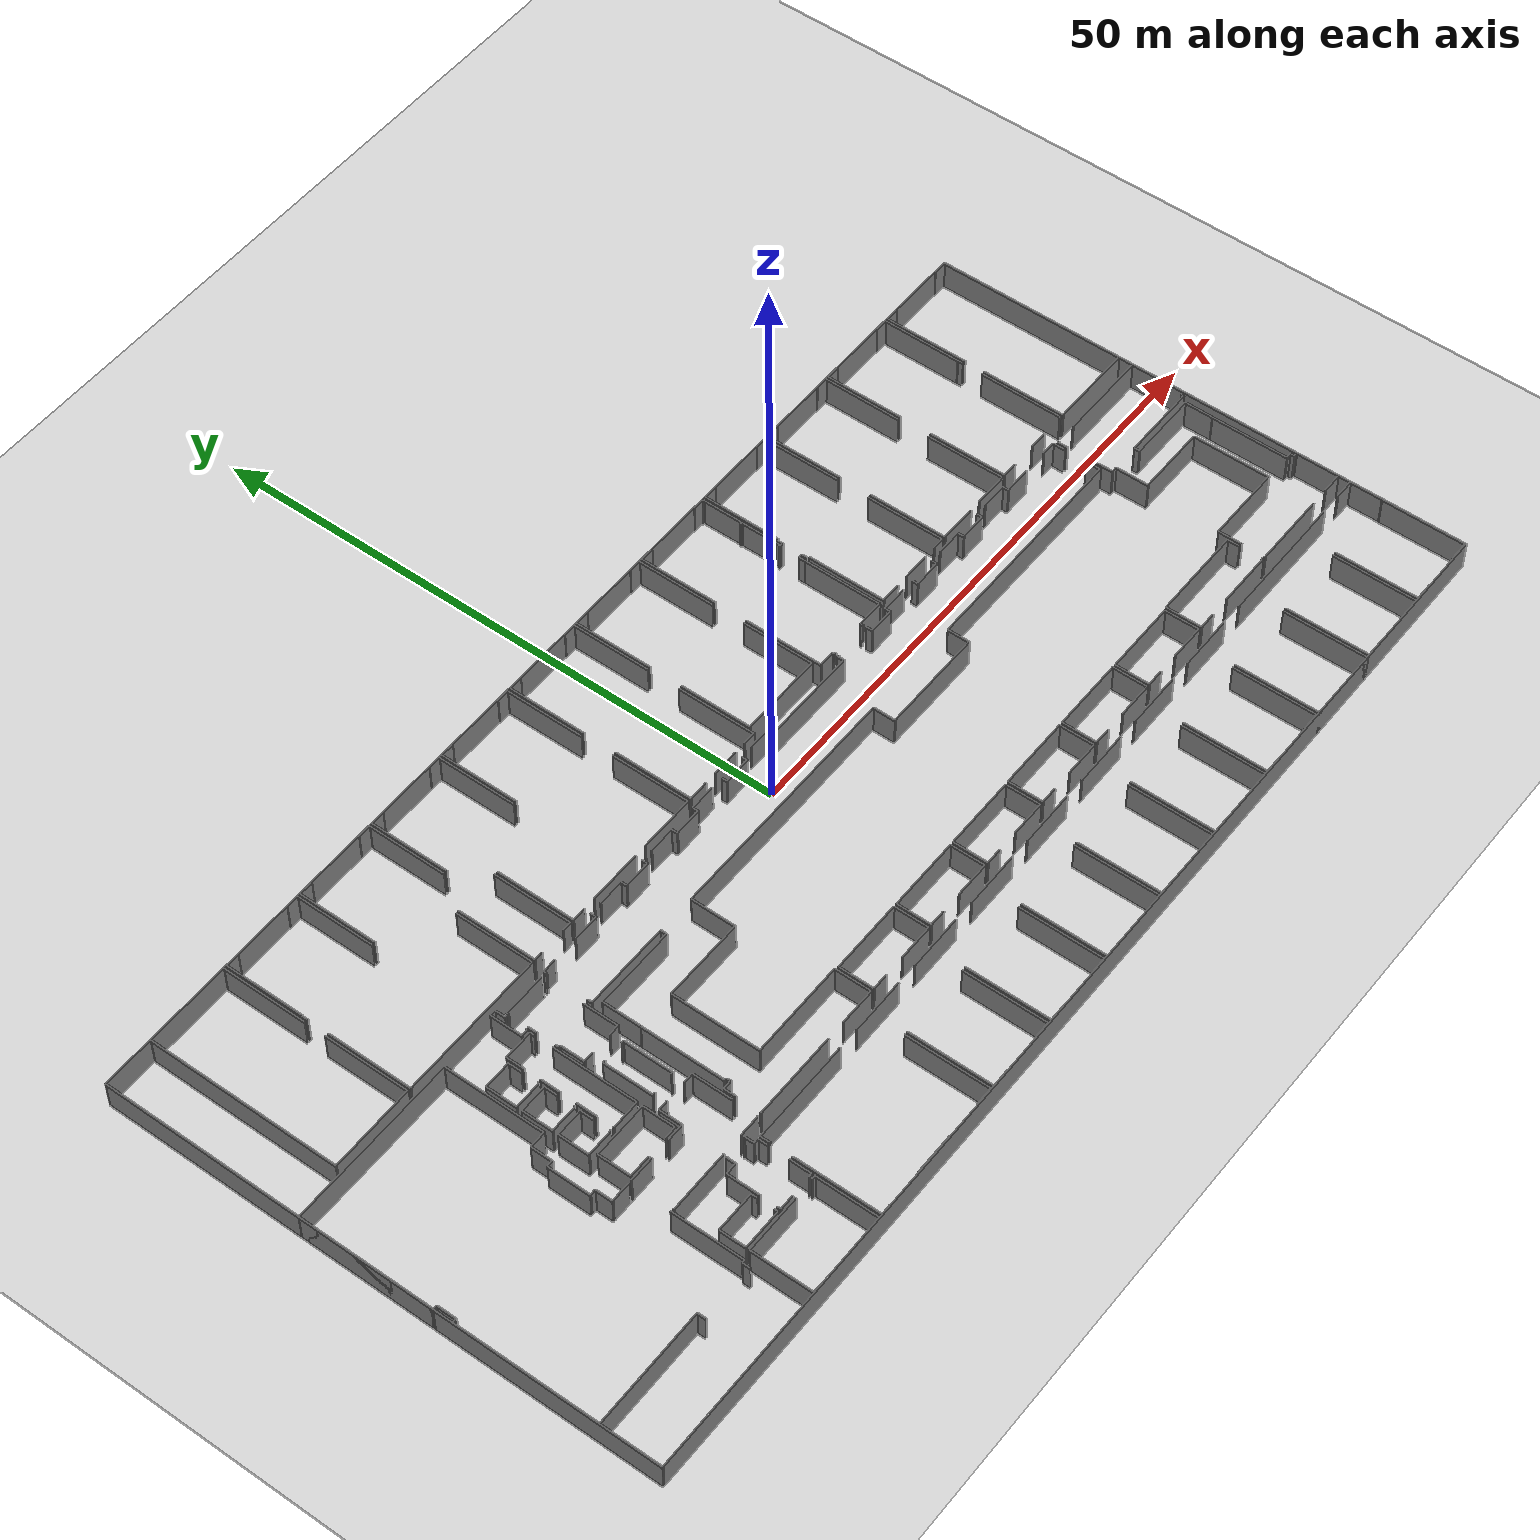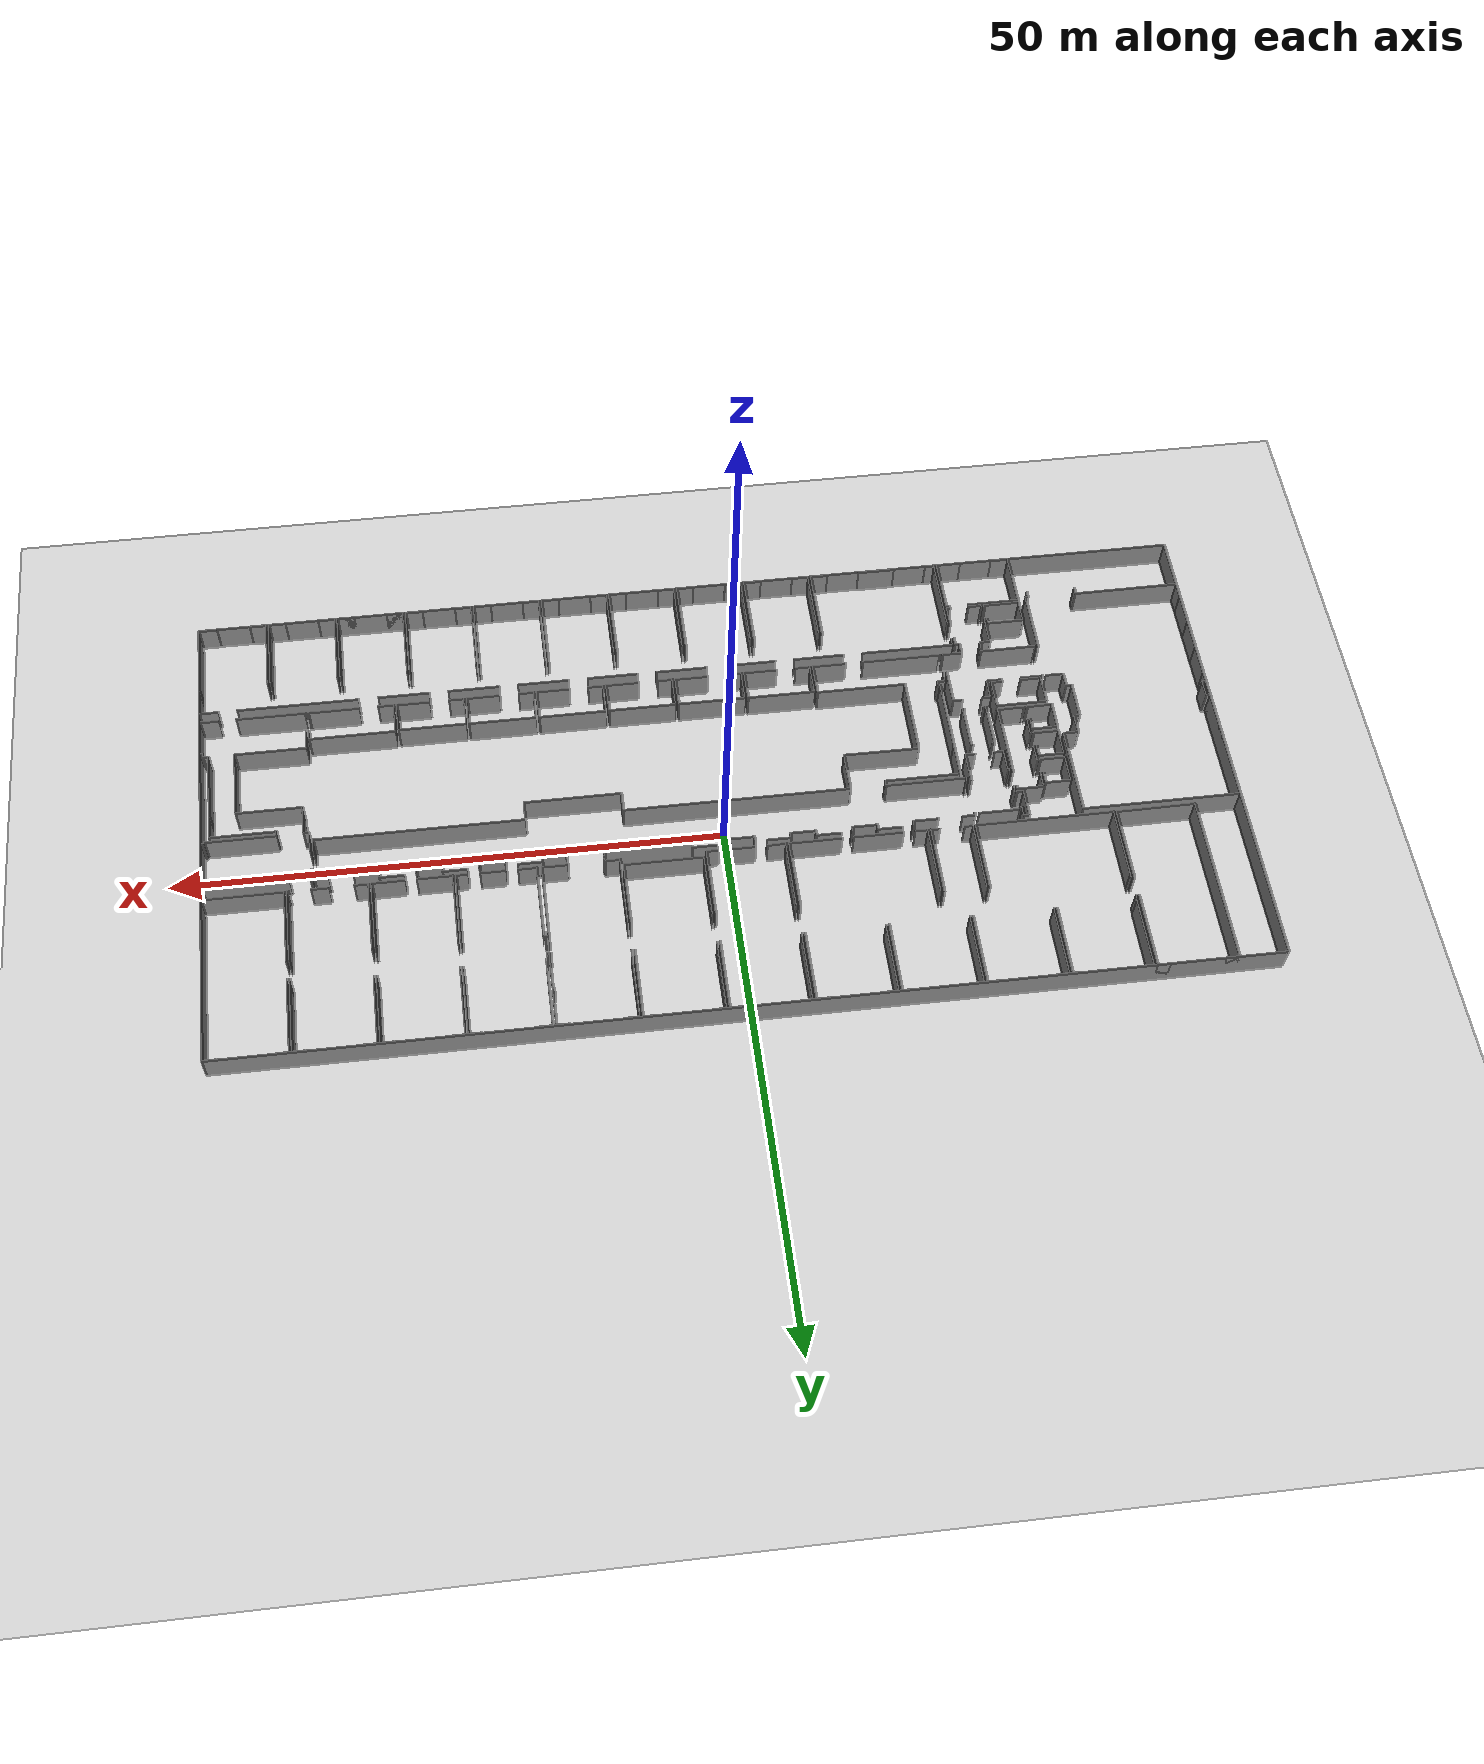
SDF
<sdf version="1.6">
  <world name="default">
    <light name="sun" type="directional">
      <cast_shadows>1</cast_shadows>
      <pose frame="">0 0 10 0 -0 0</pose>
      <diffuse>0.8 0.8 0.8 1</diffuse>
      <specular>0.1 0.1 0.1 1</specular>
      <attenuation>
        <range>1000</range>
        <constant>0.9</constant>
        <linear>0.01</linear>
        <quadratic>0.001</quadratic>
      </attenuation>
      <direction>-0.5 0.5 -1</direction>
    </light>
    <model name="ground_plane">
      <static>1</static>
      <link name="link">
        <collision name="collision">
          <geometry>
            <plane>
              <normal>0 0 1</normal>
              <size>100 100</size>
            </plane>
          </geometry>
          <surface>
            <friction>
              <ode>
                <mu>100</mu>
                <mu2>50</mu2>
              </ode>
              <torsional>
                <ode />
              </torsional>
            </friction>
            <contact>
              <ode />
            </contact>
            <bounce />
          </surface>
          <max_contacts>10</max_contacts>
        </collision>
        <visual name="visual">
          <cast_shadows>0</cast_shadows>
          <geometry>
            <plane>
              <normal>0 0 1</normal>
              <size>100 100</size>
            </plane>
          </geometry>
          <material>
            <script>
              <uri>file://media/materials/scripts/gazebo.material</uri>
              <name>Gazebo/Grey</name>
            </script>
          </material>
        </visual>
        <self_collide>0</self_collide>
        <kinematic>0</kinematic>
        <gravity>1</gravity>
      </link>
    </model>
    <gravity>0 0 -9.8</gravity>
    <magnetic_field>6e-06 2.3e-05 -4.2e-05</magnetic_field>
    <atmosphere type="adiabatic" />
    <physics default="0" name="default_physics" type="ode">
      <max_step_size>0.001</max_step_size>
      <real_time_factor>1</real_time_factor>
      <real_time_update_rate>1000</real_time_update_rate>
    </physics>
    <scene>
      <ambient>0.4 0.4 0.4 1</ambient>
      <background>0.7 0.7 0.7 1</background>
      <shadows>1</shadows>
    </scene>
    <spherical_coordinates>
      <surface_model>EARTH_WGS84</surface_model>
      <latitude_deg>0</latitude_deg>
      <longitude_deg>0</longitude_deg>
      <elevation>0</elevation>
      <heading_deg>0</heading_deg>
    </spherical_coordinates>
  <model name="50045232">
		<static>1</static>
		<link name="Wall_0">
			<collision name="Wall_0_Collision">
				<geometry>
					<box>
						<size>16.1783140181 0.1 2.5</size>
					</box>
				</geometry>
				<pose frame="">8.08915700905 0 1.25 0 0 0</pose>
			</collision>
			<visual name="Wall_0_Visual">
				<pose frame="">8.08915700905 0 1.25 0 0 0</pose>
				<geometry>
					<box>
						<size>16.1783140181 0.1 2.5</size>
					</box>
				</geometry>
				<material>
					<script>
						<uri>file://media/materials/scripts/gazebo.material</uri>
						<name>Gazebo/Grey</name>
					</script>
					<ambient>1 1 1 1</ambient>
				</material>
			</visual>
			<pose frame="">4.34278456898 -16.1783140181 0 0 0 1.57079632679</pose>
		</link>
		<link name="Wall_1">
			<collision name="Wall_1_Collision">
				<geometry>
					<box>
						<size>1.17428163201 0.1 2.5</size>
					</box>
				</geometry>
				<pose frame="">0.587140816003 0 1.25 0 0 0</pose>
			</collision>
			<visual name="Wall_1_Visual">
				<pose frame="">0.587140816003 0 1.25 0 0 0</pose>
				<geometry>
					<box>
						<size>1.17428163201 0.1 2.5</size>
					</box>
				</geometry>
				<material>
					<script>
						<uri>file://media/materials/scripts/gazebo.material</uri>
						<name>Gazebo/Grey</name>
					</script>
					<ambient>1 1 1 1</ambient>
				</material>
			</visual>
			<pose frame="">4.34278456898 -0.0 0 0 0 0.0</pose>
		</link>
		<link name="Wall_2">
			<collision name="Wall_2_Collision">
				<geometry>
					<box>
						<size>1.14278456898 0.1 2.5</size>
					</box>
				</geometry>
				<pose frame="">0.57139228449 0 1.25 0 0 0</pose>
			</collision>
			<visual name="Wall_2_Visual">
				<pose frame="">0.57139228449 0 1.25 0 0 0</pose>
				<geometry>
					<box>
						<size>1.14278456898 0.1 2.5</size>
					</box>
				</geometry>
				<material>
					<script>
						<uri>file://media/materials/scripts/gazebo.material</uri>
						<name>Gazebo/Grey</name>
					</script>
					<ambient>1 1 1 1</ambient>
				</material>
			</visual>
			<pose frame="">10.4339101445 -0.0 0 0 0 0.0</pose>
		</link>
		<link name="Wall_3">
			<collision name="Wall_3_Collision">
				<geometry>
					<box>
						<size>7.18615653278 0.1 2.5</size>
					</box>
				</geometry>
				<pose frame="">3.59307826639 0 1.25 0 0 0</pose>
			</collision>
			<visual name="Wall_3_Visual">
				<pose frame="">3.59307826639 0 1.25 0 0 0</pose>
				<geometry>
					<box>
						<size>7.18615653278 0.1 2.5</size>
					</box>
				</geometry>
				<material>
					<script>
						<uri>file://media/materials/scripts/gazebo.material</uri>
						<name>Gazebo/Grey</name>
					</script>
					<ambient>1 1 1 1</ambient>
				</material>
			</visual>
			<pose frame="">11.5766947134 -0.0 0 0 0 -1.57079632679</pose>
		</link>
		<link name="Wall_4">
			<collision name="Wall_4_Collision">
				<geometry>
					<box>
						<size>7.16723289411 0.1 2.5</size>
					</box>
				</geometry>
				<pose frame="">3.58361644706 0 1.25 0 0 0</pose>
			</collision>
			<visual name="Wall_4_Visual">
				<pose frame="">3.58361644706 0 1.25 0 0 0</pose>
				<geometry>
					<box>
						<size>7.16723289411 0.1 2.5</size>
					</box>
				</geometry>
				<material>
					<script>
						<uri>file://media/materials/scripts/gazebo.material</uri>
						<name>Gazebo/Grey</name>
					</script>
					<ambient>1 1 1 1</ambient>
				</material>
			</visual>
			<pose frame="">11.5766947134 -8.95265915225 0 0 0 -1.57079632679</pose>
		</link>
		<link name="Wall_5">
			<collision name="Wall_5_Collision">
				<geometry>
					<box>
						<size>7.23414605223 0.1 2.5</size>
					</box>
				</geometry>
				<pose frame="">3.61707302612 0 1.25 0 0 0</pose>
			</collision>
			<visual name="Wall_5_Visual">
				<pose frame="">3.61707302612 0 1.25 0 0 0</pose>
				<geometry>
					<box>
						<size>7.23414605223 0.1 2.5</size>
					</box>
				</geometry>
				<material>
					<script>
						<uri>file://media/materials/scripts/gazebo.material</uri>
						<name>Gazebo/Grey</name>
					</script>
					<ambient>1 1 1 1</ambient>
				</material>
			</visual>
			<pose frame="">11.5766947134 -16.1198920464 0 0 0 -3.1335167029</pose>
		</link>
		<link name="Wall_6">
			<collision name="Wall_6_Collision">
				<geometry>
					<box>
						<size>6.65883473567 0.1 2.5</size>
					</box>
				</geometry>
				<pose frame="">3.32941736784 0 1.25 0 0 0</pose>
			</collision>
			<visual name="Wall_6_Visual">
				<pose frame="">3.32941736784 0 1.25 0 0 0</pose>
				<geometry>
					<box>
						<size>6.65883473567 0.1 2.5</size>
					</box>
				</geometry>
				<material>
					<script>
						<uri>file://media/materials/scripts/gazebo.material</uri>
						<name>Gazebo/Grey</name>
					</script>
					<ambient>1 1 1 1</ambient>
				</material>
			</visual>
			<pose frame="">11.8539450706 -6.68156850294 0 0 0 1.57079632679</pose>
		</link>
		<link name="Wall_7">
			<collision name="Wall_7_Collision">
				<geometry>
					<box>
						<size>1.09655500873 0.1 2.5</size>
					</box>
				</geometry>
				<pose frame="">0.548277504366 0 1.25 0 0 0</pose>
			</collision>
			<visual name="Wall_7_Visual">
				<pose frame="">0.548277504366 0 1.25 0 0 0</pose>
				<geometry>
					<box>
						<size>1.09655500873 0.1 2.5</size>
					</box>
				</geometry>
				<material>
					<script>
						<uri>file://media/materials/scripts/gazebo.material</uri>
						<name>Gazebo/Grey</name>
					</script>
					<ambient>1 1 1 1</ambient>
				</material>
			</visual>
			<pose frame="">11.8539450706 -0.0227337672646 0 0 0 0.0</pose>
		</link>
		<link name="Wall_8">
			<collision name="Wall_8_Collision">
				<geometry>
					<box>
						<size>1.11827274171 0.1 2.5</size>
					</box>
				</geometry>
				<pose frame="">0.559136370853 0 1.25 0 0 0</pose>
			</collision>
			<visual name="Wall_8_Visual">
				<pose frame="">0.559136370853 0 1.25 0 0 0</pose>
				<geometry>
					<box>
						<size>1.11827274171 0.1 2.5</size>
					</box>
				</geometry>
				<material>
					<script>
						<uri>file://media/materials/scripts/gazebo.material</uri>
						<name>Gazebo/Grey</name>
					</script>
					<ambient>1 1 1 1</ambient>
				</material>
			</visual>
			<pose frame="">17.9101444674 -0.0227337672646 0 0 0 0.0</pose>
		</link>
		<link name="Wall_9">
			<collision name="Wall_9_Collision">
				<geometry>
					<box>
						<size>6.6604857914 0.1 2.5</size>
					</box>
				</geometry>
				<pose frame="">3.3302428957 0 1.25 0 0 0</pose>
			</collision>
			<visual name="Wall_9_Visual">
				<pose frame="">3.3302428957 0 1.25 0 0 0</pose>
				<geometry>
					<box>
						<size>6.6604857914 0.1 2.5</size>
					</box>
				</geometry>
				<material>
					<script>
						<uri>file://media/materials/scripts/gazebo.material</uri>
						<name>Gazebo/Grey</name>
					</script>
					<ambient>1 1 1 1</ambient>
				</material>
			</visual>
			<pose frame="">19.0284172091 -0.0227337672646 0 0 0 -1.57079632679</pose>
		</link>
		<link name="Wall_10">
			<collision name="Wall_10_Collision">
				<geometry>
					<box>
						<size>6.67090014288 0.1 2.5</size>
					</box>
				</geometry>
				<pose frame="">3.33545007144 0 1.25 0 0 0</pose>
			</collision>
			<visual name="Wall_10_Visual">
				<pose frame="">3.33545007144 0 1.25 0 0 0</pose>
				<geometry>
					<box>
						<size>6.67090014288 0.1 2.5</size>
					</box>
				</geometry>
				<material>
					<script>
						<uri>file://media/materials/scripts/gazebo.material</uri>
						<name>Gazebo/Grey</name>
					</script>
					<ambient>1 1 1 1</ambient>
				</material>
			</visual>
			<pose frame="">19.2730274647 -6.69973011589 0 0 0 1.57079632679</pose>
		</link>
		<link name="Wall_11">
			<collision name="Wall_11_Collision">
				<geometry>
					<box>
						<size>1.14837275758 0.1 2.5</size>
					</box>
				</geometry>
				<pose frame="">0.57418637879 0 1.25 0 0 0</pose>
			</collision>
			<visual name="Wall_11_Visual">
				<pose frame="">0.57418637879 0 1.25 0 0 0</pose>
				<geometry>
					<box>
						<size>1.14837275758 0.1 2.5</size>
					</box>
				</geometry>
				<material>
					<script>
						<uri>file://media/materials/scripts/gazebo.material</uri>
						<name>Gazebo/Grey</name>
					</script>
					<ambient>1 1 1 1</ambient>
				</material>
			</visual>
			<pose frame="">19.2730274647 -0.0288299730116 0 0 0 0.0</pose>
		</link>
		<link name="Wall_12">
			<collision name="Wall_12_Collision">
				<geometry>
					<box>
						<size>1.15243689475 0.1 2.5</size>
					</box>
				</geometry>
				<pose frame="">0.576218447373 0 1.25 0 0 0</pose>
			</collision>
			<visual name="Wall_12_Visual">
				<pose frame="">0.576218447373 0 1.25 0 0 0</pose>
				<geometry>
					<box>
						<size>1.15243689475 0.1 2.5</size>
					</box>
				</geometry>
				<material>
					<script>
						<uri>file://media/materials/scripts/gazebo.material</uri>
						<name>Gazebo/Grey</name>
					</script>
					<ambient>1 1 1 1</ambient>
				</material>
			</visual>
			<pose frame="">25.3287188443 -0.0288299730116 0 0 0 0.0</pose>
		</link>
		<link name="Wall_13">
			<collision name="Wall_13_Collision">
				<geometry>
					<box>
						<size>6.6709001731 0.1 2.5</size>
					</box>
				</geometry>
				<pose frame="">3.33545008655 0 1.25 0 0 0</pose>
			</collision>
			<visual name="Wall_13_Visual">
				<pose frame="">3.33545008655 0 1.25 0 0 0</pose>
				<geometry>
					<box>
						<size>6.6709001731 0.1 2.5</size>
					</box>
				</geometry>
				<material>
					<script>
						<uri>file://media/materials/scripts/gazebo.material</uri>
						<name>Gazebo/Grey</name>
					</script>
					<ambient>1 1 1 1</ambient>
				</material>
			</visual>
			<pose frame="">26.481155739 -0.0288299730116 0 0 0 -1.57070113403</pose>
		</link>
		<link name="Wall_14">
			<collision name="Wall_14_Collision">
				<geometry>
					<box>
						<size>6.68144149865 0.1 2.5</size>
					</box>
				</geometry>
				<pose frame="">3.34072074933 0 1.25 0 0 0</pose>
			</collision>
			<visual name="Wall_14_Visual">
				<pose frame="">3.34072074933 0 1.25 0 0 0</pose>
				<geometry>
					<box>
						<size>6.68144149865 0.1 2.5</size>
					</box>
				</geometry>
				<material>
					<script>
						<uri>file://media/materials/scripts/gazebo.material</uri>
						<name>Gazebo/Grey</name>
					</script>
					<ambient>1 1 1 1</ambient>
				</material>
			</visual>
			<pose frame="">26.7379584061 -6.71027147166 0 0 0 1.57079632679</pose>
		</link>
		<link name="Wall_15">
			<collision name="Wall_15_Collision">
				<geometry>
					<box>
						<size>1.1164946817 0.1 2.5</size>
					</box>
				</geometry>
				<pose frame="">0.558247340848 0 1.25 0 0 0</pose>
			</collision>
			<visual name="Wall_15_Visual">
				<pose frame="">0.558247340848 0 1.25 0 0 0</pose>
				<geometry>
					<box>
						<size>1.1164946817 0.1 2.5</size>
					</box>
				</geometry>
				<material>
					<script>
						<uri>file://media/materials/scripts/gazebo.material</uri>
						<name>Gazebo/Grey</name>
					</script>
					<ambient>1 1 1 1</ambient>
				</material>
			</visual>
			<pose frame="">26.7379584061 -0.0288299730116 0 0 0 0.0</pose>
		</link>
		<link name="Wall_16">
			<collision name="Wall_16_Collision">
				<geometry>
					<box>
						<size>1.12360692173 0.1 2.5</size>
					</box>
				</geometry>
				<pose frame="">0.561803460867 0 1.25 0 0 0</pose>
			</collision>
			<visual name="Wall_16_Visual">
				<pose frame="">0.561803460867 0 1.25 0 0 0</pose>
				<geometry>
					<box>
						<size>1.12360692173 0.1 2.5</size>
					</box>
				</geometry>
				<material>
					<script>
						<uri>file://media/materials/scripts/gazebo.material</uri>
						<name>Gazebo/Grey</name>
					</script>
					<ambient>1 1 1 1</ambient>
				</material>
			</visual>
			<pose frame="">32.780949357 -0.0288299730116 0 0 0 0.0</pose>
		</link>
		<link name="Wall_17">
			<collision name="Wall_17_Collision">
				<geometry>
					<box>
						<size>6.68145830603 0.1 2.5</size>
					</box>
				</geometry>
				<pose frame="">3.34072915302 0 1.25 0 0 0</pose>
			</collision>
			<visual name="Wall_17_Visual">
				<pose frame="">3.34072915302 0 1.25 0 0 0</pose>
				<geometry>
					<box>
						<size>6.68145830603 0.1 2.5</size>
					</box>
				</geometry>
				<material>
					<script>
						<uri>file://media/materials/scripts/gazebo.material</uri>
						<name>Gazebo/Grey</name>
					</script>
					<ambient>1 1 1 1</ambient>
				</material>
			</visual>
			<pose frame="">33.9045562788 -0.0288299730116 0 0 0 -1.56855332569</pose>
		</link>
		<link name="Wall_18">
			<collision name="Wall_18_Collision">
				<geometry>
					<box>
						<size>6.68093348151 0.1 2.5</size>
					</box>
				</geometry>
				<pose frame="">3.34046674075 0 1.25 0 0 0</pose>
			</collision>
			<visual name="Wall_18_Visual">
				<pose frame="">3.34046674075 0 1.25 0 0 0</pose>
				<geometry>
					<box>
						<size>6.68093348151 0.1 2.5</size>
					</box>
				</geometry>
				<material>
					<script>
						<uri>file://media/materials/scripts/gazebo.material</uri>
						<name>Gazebo/Grey</name>
					</script>
					<ambient>1 1 1 1</ambient>
				</material>
			</visual>
			<pose frame="">34.1685981902 -6.71027147166 0 0 0 1.57079632679</pose>
		</link>
		<link name="Wall_19">
			<collision name="Wall_19_Collision">
				<geometry>
					<box>
						<size>1.11789172885 0.1 2.5</size>
					</box>
				</geometry>
				<pose frame="">0.558945864423 0 1.25 0 0 0</pose>
			</collision>
			<visual name="Wall_19_Visual">
				<pose frame="">0.558945864423 0 1.25 0 0 0</pose>
				<geometry>
					<box>
						<size>1.11789172885 0.1 2.5</size>
					</box>
				</geometry>
				<material>
					<script>
						<uri>file://media/materials/scripts/gazebo.material</uri>
						<name>Gazebo/Grey</name>
					</script>
					<ambient>1 1 1 1</ambient>
				</material>
			</visual>
			<pose frame="">34.1685981902 -0.0293379901572 0 0 0 0.0</pose>
		</link>
		<link name="Wall_20">
			<collision name="Wall_20_Collision">
				<geometry>
					<box>
						<size>1.11763772027 0.1 2.5</size>
					</box>
				</geometry>
				<pose frame="">0.558818860137 0 1.25 0 0 0</pose>
			</collision>
			<visual name="Wall_20_Visual">
				<pose frame="">0.558818860137 0 1.25 0 0 0</pose>
				<geometry>
					<box>
						<size>1.11763772027 0.1 2.5</size>
					</box>
				</geometry>
				<material>
					<script>
						<uri>file://media/materials/scripts/gazebo.material</uri>
						<name>Gazebo/Grey</name>
					</script>
					<ambient>1 1 1 1</ambient>
				</material>
			</visual>
			<pose frame="">40.2114621368 -0.0293379901572 0 0 0 0.0</pose>
		</link>
		<link name="Wall_21">
			<collision name="Wall_21_Collision">
				<geometry>
					<box>
						<size>6.68094862427 0.1 2.5</size>
					</box>
				</geometry>
				<pose frame="">3.34047431213 0 1.25 0 0 0</pose>
			</collision>
			<visual name="Wall_21_Visual">
				<pose frame="">3.34047431213 0 1.25 0 0 0</pose>
				<geometry>
					<box>
						<size>6.68094862427 0.1 2.5</size>
					</box>
				</geometry>
				<material>
					<script>
						<uri>file://media/materials/scripts/gazebo.material</uri>
						<name>Gazebo/Grey</name>
					</script>
					<ambient>1 1 1 1</ambient>
				</material>
			</visual>
			<pose frame="">41.3290998571 -0.0293379901572 0 0 0 -1.56866721436</pose>
		</link>
		<link name="Wall_22">
			<collision name="Wall_22_Collision">
				<geometry>
					<box>
						<size>6.67039212573 0.1 2.5</size>
					</box>
				</geometry>
				<pose frame="">3.33519606287 0 1.25 0 0 0</pose>
			</collision>
			<visual name="Wall_22_Visual">
				<pose frame="">3.33519606287 0 1.25 0 0 0</pose>
				<geometry>
					<box>
						<size>6.67039212573 0.1 2.5</size>
					</box>
				</geometry>
				<material>
					<script>
						<uri>file://media/materials/scripts/gazebo.material</uri>
						<name>Gazebo/Grey</name>
					</script>
					<ambient>1 1 1 1</ambient>
				</material>
			</visual>
			<pose frame="">41.6160025401 -6.69973011589 0 0 0 1.57079632679</pose>
		</link>
		<link name="Wall_23">
			<collision name="Wall_23_Collision">
				<geometry>
					<box>
						<size>1.11395459597 0.1 2.5</size>
					</box>
				</geometry>
				<pose frame="">0.556977297984 0 1.25 0 0 0</pose>
			</collision>
			<visual name="Wall_23_Visual">
				<pose frame="">0.556977297984 0 1.25 0 0 0</pose>
				<geometry>
					<box>
						<size>1.11395459597 0.1 2.5</size>
					</box>
				</geometry>
				<material>
					<script>
						<uri>file://media/materials/scripts/gazebo.material</uri>
						<name>Gazebo/Grey</name>
					</script>
					<ambient>1 1 1 1</ambient>
				</material>
			</visual>
			<pose frame="">41.6160025401 -0.0293379901572 0 0 0 0.0</pose>
		</link>
		<link name="Wall_24">
			<collision name="Wall_24_Collision">
				<geometry>
					<box>
						<size>1.14405461184 0.1 2.5</size>
					</box>
				</geometry>
				<pose frame="">0.572027305922 0 1.25 0 0 0</pose>
			</collision>
			<visual name="Wall_24_Visual">
				<pose frame="">0.572027305922 0 1.25 0 0 0</pose>
				<geometry>
					<box>
						<size>1.14405461184 0.1 2.5</size>
					</box>
				</geometry>
				<material>
					<script>
						<uri>file://media/materials/scripts/gazebo.material</uri>
						<name>Gazebo/Grey</name>
					</script>
					<ambient>1 1 1 1</ambient>
				</material>
			</visual>
			<pose frame="">47.6481981267 -0.0293379901572 0 0 0 0.0</pose>
		</link>
		<link name="Wall_25">
			<collision name="Wall_25_Collision">
				<geometry>
					<box>
						<size>6.67039216926 0.1 2.5</size>
					</box>
				</geometry>
				<pose frame="">3.33519608463 0 1.25 0 0 0</pose>
			</collision>
			<visual name="Wall_25_Visual">
				<pose frame="">3.33519608463 0 1.25 0 0 0</pose>
				<geometry>
					<box>
						<size>6.67039216926 0.1 2.5</size>
					</box>
				</geometry>
				<material>
					<script>
						<uri>file://media/materials/scripts/gazebo.material</uri>
						<name>Gazebo/Grey</name>
					</script>
					<ambient>1 1 1 1</ambient>
				</material>
			</visual>
			<pose frame="">48.7922527385 -0.0293379901572 0 0 0 -1.57068208678</pose>
		</link>
		<link name="Wall_26">
			<collision name="Wall_26_Collision">
				<geometry>
					<box>
						<size>6.6819495158 0.1 2.5</size>
					</box>
				</geometry>
				<pose frame="">3.3409747579 0 1.25 0 0 0</pose>
			</collision>
			<visual name="Wall_26_Visual">
				<pose frame="">3.3409747579 0 1.25 0 0 0</pose>
				<geometry>
					<box>
						<size>6.6819495158 0.1 2.5</size>
					</box>
				</geometry>
				<material>
					<script>
						<uri>file://media/materials/scripts/gazebo.material</uri>
						<name>Gazebo/Grey</name>
					</script>
					<ambient>1 1 1 1</ambient>
				</material>
			</visual>
			<pose frame="">49.0359739641 -6.71077948881 0 0 0 1.57079632679</pose>
		</link>
		<link name="Wall_27">
			<collision name="Wall_27_Collision">
				<geometry>
					<box>
						<size>1.15586601048 0.1 2.5</size>
					</box>
				</geometry>
				<pose frame="">0.577933005239 0 1.25 0 0 0</pose>
			</collision>
			<visual name="Wall_27_Visual">
				<pose frame="">0.577933005239 0 1.25 0 0 0</pose>
				<geometry>
					<box>
						<size>1.15586601048 0.1 2.5</size>
					</box>
				</geometry>
				<material>
					<script>
						<uri>file://media/materials/scripts/gazebo.material</uri>
						<name>Gazebo/Grey</name>
					</script>
					<ambient>1 1 1 1</ambient>
				</material>
			</visual>
			<pose frame="">49.0359739641 -0.0288299730116 0 0 0 0.0</pose>
		</link>
		<link name="Wall_28">
			<collision name="Wall_28_Collision">
				<geometry>
					<box>
						<size>1.15243689475 0.1 2.5</size>
					</box>
				</geometry>
				<pose frame="">0.576218447373 0 1.25 0 0 0</pose>
			</collision>
			<visual name="Wall_28_Visual">
				<pose frame="">0.576218447373 0 1.25 0 0 0</pose>
				<geometry>
					<box>
						<size>1.15243689475 0.1 2.5</size>
					</box>
				</geometry>
				<material>
					<script>
						<uri>file://media/materials/scripts/gazebo.material</uri>
						<name>Gazebo/Grey</name>
					</script>
					<ambient>1 1 1 1</ambient>
				</material>
			</visual>
			<pose frame="">55.0895062708 -0.0288299730116 0 0 0 0.0</pose>
		</link>
		<link name="Wall_29">
			<collision name="Wall_29_Collision">
				<geometry>
					<box>
						<size>6.68195164493 0.1 2.5</size>
					</box>
				</geometry>
				<pose frame="">3.34097582246 0 1.25 0 0 0</pose>
			</collision>
			<visual name="Wall_29_Visual">
				<pose frame="">3.34097582246 0 1.25 0 0 0</pose>
				<geometry>
					<box>
						<size>6.68195164493 0.1 2.5</size>
					</box>
				</geometry>
				<material>
					<script>
						<uri>file://media/materials/scripts/gazebo.material</uri>
						<name>Gazebo/Grey</name>
					</script>
					<ambient>1 1 1 1</ambient>
				</material>
			</visual>
			<pose frame="">56.2419431656 -0.0288299730116 0 0 0 -1.57159462359</pose>
		</link>
		<link name="Wall_30">
			<collision name="Wall_30_Collision">
				<geometry>
					<box>
						<size>0.428258453723 0.1 2.5</size>
					</box>
				</geometry>
				<pose frame="">0.214129226861 0 1.25 0 0 0</pose>
			</collision>
			<visual name="Wall_30_Visual">
				<pose frame="">0.214129226861 0 1.25 0 0 0</pose>
				<geometry>
					<box>
						<size>0.428258453723 0.1 2.5</size>
					</box>
				</geometry>
				<material>
					<script>
						<uri>file://media/materials/scripts/gazebo.material</uri>
						<name>Gazebo/Grey</name>
					</script>
					<ambient>1 1 1 1</ambient>
				</material>
			</visual>
			<pose frame="">11.8215589776 -9.40657247182 0 0 0 1.57079632679</pose>
		</link>
		<link name="Wall_31">
			<collision name="Wall_31_Collision">
				<geometry>
					<box>
						<size>0.451373233847 0.1 2.5</size>
					</box>
				</geometry>
				<pose frame="">0.225686616923 0 1.25 0 0 0</pose>
			</collision>
			<visual name="Wall_31_Visual">
				<pose frame="">0.225686616923 0 1.25 0 0 0</pose>
				<geometry>
					<box>
						<size>0.451373233847 0.1 2.5</size>
					</box>
				</geometry>
				<material>
					<script>
						<uri>file://media/materials/scripts/gazebo.material</uri>
						<name>Gazebo/Grey</name>
					</script>
					<ambient>1 1 1 1</ambient>
				</material>
			</visual>
			<pose frame="">11.8215589776 -7.21206540721 0 0 0 1.57079632679</pose>
		</link>
		<link name="Wall_32">
			<collision name="Wall_32_Collision">
				<geometry>
					<box>
						<size>0.328814097476 0.1 2.5</size>
					</box>
				</geometry>
				<pose frame="">0.164407048738 0 1.25 0 0 0</pose>
			</collision>
			<visual name="Wall_32_Visual">
				<pose frame="">0.164407048738 0 1.25 0 0 0</pose>
				<geometry>
					<box>
						<size>0.328814097476 0.1 2.5</size>
					</box>
				</geometry>
				<material>
					<script>
						<uri>file://media/materials/scripts/gazebo.material</uri>
						<name>Gazebo/Grey</name>
					</script>
					<ambient>1 1 1 1</ambient>
				</material>
			</visual>
			<pose frame="">63.6047626607 -6.76069217336 0 0 0 -1.57079632679</pose>
		</link>
		<link name="Wall_33">
			<collision name="Wall_33_Collision">
				<geometry>
					<box>
						<size>0.0933481505001 0.1 2.5</size>
					</box>
				</geometry>
				<pose frame="">0.04667407525 0 1.25 0 0 0</pose>
			</collision>
			<visual name="Wall_33_Visual">
				<pose frame="">0.04667407525 0 1.25 0 0 0</pose>
				<geometry>
					<box>
						<size>0.0933481505001 0.1 2.5</size>
					</box>
				</geometry>
				<material>
					<script>
						<uri>file://media/materials/scripts/gazebo.material</uri>
						<name>Gazebo/Grey</name>
					</script>
					<ambient>1 1 1 1</ambient>
				</material>
			</visual>
			<pose frame="">63.6047626607 -7.08950627084 0 0 0 3.14159265359</pose>
		</link>
		<link name="Wall_34">
			<collision name="Wall_34_Collision">
				<geometry>
					<box>
						<size>0.126242260676 0.1 2.5</size>
					</box>
				</geometry>
				<pose frame="">0.0631211303381 0 1.25 0 0 0</pose>
			</collision>
			<visual name="Wall_34_Visual">
				<pose frame="">0.0631211303381 0 1.25 0 0 0</pose>
				<geometry>
					<box>
						<size>0.126242260676 0.1 2.5</size>
					</box>
				</geometry>
				<material>
					<script>
						<uri>file://media/materials/scripts/gazebo.material</uri>
						<name>Gazebo/Grey</name>
					</script>
					<ambient>1 1 1 1</ambient>
				</material>
			</visual>
			<pose frame="">63.5114145102 -7.08950627084 0 0 0 -1.57079632679</pose>
		</link>
		<link name="Wall_35">
			<collision name="Wall_35_Collision">
				<geometry>
					<box>
						<size>0.285505635815 0.1 2.5</size>
					</box>
				</geometry>
				<pose frame="">0.142752817908 0 1.25 0 0 0</pose>
			</collision>
			<visual name="Wall_35_Visual">
				<pose frame="">0.142752817908 0 1.25 0 0 0</pose>
				<geometry>
					<box>
						<size>0.285505635815 0.1 2.5</size>
					</box>
				</geometry>
				<material>
					<script>
						<uri>file://media/materials/scripts/gazebo.material</uri>
						<name>Gazebo/Grey</name>
					</script>
					<ambient>1 1 1 1</ambient>
				</material>
			</visual>
			<pose frame="">63.5114145102 -7.21574853151 0 0 0 0.0</pose>
		</link>
		<link name="Wall_36">
			<collision name="Wall_36_Collision">
				<geometry>
					<box>
						<size>0.450230195269 0.1 2.5</size>
					</box>
				</geometry>
				<pose frame="">0.225115097635 0 1.25 0 0 0</pose>
			</collision>
			<visual name="Wall_36_Visual">
				<pose frame="">0.225115097635 0 1.25 0 0 0</pose>
				<geometry>
					<box>
						<size>0.450230195269 0.1 2.5</size>
					</box>
				</geometry>
				<material>
					<script>
						<uri>file://media/materials/scripts/gazebo.material</uri>
						<name>Gazebo/Grey</name>
					</script>
					<ambient>1 1 1 1</ambient>
				</material>
			</visual>
			<pose frame="">63.7969201461 -7.21574853151 0 0 0 1.57079632679</pose>
		</link>
		<link name="Wall_37">
			<collision name="Wall_37_Collision">
				<geometry>
					<box>
						<size>0.424321320845 0.1 2.5</size>
					</box>
				</geometry>
				<pose frame="">0.212160660422 0 1.25 0 0 0</pose>
			</collision>
			<visual name="Wall_37_Visual">
				<pose frame="">0.212160660422 0 1.25 0 0 0</pose>
				<geometry>
					<box>
						<size>0.424321320845 0.1 2.5</size>
					</box>
				</geometry>
				<material>
					<script>
						<uri>file://media/materials/scripts/gazebo.material</uri>
						<name>Gazebo/Grey</name>
					</script>
					<ambient>1 1 1 1</ambient>
				</material>
			</visual>
			<pose frame="">86.0085727893 -6.76551833624 0 0 0 -1.57079632679</pose>
		</link>
		<link name="Wall_38">
			<collision name="Wall_38_Collision">
				<geometry>
					<box>
						<size>7.1523733926 0.1 2.5</size>
					</box>
				</geometry>
				<pose frame="">3.5761866963 0 1.25 0 0 0</pose>
			</collision>
			<visual name="Wall_38_Visual">
				<pose frame="">3.5761866963 0 1.25 0 0 0</pose>
				<geometry>
					<box>
						<size>7.1523733926 0.1 2.5</size>
					</box>
				</geometry>
				<material>
					<script>
						<uri>file://media/materials/scripts/gazebo.material</uri>
						<name>Gazebo/Grey</name>
					</script>
					<ambient>1 1 1 1</ambient>
				</material>
			</visual>
			<pose frame="">86.0085727893 -8.96497856803 0 0 0 -1.57079632679</pose>
		</link>
		<link name="Wall_39">
			<collision name="Wall_39_Collision">
				<geometry>
					<box>
						<size>0.144276869344 0.1 2.5</size>
					</box>
				</geometry>
				<pose frame="">0.0721384346722 0 1.25 0 0 0</pose>
			</collision>
			<visual name="Wall_39_Visual">
				<pose frame="">0.0721384346722 0 1.25 0 0 0</pose>
				<geometry>
					<box>
						<size>0.144276869344 0.1 2.5</size>
					</box>
				</geometry>
				<material>
					<script>
						<uri>file://media/materials/scripts/gazebo.material</uri>
						<name>Gazebo/Grey</name>
					</script>
					<ambient>1 1 1 1</ambient>
				</material>
			</visual>
			<pose frame="">86.0085727893 -16.1173519606 0 0 0 3.14159265359</pose>
		</link>
		<link name="Wall_40">
			<collision name="Wall_40_Collision">
				<geometry>
					<box>
						<size>1.61333545007 0.1 2.5</size>
					</box>
				</geometry>
				<pose frame="">0.806667725036 0 1.25 0 0 0</pose>
			</collision>
			<visual name="Wall_40_Visual">
				<pose frame="">0.806667725036 0 1.25 0 0 0</pose>
				<geometry>
					<box>
						<size>1.61333545007 0.1 2.5</size>
					</box>
				</geometry>
				<material>
					<script>
						<uri>file://media/materials/scripts/gazebo.material</uri>
						<name>Gazebo/Grey</name>
					</script>
					<ambient>1 1 1 1</ambient>
				</material>
			</visual>
			<pose frame="">83.9283695825 -16.1173519606 0 0 0 3.14159265359</pose>
		</link>
		<link name="Wall_41">
			<collision name="Wall_41_Collision">
				<geometry>
					<box>
						<size>1.29214160978 0.1 2.5</size>
					</box>
				</geometry>
				<pose frame="">0.64607080489 0 1.25 0 0 0</pose>
			</collision>
			<visual name="Wall_41_Visual">
				<pose frame="">0.64607080489 0 1.25 0 0 0</pose>
				<geometry>
					<box>
						<size>1.29214160978 0.1 2.5</size>
					</box>
				</geometry>
				<material>
					<script>
						<uri>file://media/materials/scripts/gazebo.material</uri>
						<name>Gazebo/Grey</name>
					</script>
					<ambient>1 1 1 1</ambient>
				</material>
			</visual>
			<pose frame="">80.1244642007 -16.1173519606 0 0 0 3.14159265359</pose>
		</link>
		<link name="Wall_42">
			<collision name="Wall_42_Collision">
				<geometry>
					<box>
						<size>6.693125893 0.1 2.5</size>
					</box>
				</geometry>
				<pose frame="">3.3465629465 0 1.25 0 0 0</pose>
			</collision>
			<visual name="Wall_42_Visual">
				<pose frame="">3.3465629465 0 1.25 0 0 0</pose>
				<geometry>
					<box>
						<size>6.693125893 0.1 2.5</size>
					</box>
				</geometry>
				<material>
					<script>
						<uri>file://media/materials/scripts/gazebo.material</uri>
						<name>Gazebo/Grey</name>
					</script>
					<ambient>1 1 1 1</ambient>
				</material>
			</visual>
			<pose frame="">78.8323225909 -16.1173519606 0 0 0 1.57079632679</pose>
		</link>
		<link name="Wall_43">
			<collision name="Wall_43_Collision">
				<geometry>
					<box>
						<size>0.5040800127 0.1 2.5</size>
					</box>
				</geometry>
				<pose frame="">0.25204000635 0 1.25 0 0 0</pose>
			</collision>
			<visual name="Wall_43_Visual">
				<pose frame="">0.25204000635 0 1.25 0 0 0</pose>
				<geometry>
					<box>
						<size>0.5040800127 0.1 2.5</size>
					</box>
				</geometry>
				<material>
					<script>
						<uri>file://media/materials/scripts/gazebo.material</uri>
						<name>Gazebo/Grey</name>
					</script>
					<ambient>1 1 1 1</ambient>
				</material>
			</visual>
			<pose frame="">63.8158437847 -9.42422606763 0 0 0 1.57079632679</pose>
		</link>
		<link name="Wall_44">
			<collision name="Wall_44_Collision">
				<geometry>
					<box>
						<size>0.315097634545 0.1 2.5</size>
					</box>
				</geometry>
				<pose frame="">0.157548817273 0 1.25 0 0 0</pose>
			</collision>
			<visual name="Wall_44_Visual">
				<pose frame="">0.157548817273 0 1.25 0 0 0</pose>
				<geometry>
					<box>
						<size>0.315097634545 0.1 2.5</size>
					</box>
				</geometry>
				<material>
					<script>
						<uri>file://media/materials/scripts/gazebo.material</uri>
						<name>Gazebo/Grey</name>
					</script>
					<ambient>1 1 1 1</ambient>
				</material>
			</visual>
			<pose frame="">63.8158437847 -8.92014605493 0 0 0 3.14159265359</pose>
		</link>
		<link name="Wall_45">
			<collision name="Wall_45_Collision">
				<geometry>
					<box>
						<size>0.5012859184 0.1 2.5</size>
					</box>
				</geometry>
				<pose frame="">0.2506429592 0 1.25 0 0 0</pose>
			</collision>
			<visual name="Wall_45_Visual">
				<pose frame="">0.2506429592 0 1.25 0 0 0</pose>
				<geometry>
					<box>
						<size>0.5012859184 0.1 2.5</size>
					</box>
				</geometry>
				<material>
					<script>
						<uri>file://media/materials/scripts/gazebo.material</uri>
						<name>Gazebo/Grey</name>
					</script>
					<ambient>1 1 1 1</ambient>
				</material>
			</visual>
			<pose frame="">63.5007461502 -8.92014605493 0 0 0 -1.57079632679</pose>
		</link>
		<link name="Wall_46">
			<collision name="Wall_46_Collision">
				<geometry>
					<box>
						<size>6.68410858866 0.1 2.5</size>
					</box>
				</geometry>
				<pose frame="">3.34205429433 0 1.25 0 0 0</pose>
			</collision>
			<visual name="Wall_46_Visual">
				<pose frame="">3.34205429433 0 1.25 0 0 0</pose>
				<geometry>
					<box>
						<size>6.68410858866 0.1 2.5</size>
					</box>
				</geometry>
				<material>
					<script>
						<uri>file://media/materials/scripts/gazebo.material</uri>
						<name>Gazebo/Grey</name>
					</script>
					<ambient>1 1 1 1</ambient>
				</material>
			</visual>
			<pose frame="">28.5062390856 -9.42143197333 0 0 0 -1.57079632679</pose>
		</link>
		<link name="Wall_47">
			<collision name="Wall_47_Collision">
				<geometry>
					<box>
						<size>0.817907604382 0.1 2.5</size>
					</box>
				</geometry>
				<pose frame="">0.408953802191 0 1.25 0 0 0</pose>
			</collision>
			<visual name="Wall_47_Visual">
				<pose frame="">0.408953802191 0 1.25 0 0 0</pose>
				<geometry>
					<box>
						<size>0.817907604382 0.1 2.5</size>
					</box>
				</geometry>
				<material>
					<script>
						<uri>file://media/materials/scripts/gazebo.material</uri>
						<name>Gazebo/Grey</name>
					</script>
					<ambient>1 1 1 1</ambient>
				</material>
			</visual>
			<pose frame="">28.5062390856 -16.105540562 0 0 0 3.14159265359</pose>
		</link>
		<link name="Wall_48">
			<collision name="Wall_48_Collision">
				<geometry>
					<box>
						<size>0.777901254167 0.1 2.5</size>
					</box>
				</geometry>
				<pose frame="">0.388950627084 0 1.25 0 0 0</pose>
			</collision>
			<visual name="Wall_48_Visual">
				<pose frame="">0.388950627084 0 1.25 0 0 0</pose>
				<geometry>
					<box>
						<size>0.777901254167 0.1 2.5</size>
					</box>
				</geometry>
				<material>
					<script>
						<uri>file://media/materials/scripts/gazebo.material</uri>
						<name>Gazebo/Grey</name>
					</script>
					<ambient>1 1 1 1</ambient>
				</material>
			</visual>
			<pose frame="">25.4535640578 -16.105540562 0 0 0 3.14159265359</pose>
		</link>
		<link name="Wall_49">
			<collision name="Wall_49_Collision">
				<geometry>
					<box>
						<size>6.67509128433 0.1 2.5</size>
					</box>
				</geometry>
				<pose frame="">3.33754564217 0 1.25 0 0 0</pose>
			</collision>
			<visual name="Wall_49_Visual">
				<pose frame="">3.33754564217 0 1.25 0 0 0</pose>
				<geometry>
					<box>
						<size>6.67509128433 0.1 2.5</size>
					</box>
				</geometry>
				<material>
					<script>
						<uri>file://media/materials/scripts/gazebo.material</uri>
						<name>Gazebo/Grey</name>
					</script>
					<ambient>1 1 1 1</ambient>
				</material>
			</visual>
			<pose frame="">24.6756628036 -16.105540562 0 0 0 1.57079632679</pose>
		</link>
		<link name="Wall_50">
			<collision name="Wall_50_Collision">
				<geometry>
					<box>
						<size>3.05038895063 0.1 2.5</size>
					</box>
				</geometry>
				<pose frame="">1.52519447531 0 1.25 0 0 0</pose>
			</collision>
			<visual name="Wall_50_Visual">
				<pose frame="">1.52519447531 0 1.25 0 0 0</pose>
				<geometry>
					<box>
						<size>3.05038895063 0.1 2.5</size>
					</box>
				</geometry>
				<material>
					<script>
						<uri>file://media/materials/scripts/gazebo.material</uri>
						<name>Gazebo/Grey</name>
					</script>
					<ambient>1 1 1 1</ambient>
				</material>
			</visual>
			<pose frame="">63.6106048579 -6.7285600889 0 0 0 1.57079632679</pose>
		</link>
		<link name="Wall_51">
			<collision name="Wall_51_Collision">
				<geometry>
					<box>
						<size>0.0991903476742 0.1 2.5</size>
					</box>
				</geometry>
				<pose frame="">0.0495951738371 0 1.25 0 0 0</pose>
			</collision>
			<visual name="Wall_51_Visual">
				<pose frame="">0.0495951738371 0 1.25 0 0 0</pose>
				<geometry>
					<box>
						<size>0.0991903476742 0.1 2.5</size>
					</box>
				</geometry>
				<material>
					<script>
						<uri>file://media/materials/scripts/gazebo.material</uri>
						<name>Gazebo/Grey</name>
					</script>
					<ambient>1 1 1 1</ambient>
				</material>
			</visual>
			<pose frame="">63.6106048579 -3.67817113828 0 0 0 3.14159265359</pose>
		</link>
		<link name="Wall_52">
			<collision name="Wall_52_Collision">
				<geometry>
					<box>
						<size>0.126369264963 0.1 2.5</size>
					</box>
				</geometry>
				<pose frame="">0.0631846324813 0 1.25 0 0 0</pose>
			</collision>
			<visual name="Wall_52_Visual">
				<pose frame="">0.0631846324813 0 1.25 0 0 0</pose>
				<geometry>
					<box>
						<size>0.126369264963 0.1 2.5</size>
					</box>
				</geometry>
				<material>
					<script>
						<uri>file://media/materials/scripts/gazebo.material</uri>
						<name>Gazebo/Grey</name>
					</script>
					<ambient>1 1 1 1</ambient>
				</material>
			</visual>
			<pose frame="">63.5114145102 -3.67817113828 0 0 0 1.57079632679</pose>
		</link>
		<link name="Wall_53">
			<collision name="Wall_53_Collision">
				<geometry>
					<box>
						<size>0.113668836323 0.1 2.5</size>
					</box>
				</geometry>
				<pose frame="">0.0568344181616 0 1.25 0 0 0</pose>
			</collision>
			<visual name="Wall_53_Visual">
				<pose frame="">0.0568344181616 0 1.25 0 0 0</pose>
				<geometry>
					<box>
						<size>0.113668836323 0.1 2.5</size>
					</box>
				</geometry>
				<material>
					<script>
						<uri>file://media/materials/scripts/gazebo.material</uri>
						<name>Gazebo/Grey</name>
					</script>
					<ambient>1 1 1 1</ambient>
				</material>
			</visual>
			<pose frame="">63.5114145102 -3.55180187331 0 0 0 0.0</pose>
		</link>
		<link name="Wall_54">
			<collision name="Wall_54_Collision">
				<geometry>
					<box>
						<size>3.41908239403 0.1 2.5</size>
					</box>
				</geometry>
				<pose frame="">1.70954119702 0 1.25 0 0 0</pose>
			</collision>
			<visual name="Wall_54_Visual">
				<pose frame="">1.70954119702 0 1.25 0 0 0</pose>
				<geometry>
					<box>
						<size>3.41908239403 0.1 2.5</size>
					</box>
				</geometry>
				<material>
					<script>
						<uri>file://media/materials/scripts/gazebo.material</uri>
						<name>Gazebo/Grey</name>
					</script>
					<ambient>1 1 1 1</ambient>
				</material>
			</visual>
			<pose frame="">63.6250833466 -3.55180187331 0 0 0 1.57079632679</pose>
		</link>
		<link name="Wall_55">
			<collision name="Wall_55_Collision">
				<geometry>
					<box>
						<size>0.119130020638 0.1 2.5</size>
					</box>
				</geometry>
				<pose frame="">0.0595650103191 0 1.25 0 0 0</pose>
			</collision>
			<visual name="Wall_55_Visual">
				<pose frame="">0.0595650103191 0 1.25 0 0 0</pose>
				<geometry>
					<box>
						<size>0.119130020638 0.1 2.5</size>
					</box>
				</geometry>
				<material>
					<script>
						<uri>file://media/materials/scripts/gazebo.material</uri>
						<name>Gazebo/Grey</name>
					</script>
					<ambient>1 1 1 1</ambient>
				</material>
			</visual>
			<pose frame="">63.6250833466 -0.132719479282 0 0 0 3.14159265359</pose>
		</link>
		<link name="Wall_56">
			<collision name="Wall_56_Collision">
				<geometry>
					<box>
						<size>0.0822987775837 0.1 2.5</size>
					</box>
				</geometry>
				<pose frame="">0.0411493887919 0 1.25 0 0 0</pose>
			</collision>
			<visual name="Wall_56_Visual">
				<pose frame="">0.0411493887919 0 1.25 0 0 0</pose>
				<geometry>
					<box>
						<size>0.0822987775837 0.1 2.5</size>
					</box>
				</geometry>
				<material>
					<script>
						<uri>file://media/materials/scripts/gazebo.material</uri>
						<name>Gazebo/Grey</name>
					</script>
					<ambient>1 1 1 1</ambient>
				</material>
			</visual>
			<pose frame="">63.5059533259 -0.132719479282 0 0 0 1.57079632679</pose>
		</link>
		<link name="Wall_57">
			<collision name="Wall_57_Collision">
				<geometry>
					<box>
						<size>0.955453246547 0.1 2.5</size>
					</box>
				</geometry>
				<pose frame="">0.477726623274 0 1.25 0 0 0</pose>
			</collision>
			<visual name="Wall_57_Visual">
				<pose frame="">0.477726623274 0 1.25 0 0 0</pose>
				<geometry>
					<box>
						<size>0.955453246547 0.1 2.5</size>
					</box>
				</geometry>
				<material>
					<script>
						<uri>file://media/materials/scripts/gazebo.material</uri>
						<name>Gazebo/Grey</name>
					</script>
					<ambient>1 1 1 1</ambient>
				</material>
			</visual>
			<pose frame="">63.5059533259 -0.0504207016987 0 0 0 3.14159265359</pose>
		</link>
		<link name="Wall_58">
			<collision name="Wall_58_Collision">
				<geometry>
					<box>
						<size>1.13287823464 0.1 2.5</size>
					</box>
				</geometry>
				<pose frame="">0.56643911732 0 1.25 0 0 0</pose>
			</collision>
			<visual name="Wall_58_Visual">
				<pose frame="">0.56643911732 0 1.25 0 0 0</pose>
				<geometry>
					<box>
						<size>1.13287823464 0.1 2.5</size>
					</box>
				</geometry>
				<material>
					<script>
						<uri>file://media/materials/scripts/gazebo.material</uri>
						<name>Gazebo/Grey</name>
					</script>
					<ambient>1 1 1 1</ambient>
				</material>
			</visual>
			<pose frame="">57.630608033 -0.0504207016987 0 0 0 3.14159265359</pose>
		</link>
		<link name="Wall_59">
			<collision name="Wall_59_Collision">
				<geometry>
					<box>
						<size>6.67814183275 0.1 2.5</size>
					</box>
				</geometry>
				<pose frame="">3.33907091638 0 1.25 0 0 0</pose>
			</collision>
			<visual name="Wall_59_Visual">
				<pose frame="">3.33907091638 0 1.25 0 0 0</pose>
				<geometry>
					<box>
						<size>6.67814183275 0.1 2.5</size>
					</box>
				</geometry>
				<material>
					<script>
						<uri>file://media/materials/scripts/gazebo.material</uri>
						<name>Gazebo/Grey</name>
					</script>
					<ambient>1 1 1 1</ambient>
				</material>
			</visual>
			<pose frame="">56.4977297984 -0.0504207016987 0 0 0 -1.56994052083</pose>
		</link>
		<link name="Wall_60">
			<collision name="Wall_60_Collision">
				<geometry>
					<box>
						<size>6.64778536276 0.1 2.5</size>
					</box>
				</geometry>
				<pose frame="">3.32389268138 0 1.25 0 0 0</pose>
			</collision>
			<visual name="Wall_60_Visual">
				<pose frame="">3.32389268138 0 1.25 0 0 0</pose>
				<geometry>
					<box>
						<size>6.64778536276 0.1 2.5</size>
					</box>
				</geometry>
				<material>
					<script>
						<uri>file://media/materials/scripts/gazebo.material</uri>
						<name>Gazebo/Grey</name>
					</script>
					<ambient>1 1 1 1</ambient>
				</material>
			</visual>
			<pose frame="">63.9342117796 -6.68880774726 0 0 0 1.57079632679</pose>
		</link>
		<link name="Wall_61">
			<collision name="Wall_61_Collision">
				<geometry>
					<box>
						<size>1.13059215749 0.1 2.5</size>
					</box>
				</geometry>
				<pose frame="">0.565296078743 0 1.25 0 0 0</pose>
			</collision>
			<visual name="Wall_61_Visual">
				<pose frame="">0.565296078743 0 1.25 0 0 0</pose>
				<geometry>
					<box>
						<size>1.13059215749 0.1 2.5</size>
					</box>
				</geometry>
				<material>
					<script>
						<uri>file://media/materials/scripts/gazebo.material</uri>
						<name>Gazebo/Grey</name>
					</script>
					<ambient>1 1 1 1</ambient>
				</material>
			</visual>
			<pose frame="">63.9342117796 -0.0410223845055 0 0 0 0.0</pose>
		</link>
		<link name="Wall_62">
			<collision name="Wall_62_Collision">
				<geometry>
					<box>
						<size>1.11128750595 0.1 2.5</size>
					</box>
				</geometry>
				<pose frame="">0.555643752977 0 1.25 0 0 0</pose>
			</collision>
			<visual name="Wall_62_Visual">
				<pose frame="">0.555643752977 0 1.25 0 0 0</pose>
				<geometry>
					<box>
						<size>1.11128750595 0.1 2.5</size>
					</box>
				</geometry>
				<material>
					<script>
						<uri>file://media/materials/scripts/gazebo.material</uri>
						<name>Gazebo/Grey</name>
					</script>
					<ambient>1 1 1 1</ambient>
				</material>
			</visual>
			<pose frame="">69.9836799492 -0.0410223845055 0 0 0 0.0</pose>
		</link>
		<link name="Wall_63">
			<collision name="Wall_63_Collision">
				<geometry>
					<box>
						<size>6.64787644378 0.1 2.5</size>
					</box>
				</geometry>
				<pose frame="">3.32393822189 0 1.25 0 0 0</pose>
			</collision>
			<visual name="Wall_63_Visual">
				<pose frame="">3.32393822189 0 1.25 0 0 0</pose>
				<geometry>
					<box>
						<size>6.64787644378 0.1 2.5</size>
					</box>
				</geometry>
				<material>
					<script>
						<uri>file://media/materials/scripts/gazebo.material</uri>
						<name>Gazebo/Grey</name>
					</script>
					<ambient>1 1 1 1</ambient>
				</material>
			</visual>
			<pose frame="">71.0949674552 -0.0410223845055 0 0 0 -1.56556167274</pose>
		</link>
		<link name="Wall_64">
			<collision name="Wall_64_Collision">
				<geometry>
					<box>
						<size>6.65515161137 0.1 2.5</size>
					</box>
				</geometry>
				<pose frame="">3.32757580568 0 1.25 0 0 0</pose>
			</collision>
			<visual name="Wall_64_Visual">
				<pose frame="">3.32757580568 0 1.25 0 0 0</pose>
				<geometry>
					<box>
						<size>6.65515161137 0.1 2.5</size>
					</box>
				</geometry>
				<material>
					<script>
						<uri>file://media/materials/scripts/gazebo.material</uri>
						<name>Gazebo/Grey</name>
					</script>
					<ambient>1 1 1 1</ambient>
				</material>
			</visual>
			<pose frame="">71.3766629624 -6.68512462296 0 0 0 1.57079632679</pose>
		</link>
		<link name="Wall_65">
			<collision name="Wall_65_Collision">
				<geometry>
					<box>
						<size>1.12551198603 0.1 2.5</size>
					</box>
				</geometry>
				<pose frame="">0.562755993015 0 1.25 0 0 0</pose>
			</collision>
			<visual name="Wall_65_Visual">
				<pose frame="">0.562755993015 0 1.25 0 0 0</pose>
				<geometry>
					<box>
						<size>1.12551198603 0.1 2.5</size>
					</box>
				</geometry>
				<material>
					<script>
						<uri>file://media/materials/scripts/gazebo.material</uri>
						<name>Gazebo/Grey</name>
					</script>
					<ambient>1 1 1 1</ambient>
				</material>
			</visual>
			<pose frame="">71.3766629624 -0.0299730115891 0 0 0 0.0</pose>
		</link>
		<link name="Wall_66">
			<collision name="Wall_66_Collision">
				<geometry>
					<box>
						<size>1.17745673916 0.1 2.5</size>
					</box>
				</geometry>
				<pose frame="">0.588728369582 0 1.25 0 0 0</pose>
			</collision>
			<visual name="Wall_66_Visual">
				<pose frame="">0.588728369582 0 1.25 0 0 0</pose>
				<geometry>
					<box>
						<size>1.17745673916 0.1 2.5</size>
					</box>
				</geometry>
				<material>
					<script>
						<uri>file://media/materials/scripts/gazebo.material</uri>
						<name>Gazebo/Grey</name>
					</script>
					<ambient>1 1 1 1</ambient>
				</material>
			</visual>
			<pose frame="">77.3851087474 -0.0299730115891 0 0 0 0.0</pose>
		</link>
		<link name="Wall_67">
			<collision name="Wall_67_Collision">
				<geometry>
					<box>
						<size>6.65515689018 0.1 2.5</size>
					</box>
				</geometry>
				<pose frame="">3.32757844509 0 1.25 0 0 0</pose>
			</collision>
			<visual name="Wall_67_Visual">
				<pose frame="">3.32757844509 0 1.25 0 0 0</pose>
				<geometry>
					<box>
						<size>6.65515689018 0.1 2.5</size>
					</box>
				</geometry>
				<material>
					<script>
						<uri>file://media/materials/scripts/gazebo.material</uri>
						<name>Gazebo/Grey</name>
					</script>
					<ambient>1 1 1 1</ambient>
				</material>
			</visual>
			<pose frame="">78.5625654866 -0.0299730115891 0 0 0 -1.57205584408</pose>
		</link>
		<link name="Wall_68">
			<collision name="Wall_68_Collision">
				<geometry>
					<box>
						<size>6.67369423718 0.1 2.5</size>
					</box>
				</geometry>
				<pose frame="">3.33684711859 0 1.25 0 0 0</pose>
			</collision>
			<visual name="Wall_68_Visual">
				<pose frame="">3.33684711859 0 1.25 0 0 0</pose>
				<geometry>
					<box>
						<size>6.67369423718 0.1 2.5</size>
					</box>
				</geometry>
				<material>
					<script>
						<uri>file://media/materials/scripts/gazebo.material</uri>
						<name>Gazebo/Grey</name>
					</script>
					<ambient>1 1 1 1</ambient>
				</material>
			</visual>
			<pose frame="">78.8174630894 -6.70328623591 0 0 0 1.57079632679</pose>
		</link>
		<link name="Wall_69">
			<collision name="Wall_69_Collision">
				<geometry>
					<box>
						<size>1.1313541832 0.1 2.5</size>
					</box>
				</geometry>
				<pose frame="">0.565677091602 0 1.25 0 0 0</pose>
			</collision>
			<visual name="Wall_69_Visual">
				<pose frame="">0.565677091602 0 1.25 0 0 0</pose>
				<geometry>
					<box>
						<size>1.1313541832 0.1 2.5</size>
					</box>
				</geometry>
				<material>
					<script>
						<uri>file://media/materials/scripts/gazebo.material</uri>
						<name>Gazebo/Grey</name>
					</script>
					<ambient>1 1 1 1</ambient>
				</material>
			</visual>
			<pose frame="">78.8174630894 -0.02959199873 0 0 0 0.0</pose>
		</link>
		<link name="Wall_70">
			<collision name="Wall_70_Collision">
				<geometry>
					<box>
						<size>1.14291157327 0.1 2.5</size>
					</box>
				</geometry>
				<pose frame="">0.571455786633 0 1.25 0 0 0</pose>
			</collision>
			<visual name="Wall_70_Visual">
				<pose frame="">0.571455786633 0 1.25 0 0 0</pose>
				<geometry>
					<box>
						<size>1.14291157327 0.1 2.5</size>
					</box>
				</geometry>
				<material>
					<script>
						<uri>file://media/materials/scripts/gazebo.material</uri>
						<name>Gazebo/Grey</name>
					</script>
					<ambient>1 1 1 1</ambient>
				</material>
			</visual>
			<pose frame="">84.8665502461 -0.02959199873 0 0 0 0.0</pose>
		</link>
		<link name="Wall_71">
			<collision name="Wall_71_Collision">
				<geometry>
					<box>
						<size>6.67371222421 0.1 2.5</size>
					</box>
				</geometry>
				<pose frame="">3.33685611211 0 1.25 0 0 0</pose>
			</collision>
			<visual name="Wall_71_Visual">
				<pose frame="">3.33685611211 0 1.25 0 0 0</pose>
				<geometry>
					<box>
						<size>6.67371222421 0.1 2.5</size>
					</box>
				</geometry>
				<material>
					<script>
						<uri>file://media/materials/scripts/gazebo.material</uri>
						<name>Gazebo/Grey</name>
					</script>
					<ambient>1 1 1 1</ambient>
				</material>
			</visual>
			<pose frame="">86.0094618193 -0.02959199873 0 0 0 -1.57311805364</pose>
		</link>
		<link name="Wall_72">
			<collision name="Wall_72_Collision">
				<geometry>
					<box>
						<size>7.32205111923 0.1 2.5</size>
					</box>
				</geometry>
				<pose frame="">3.66102555961 0 1.25 0 0 0</pose>
			</collision>
			<visual name="Wall_72_Visual">
				<pose frame="">3.66102555961 0 1.25 0 0 0</pose>
				<geometry>
					<box>
						<size>7.32205111923 0.1 2.5</size>
					</box>
				</geometry>
				<material>
					<script>
						<uri>file://media/materials/scripts/gazebo.material</uri>
						<name>Gazebo/Grey</name>
					</script>
					<ambient>1 1 1 1</ambient>
				</material>
			</visual>
			<pose frame="">93.5758691856 -16.1311954278 0 0 0 3.14159265359</pose>
		</link>
		<link name="Wall_73">
			<collision name="Wall_73_Collision">
				<geometry>
					<box>
						<size>7.1579615812 0.1 2.5</size>
					</box>
				</geometry>
				<pose frame="">3.5789807906 0 1.25 0 0 0</pose>
			</collision>
			<visual name="Wall_73_Visual">
				<pose frame="">3.5789807906 0 1.25 0 0 0</pose>
				<geometry>
					<box>
						<size>7.1579615812 0.1 2.5</size>
					</box>
				</geometry>
				<material>
					<script>
						<uri>file://media/materials/scripts/gazebo.material</uri>
						<name>Gazebo/Grey</name>
					</script>
					<ambient>1 1 1 1</ambient>
				</material>
			</visual>
			<pose frame="">86.2538180664 -16.1311954278 0 0 0 1.57079632679</pose>
		</link>
		<link name="Wall_74">
			<collision name="Wall_74_Collision">
				<geometry>
					<box>
						<size>7.17777424988 0.1 2.5</size>
					</box>
				</geometry>
				<pose frame="">3.58888712494 0 1.25 0 0 0</pose>
			</collision>
			<visual name="Wall_74_Visual">
				<pose frame="">3.58888712494 0 1.25 0 0 0</pose>
				<geometry>
					<box>
						<size>7.17777424988 0.1 2.5</size>
					</box>
				</geometry>
				<material>
					<script>
						<uri>file://media/materials/scripts/gazebo.material</uri>
						<name>Gazebo/Grey</name>
					</script>
					<ambient>1 1 1 1</ambient>
				</material>
			</visual>
			<pose frame="">86.2538180664 -7.21168439435 0 0 0 1.57079632679</pose>
		</link>
		<link name="Wall_75">
			<collision name="Wall_75_Collision">
				<geometry>
					<box>
						<size>1.13681536752 0.1 2.5</size>
					</box>
				</geometry>
				<pose frame="">0.568407683759 0 1.25 0 0 0</pose>
			</collision>
			<visual name="Wall_75_Visual">
				<pose frame="">0.568407683759 0 1.25 0 0 0</pose>
				<geometry>
					<box>
						<size>1.13681536752 0.1 2.5</size>
					</box>
				</geometry>
				<material>
					<script>
						<uri>file://media/materials/scripts/gazebo.material</uri>
						<name>Gazebo/Grey</name>
					</script>
					<ambient>1 1 1 1</ambient>
				</material>
			</visual>
			<pose frame="">86.2538180664 -0.0339101444674 0 0 0 0.0</pose>
		</link>
		<link name="Wall_76">
			<collision name="Wall_76_Collision">
				<geometry>
					<box>
						<size>1.25188125099 0.1 2.5</size>
					</box>
				</geometry>
				<pose frame="">0.625940625496 0 1.25 0 0 0</pose>
			</collision>
			<visual name="Wall_76_Visual">
				<pose frame="">0.625940625496 0 1.25 0 0 0</pose>
				<geometry>
					<box>
						<size>1.25188125099 0.1 2.5</size>
					</box>
				</geometry>
				<material>
					<script>
						<uri>file://media/materials/scripts/gazebo.material</uri>
						<name>Gazebo/Grey</name>
					</script>
					<ambient>1 1 1 1</ambient>
				</material>
			</visual>
			<pose frame="">92.2994761073 -0.0339101444674 0 0 0 0.0</pose>
		</link>
		<link name="Wall_77">
			<collision name="Wall_77_Collision">
				<geometry>
					<box>
						<size>16.0973039458 0.1 2.5</size>
					</box>
				</geometry>
				<pose frame="">8.04865197291 0 1.25 0 0 0</pose>
			</collision>
			<visual name="Wall_77_Visual">
				<pose frame="">8.04865197291 0 1.25 0 0 0</pose>
				<geometry>
					<box>
						<size>16.0973039458 0.1 2.5</size>
					</box>
				</geometry>
				<material>
					<script>
						<uri>file://media/materials/scripts/gazebo.material</uri>
						<name>Gazebo/Grey</name>
					</script>
					<ambient>1 1 1 1</ambient>
				</material>
			</visual>
			<pose frame="">93.5513573583 -0.0339101444674 0 0 0 -1.56927359747</pose>
		</link>
		<link name="Wall_78">
			<collision name="Wall_78_Collision">
				<geometry>
					<box>
						<size>2.97710747738 0.1 2.5</size>
					</box>
				</geometry>
				<pose frame="">1.48855373869 0 1.25 0 0 0</pose>
			</collision>
			<visual name="Wall_78_Visual">
				<pose frame="">1.48855373869 0 1.25 0 0 0</pose>
				<geometry>
					<box>
						<size>2.97710747738 0.1 2.5</size>
					</box>
				</geometry>
				<material>
					<script>
						<uri>file://media/materials/scripts/gazebo.material</uri>
						<name>Gazebo/Grey</name>
					</script>
					<ambient>1 1 1 1</ambient>
				</material>
			</visual>
			<pose frame="">78.5793300524 -16.1432608351 0 0 0 3.14159265359</pose>
		</link>
		<link name="Wall_79">
			<collision name="Wall_79_Collision">
				<geometry>
					<box>
						<size>3.2364502302 0.1 2.5</size>
					</box>
				</geometry>
				<pose frame="">1.6182251151 0 1.25 0 0 0</pose>
			</collision>
			<visual name="Wall_79_Visual">
				<pose frame="">1.6182251151 0 1.25 0 0 0</pose>
				<geometry>
					<box>
						<size>3.2364502302 0.1 2.5</size>
					</box>
				</geometry>
				<material>
					<script>
						<uri>file://media/materials/scripts/gazebo.material</uri>
						<name>Gazebo/Grey</name>
					</script>
					<ambient>1 1 1 1</ambient>
				</material>
			</visual>
			<pose frame="">74.6131131926 -16.1432608351 0 0 0 3.14159265359</pose>
		</link>
		<link name="Wall_80">
			<collision name="Wall_80_Collision">
				<geometry>
					<box>
						<size>6.69274488014 0.1 2.5</size>
					</box>
				</geometry>
				<pose frame="">3.34637244007 0 1.25 0 0 0</pose>
			</collision>
			<visual name="Wall_80_Visual">
				<pose frame="">3.34637244007 0 1.25 0 0 0</pose>
				<geometry>
					<box>
						<size>6.69274488014 0.1 2.5</size>
					</box>
				</geometry>
				<material>
					<script>
						<uri>file://media/materials/scripts/gazebo.material</uri>
						<name>Gazebo/Grey</name>
					</script>
					<ambient>1 1 1 1</ambient>
				</material>
			</visual>
			<pose frame="">71.3766629624 -16.1432608351 0 0 0 1.57079632679</pose>
		</link>
		<link name="Wall_81">
			<collision name="Wall_81_Collision">
				<geometry>
					<box>
						<size>6.69282823123 0.1 2.5</size>
					</box>
				</geometry>
				<pose frame="">3.34641411561 0 1.25 0 0 0</pose>
			</collision>
			<visual name="Wall_81_Visual">
				<pose frame="">3.34641411561 0 1.25 0 0 0</pose>
				<geometry>
					<box>
						<size>6.69282823123 0.1 2.5</size>
					</box>
				</geometry>
				<material>
					<script>
						<uri>file://media/materials/scripts/gazebo.material</uri>
						<name>Gazebo/Grey</name>
					</script>
					<ambient>1 1 1 1</ambient>
				</material>
			</visual>
			<pose frame="">78.5459279251 -9.45051595491 0 0 0 -1.56580557179</pose>
		</link>
		<link name="Wall_82">
			<collision name="Wall_82_Collision">
				<geometry>
					<box>
						<size>1.06734402286 0.1 2.5</size>
					</box>
				</geometry>
				<pose frame="">0.53367201143 0 1.25 0 0 0</pose>
			</collision>
			<visual name="Wall_82_Visual">
				<pose frame="">0.53367201143 0 1.25 0 0 0</pose>
				<geometry>
					<box>
						<size>1.06734402286 0.1 2.5</size>
					</box>
				</geometry>
				<material>
					<script>
						<uri>file://media/materials/scripts/gazebo.material</uri>
						<name>Gazebo/Grey</name>
					</script>
					<ambient>1 1 1 1</ambient>
				</material>
			</visual>
			<pose frame="">71.122400381 -16.1360215907 0 0 0 3.14159265359</pose>
		</link>
		<link name="Wall_83">
			<collision name="Wall_83_Collision">
				<geometry>
					<box>
						<size>2.3309096682 0.1 2.5</size>
					</box>
				</geometry>
				<pose frame="">1.1654548341 0 1.25 0 0 0</pose>
			</collision>
			<visual name="Wall_83_Visual">
				<pose frame="">1.1654548341 0 1.25 0 0 0</pose>
				<geometry>
					<box>
						<size>2.3309096682 0.1 2.5</size>
					</box>
				</geometry>
				<material>
					<script>
						<uri>file://media/materials/scripts/gazebo.material</uri>
						<name>Gazebo/Grey</name>
					</script>
					<ambient>1 1 1 1</ambient>
				</material>
			</visual>
			<pose frame="">69.009303064 -16.1360215907 0 0 0 3.14159265359</pose>
		</link>
		<link name="Wall_84">
			<collision name="Wall_84_Collision">
				<geometry>
					<box>
						<size>1.69195110335 0.1 2.5</size>
					</box>
				</geometry>
				<pose frame="">0.845975551675 0 1.25 0 0 0</pose>
			</collision>
			<visual name="Wall_84_Visual">
				<pose frame="">0.845975551675 0 1.25 0 0 0</pose>
				<geometry>
					<box>
						<size>1.69195110335 0.1 2.5</size>
					</box>
				</geometry>
				<material>
					<script>
						<uri>file://media/materials/scripts/gazebo.material</uri>
						<name>Gazebo/Grey</name>
					</script>
					<ambient>1 1 1 1</ambient>
				</material>
			</visual>
			<pose frame="">65.6472455945 -16.1360215907 0 0 0 3.14159265359</pose>
		</link>
		<link name="Wall_85">
			<collision name="Wall_85_Collision">
				<geometry>
					<box>
						<size>6.66353389427 0.1 2.5</size>
					</box>
				</geometry>
				<pose frame="">3.33176694713 0 1.25 0 0 0</pose>
			</collision>
			<visual name="Wall_85_Visual">
				<pose frame="">3.33176694713 0 1.25 0 0 0</pose>
				<geometry>
					<box>
						<size>6.66353389427 0.1 2.5</size>
					</box>
				</geometry>
				<material>
					<script>
						<uri>file://media/materials/scripts/gazebo.material</uri>
						<name>Gazebo/Grey</name>
					</script>
					<ambient>1 1 1 1</ambient>
				</material>
			</visual>
			<pose frame="">63.9552944912 -16.1360215907 0 0 0 1.57079632679</pose>
		</link>
		<link name="Wall_86">
			<collision name="Wall_86_Collision">
				<geometry>
					<box>
						<size>6.66355018039 0.1 2.5</size>
					</box>
				</geometry>
				<pose frame="">3.33177509019 0 1.25 0 0 0</pose>
			</collision>
			<visual name="Wall_86_Visual">
				<pose frame="">3.33177509019 0 1.25 0 0 0</pose>
				<geometry>
					<box>
						<size>6.66355018039 0.1 2.5</size>
					</box>
				</geometry>
				<material>
					<script>
						<uri>file://media/materials/scripts/gazebo.material</uri>
						<name>Gazebo/Grey</name>
					</script>
					<ambient>1 1 1 1</ambient>
				</material>
			</visual>
			<pose frame="">71.1076678838 -9.47248769646 0 0 0 -1.56858541687</pose>
		</link>
		<link name="Wall_87">
			<collision name="Wall_87_Collision">
				<geometry>
					<box>
						<size>6.67204318146 0.1 2.5</size>
					</box>
				</geometry>
				<pose frame="">3.33602159073 0 1.25 0 0 0</pose>
			</collision>
			<visual name="Wall_87_Visual">
				<pose frame="">3.33602159073 0 1.25 0 0 0</pose>
				<geometry>
					<box>
						<size>6.67204318146 0.1 2.5</size>
					</box>
				</geometry>
				<material>
					<script>
						<uri>file://media/materials/scripts/gazebo.material</uri>
						<name>Gazebo/Grey</name>
					</script>
					<ambient>1 1 1 1</ambient>
				</material>
			</visual>
			<pose frame="">56.5108112399 -16.1336085093 0 0 0 1.57079632679</pose>
		</link>
		<link name="Wall_88">
			<collision name="Wall_88_Collision">
				<geometry>
					<box>
						<size>6.65375456422 0.1 2.5</size>
					</box>
				</geometry>
				<pose frame="">3.32687728211 0 1.25 0 0 0</pose>
			</collision>
			<visual name="Wall_88_Visual">
				<pose frame="">3.32687728211 0 1.25 0 0 0</pose>
				<geometry>
					<box>
						<size>6.65375456422 0.1 2.5</size>
					</box>
				</geometry>
				<material>
					<script>
						<uri>file://media/materials/scripts/gazebo.material</uri>
						<name>Gazebo/Grey</name>
					</script>
					<ambient>1 1 1 1</ambient>
				</material>
			</visual>
			<pose frame="">63.502016193 -9.46156532783 0 0 0 -1.57079632679</pose>
		</link>
		<link name="Wall_89">
			<collision name="Wall_89_Collision">
				<geometry>
					<box>
						<size>2.30271471662 0.1 2.5</size>
					</box>
				</geometry>
				<pose frame="">1.15135735831 0 1.25 0 0 0</pose>
			</collision>
			<visual name="Wall_89_Visual">
				<pose frame="">1.15135735831 0 1.25 0 0 0</pose>
				<geometry>
					<box>
						<size>2.30271471662 0.1 2.5</size>
					</box>
				</geometry>
				<material>
					<script>
						<uri>file://media/materials/scripts/gazebo.material</uri>
						<name>Gazebo/Grey</name>
					</script>
					<ambient>1 1 1 1</ambient>
				</material>
			</visual>
			<pose frame="">63.502016193 -16.115319892 0 0 0 3.14159265359</pose>
		</link>
		<link name="Wall_90">
			<collision name="Wall_90_Collision">
				<geometry>
					<box>
						<size>0.219717415463 0.1 2.5</size>
					</box>
				</geometry>
				<pose frame="">0.109858707731 0 1.25 0 0 0</pose>
			</collision>
			<visual name="Wall_90_Visual">
				<pose frame="">0.109858707731 0 1.25 0 0 0</pose>
				<geometry>
					<box>
						<size>0.219717415463 0.1 2.5</size>
					</box>
				</geometry>
				<material>
					<script>
						<uri>file://media/materials/scripts/gazebo.material</uri>
						<name>Gazebo/Grey</name>
					</script>
					<ambient>1 1 1 1</ambient>
				</material>
			</visual>
			<pose frame="">61.1993014764 -16.115319892 0 0 0 -1.57079632679</pose>
		</link>
		<link name="Wall_91">
			<collision name="Wall_91_Collision">
				<geometry>
					<box>
						<size>0.124083187808 0.1 2.5</size>
					</box>
				</geometry>
				<pose frame="">0.0620415939038 0 1.25 0 0 0</pose>
			</collision>
			<visual name="Wall_91_Visual">
				<pose frame="">0.0620415939038 0 1.25 0 0 0</pose>
				<geometry>
					<box>
						<size>0.124083187808 0.1 2.5</size>
					</box>
				</geometry>
				<material>
					<script>
						<uri>file://media/materials/scripts/gazebo.material</uri>
						<name>Gazebo/Grey</name>
					</script>
					<ambient>1 1 1 1</ambient>
				</material>
			</visual>
			<pose frame="">57.9812668678 -16.3350373075 0 0 0 3.14159265359</pose>
		</link>
		<link name="Wall_92">
			<collision name="Wall_92_Collision">
				<geometry>
					<box>
						<size>0.21489125258 0.1 2.5</size>
					</box>
				</geometry>
				<pose frame="">0.10744562629 0 1.25 0 0 0</pose>
			</collision>
			<visual name="Wall_92_Visual">
				<pose frame="">0.10744562629 0 1.25 0 0 0</pose>
				<geometry>
					<box>
						<size>0.21489125258 0.1 2.5</size>
					</box>
				</geometry>
				<material>
					<script>
						<uri>file://media/materials/scripts/gazebo.material</uri>
						<name>Gazebo/Grey</name>
					</script>
					<ambient>1 1 1 1</ambient>
				</material>
			</visual>
			<pose frame="">57.8571836799 -16.3350373075 0 0 0 1.57079632679</pose>
		</link>
		<link name="Wall_93">
			<collision name="Wall_93_Collision">
				<geometry>
					<box>
						<size>1.34643974431 0.1 2.5</size>
					</box>
				</geometry>
				<pose frame="">0.673219872155 0 1.25 0 0 0</pose>
			</collision>
			<visual name="Wall_93_Visual">
				<pose frame="">0.673219872155 0 1.25 0 0 0</pose>
				<geometry>
					<box>
						<size>1.34643974431 0.1 2.5</size>
					</box>
				</geometry>
				<material>
					<script>
						<uri>file://media/materials/scripts/gazebo.material</uri>
						<name>Gazebo/Grey</name>
					</script>
					<ambient>1 1 1 1</ambient>
				</material>
			</visual>
			<pose frame="">57.8571836799 -16.1201460549 0 0 0 -3.13159393012</pose>
		</link>
		<link name="Wall_94">
			<collision name="Wall_94_Collision">
				<geometry>
					<box>
						<size>6.08769645976 0.1 2.5</size>
					</box>
				</geometry>
				<pose frame="">3.04384822988 0 1.25 0 0 0</pose>
			</collision>
			<visual name="Wall_94_Visual">
				<pose frame="">3.04384822988 0 1.25 0 0 0</pose>
				<geometry>
					<box>
						<size>6.08769645976 0.1 2.5</size>
					</box>
				</geometry>
				<material>
					<script>
						<uri>file://media/materials/scripts/gazebo.material</uri>
						<name>Gazebo/Grey</name>
					</script>
					<ambient>1 1 1 1</ambient>
				</material>
			</visual>
			<pose frame="">56.2570566757 -15.5547229719 0 0 0 1.57079632679</pose>
		</link>
		<link name="Wall_95">
			<collision name="Wall_95_Collision">
				<geometry>
					<box>
						<size>6.07575805683 0.1 2.5</size>
					</box>
				</geometry>
				<pose frame="">3.03787902842 0 1.25 0 0 0</pose>
			</collision>
			<visual name="Wall_95_Visual">
				<pose frame="">3.03787902842 0 1.25 0 0 0</pose>
				<geometry>
					<box>
						<size>6.07575805683 0.1 2.5</size>
					</box>
				</geometry>
				<material>
					<script>
						<uri>file://media/materials/scripts/gazebo.material</uri>
						<name>Gazebo/Grey</name>
					</script>
					<ambient>1 1 1 1</ambient>
				</material>
			</visual>
			<pose frame="">49.0578187014 -9.46702651214 0 0 0 -1.57079632679</pose>
		</link>
		<link name="Wall_96">
			<collision name="Wall_96_Collision">
				<geometry>
					<box>
						<size>7.19924787292 0.1 2.5</size>
					</box>
				</geometry>
				<pose frame="">3.59962393646 0 1.25 0 0 0</pose>
			</collision>
			<visual name="Wall_96_Visual">
				<pose frame="">3.59962393646 0 1.25 0 0 0</pose>
				<geometry>
					<box>
						<size>7.19924787292 0.1 2.5</size>
					</box>
				</geometry>
				<material>
					<script>
						<uri>file://media/materials/scripts/gazebo.material</uri>
						<name>Gazebo/Grey</name>
					</script>
					<ambient>1 1 1 1</ambient>
				</material>
			</visual>
			<pose frame="">49.0578187014 -15.542784569 0 0 0 -0.00165828550474</pose>
		</link>
		<link name="Wall_97">
			<collision name="Wall_97_Collision">
				<geometry>
					<box>
						<size>6.67953643435 0.1 2.5</size>
					</box>
				</geometry>
				<pose frame="">3.33976821718 0 1.25 0 0 0</pose>
			</collision>
			<visual name="Wall_97_Visual">
				<pose frame="">3.33976821718 0 1.25 0 0 0</pose>
				<geometry>
					<box>
						<size>6.67953643435 0.1 2.5</size>
					</box>
				</geometry>
				<material>
					<script>
						<uri>file://media/materials/scripts/gazebo.material</uri>
						<name>Gazebo/Grey</name>
					</script>
					<ambient>1 1 1 1</ambient>
				</material>
			</visual>
			<pose frame="">41.6356882045 -16.1465629465 0 0 0 1.57079632679</pose>
		</link>
		<link name="Wall_98">
			<collision name="Wall_98_Collision">
				<geometry>
					<box>
						<size>6.63826004128 0.1 2.5</size>
					</box>
				</geometry>
				<pose frame="">3.31913002064 0 1.25 0 0 0</pose>
			</collision>
			<visual name="Wall_98_Visual">
				<pose frame="">3.31913002064 0 1.25 0 0 0</pose>
				<geometry>
					<box>
						<size>6.63826004128 0.1 2.5</size>
					</box>
				</geometry>
				<material>
					<script>
						<uri>file://media/materials/scripts/gazebo.material</uri>
						<name>Gazebo/Grey</name>
					</script>
					<ambient>1 1 1 1</ambient>
				</material>
			</visual>
			<pose frame="">48.7855215114 -9.46702651214 0 0 0 -1.57079632679</pose>
		</link>
		<link name="Wall_99">
			<collision name="Wall_99_Collision">
				<geometry>
					<box>
						<size>1.0819495158 0.1 2.5</size>
					</box>
				</geometry>
				<pose frame="">0.540974757898 0 1.25 0 0 0</pose>
			</collision>
			<visual name="Wall_99_Visual">
				<pose frame="">0.540974757898 0 1.25 0 0 0</pose>
				<geometry>
					<box>
						<size>1.0819495158 0.1 2.5</size>
					</box>
				</geometry>
				<material>
					<script>
						<uri>file://media/materials/scripts/gazebo.material</uri>
						<name>Gazebo/Grey</name>
					</script>
					<ambient>1 1 1 1</ambient>
				</material>
			</visual>
			<pose frame="">48.7855215114 -16.1052865534 0 0 0 3.14159265359</pose>
		</link>
		<link name="Wall_100">
			<collision name="Wall_100_Collision">
				<geometry>
					<box>
						<size>2.34449912685 0.1 2.5</size>
					</box>
				</geometry>
				<pose frame="">1.17224956342 0 1.25 0 0 0</pose>
			</collision>
			<visual name="Wall_100_Visual">
				<pose frame="">1.17224956342 0 1.25 0 0 0</pose>
				<geometry>
					<box>
						<size>2.34449912685 0.1 2.5</size>
					</box>
				</geometry>
				<material>
					<script>
						<uri>file://media/materials/scripts/gazebo.material</uri>
						<name>Gazebo/Grey</name>
					</script>
					<ambient>1 1 1 1</ambient>
				</material>
			</visual>
			<pose frame="">46.6987140816 -16.1052865534 0 0 0 3.14159265359</pose>
		</link>
		<link name="Wall_101">
			<collision name="Wall_101_Collision">
				<geometry>
					<box>
						<size>1.68128148169 0.1 2.5</size>
					</box>
				</geometry>
				<pose frame="">0.840640740846 0 1.25 0 0 0</pose>
			</collision>
			<visual name="Wall_101_Visual">
				<pose frame="">0.840640740846 0 1.25 0 0 0</pose>
				<geometry>
					<box>
						<size>1.68128148169 0.1 2.5</size>
					</box>
				</geometry>
				<material>
					<script>
						<uri>file://media/materials/scripts/gazebo.material</uri>
						<name>Gazebo/Grey</name>
					</script>
					<ambient>1 1 1 1</ambient>
				</material>
			</visual>
			<pose frame="">43.3164629306 -16.1052865534 0 0 0 -3.11703963194</pose>
		</link>
		<link name="Wall_102">
			<collision name="Wall_102_Collision">
				<geometry>
					<box>
						<size>4.79987299571 0.1 2.5</size>
					</box>
				</geometry>
				<pose frame="">2.39993649786 0 1.25 0 0 0</pose>
			</collision>
			<visual name="Wall_102_Visual">
				<pose frame="">2.39993649786 0 1.25 0 0 0</pose>
				<geometry>
					<box>
						<size>4.79987299571 0.1 2.5</size>
					</box>
				</geometry>
				<material>
					<script>
						<uri>file://media/materials/scripts/gazebo.material</uri>
						<name>Gazebo/Grey</name>
					</script>
					<ambient>1 1 1 1</ambient>
				</material>
			</visual>
			<pose frame="">41.3503095729 -16.1215431021 0 0 0 3.14159265359</pose>
		</link>
		<link name="Wall_103">
			<collision name="Wall_103_Collision">
				<geometry>
					<box>
						<size>4.54649944436 0.1 2.5</size>
					</box>
				</geometry>
				<pose frame="">2.27324972218 0 1.25 0 0 0</pose>
			</collision>
			<visual name="Wall_103_Visual">
				<pose frame="">2.27324972218 0 1.25 0 0 0</pose>
				<geometry>
					<box>
						<size>4.54649944436 0.1 2.5</size>
					</box>
				</geometry>
				<material>
					<script>
						<uri>file://media/materials/scripts/gazebo.material</uri>
						<name>Gazebo/Grey</name>
					</script>
					<ambient>1 1 1 1</ambient>
				</material>
			</visual>
			<pose frame="">35.5265280203 -16.1215431021 0 0 0 3.14159265359</pose>
		</link>
		<link name="Wall_104">
			<collision name="Wall_104_Collision">
				<geometry>
					<box>
						<size>1.16907445626 0.1 2.5</size>
					</box>
				</geometry>
				<pose frame="">0.584537228131 0 1.25 0 0 0</pose>
			</collision>
			<visual name="Wall_104_Visual">
				<pose frame="">0.584537228131 0 1.25 0 0 0</pose>
				<geometry>
					<box>
						<size>1.16907445626 0.1 2.5</size>
					</box>
				</geometry>
				<material>
					<script>
						<uri>file://media/materials/scripts/gazebo.material</uri>
						<name>Gazebo/Grey</name>
					</script>
					<ambient>1 1 1 1</ambient>
				</material>
			</visual>
			<pose frame="">29.944562629 -16.1215431021 0 0 0 3.14159265359</pose>
		</link>
		<link name="Wall_105">
			<collision name="Wall_105_Collision">
				<geometry>
					<box>
						<size>6.64689633275 0.1 2.5</size>
					</box>
				</geometry>
				<pose frame="">3.32344816638 0 1.25 0 0 0</pose>
			</collision>
			<visual name="Wall_105_Visual">
				<pose frame="">3.32344816638 0 1.25 0 0 0</pose>
				<geometry>
					<box>
						<size>6.64689633275 0.1 2.5</size>
					</box>
				</geometry>
				<material>
					<script>
						<uri>file://media/materials/scripts/gazebo.material</uri>
						<name>Gazebo/Grey</name>
					</script>
					<ambient>1 1 1 1</ambient>
				</material>
			</visual>
			<pose frame="">28.7754881727 -16.1215431021 0 0 0 1.57079632679</pose>
		</link>
		<link name="Wall_106">
			<collision name="Wall_106_Collision">
				<geometry>
					<box>
						<size>6.64693564533 0.1 2.5</size>
					</box>
				</geometry>
				<pose frame="">3.32346782267 0 1.25 0 0 0</pose>
			</collision>
			<visual name="Wall_106_Visual">
				<pose frame="">3.32346782267 0 1.25 0 0 0</pose>
				<geometry>
					<box>
						<size>6.64693564533 0.1 2.5</size>
					</box>
				</geometry>
				<material>
					<script>
						<uri>file://media/materials/scripts/gazebo.material</uri>
						<name>Gazebo/Grey</name>
					</script>
					<ambient>1 1 1 1</ambient>
				</material>
			</visual>
			<pose frame="">41.3274488014 -9.47464676933 0 0 0 -1.56735702516</pose>
		</link>
		<link name="Wall_107">
			<collision name="Wall_107_Collision">
				<geometry>
					<box>
						<size>6.6697571043 0.1 2.5</size>
					</box>
				</geometry>
				<pose frame="">3.33487855215 0 1.25 0 0 0</pose>
			</collision>
			<visual name="Wall_107_Visual">
				<pose frame="">3.33487855215 0 1.25 0 0 0</pose>
				<geometry>
					<box>
						<size>6.6697571043 0.1 2.5</size>
					</box>
				</geometry>
				<material>
					<script>
						<uri>file://media/materials/scripts/gazebo.material</uri>
						<name>Gazebo/Grey</name>
					</script>
					<ambient>1 1 1 1</ambient>
				</material>
			</visual>
			<pose frame="">24.4414668995 -16.1381806636 0 0 0 1.57079632679</pose>
		</link>
		<link name="Wall_108">
			<collision name="Wall_108_Collision">
				<geometry>
					<box>
						<size>6.68321955866 0.1 2.5</size>
					</box>
				</geometry>
				<pose frame="">3.34160977933 0 1.25 0 0 0</pose>
			</collision>
			<visual name="Wall_108_Visual">
				<pose frame="">3.34160977933 0 1.25 0 0 0</pose>
				<geometry>
					<box>
						<size>6.68321955866 0.1 2.5</size>
					</box>
				</geometry>
				<material>
					<script>
						<uri>file://media/materials/scripts/gazebo.material</uri>
						<name>Gazebo/Grey</name>
					</script>
					<ambient>1 1 1 1</ambient>
				</material>
			</visual>
			<pose frame="">11.8094935704 -9.4684235593 0 0 0 -1.57079632679</pose>
		</link>
		<link name="Wall_109">
			<collision name="Wall_109_Collision">
				<geometry>
					<box>
						<size>12.6319805029 0.1 2.5</size>
					</box>
				</geometry>
				<pose frame="">6.31599025143 0 1.25 0 0 0</pose>
			</collision>
			<visual name="Wall_109_Visual">
				<pose frame="">6.31599025143 0 1.25 0 0 0</pose>
				<geometry>
					<box>
						<size>12.6319805029 0.1 2.5</size>
					</box>
				</geometry>
				<material>
					<script>
						<uri>file://media/materials/scripts/gazebo.material</uri>
						<name>Gazebo/Grey</name>
					</script>
					<ambient>1 1 1 1</ambient>
				</material>
			</visual>
			<pose frame="">11.8094935704 -16.151643118 0 0 0 0.00106574395862</pose>
		</link>
		<link name="Wall_110">
			<collision name="Wall_110_Collision">
				<geometry>
					<box>
						<size>1.52405143674 0.1 2.5</size>
					</box>
				</geometry>
				<pose frame="">0.762025718368 0 1.25 0 0 0</pose>
			</collision>
			<visual name="Wall_110_Visual">
				<pose frame="">0.762025718368 0 1.25 0 0 0</pose>
				<geometry>
					<box>
						<size>1.52405143674 0.1 2.5</size>
					</box>
				</geometry>
				<material>
					<script>
						<uri>file://media/materials/scripts/gazebo.material</uri>
						<name>Gazebo/Grey</name>
					</script>
					<ambient>1 1 1 1</ambient>
				</material>
			</visual>
			<pose frame="">0.00139704715034 -41.498904588 0 0 0 1.57079632679</pose>
		</link>
		<link name="Wall_111">
			<collision name="Wall_111_Collision">
				<geometry>
					<box>
						<size>3.1169391967 0.1 2.5</size>
					</box>
				</geometry>
				<pose frame="">1.55846959835 0 1.25 0 0 0</pose>
			</collision>
			<visual name="Wall_111_Visual">
				<pose frame="">1.55846959835 0 1.25 0 0 0</pose>
				<geometry>
					<box>
						<size>3.1169391967 0.1 2.5</size>
					</box>
				</geometry>
				<material>
					<script>
						<uri>file://media/materials/scripts/gazebo.material</uri>
						<name>Gazebo/Grey</name>
					</script>
					<ambient>1 1 1 1</ambient>
				</material>
			</visual>
			<pose frame="">0.00139704715034 -36.871376409 0 0 0 1.57079632679</pose>
		</link>
		<link name="Wall_112">
			<collision name="Wall_112_Collision">
				<geometry>
					<box>
						<size>1.06607398 0.1 2.5</size>
					</box>
				</geometry>
				<pose frame="">0.533036989998 0 1.25 0 0 0</pose>
			</collision>
			<visual name="Wall_112_Visual">
				<pose frame="">0.533036989998 0 1.25 0 0 0</pose>
				<geometry>
					<box>
						<size>1.06607398 0.1 2.5</size>
					</box>
				</geometry>
				<material>
					<script>
						<uri>file://media/materials/scripts/gazebo.material</uri>
						<name>Gazebo/Grey</name>
					</script>
					<ambient>1 1 1 1</ambient>
				</material>
			</visual>
			<pose frame="">0.00139704715034 -30.7115415145 0 0 0 1.57079632679</pose>
		</link>
		<link name="Wall_113">
			<collision name="Wall_113_Collision">
				<geometry>
					<box>
						<size>0.339355453247 0.1 2.5</size>
					</box>
				</geometry>
				<pose frame="">0.169677726623 0 1.25 0 0 0</pose>
			</collision>
			<visual name="Wall_113_Visual">
				<pose frame="">0.169677726623 0 1.25 0 0 0</pose>
				<geometry>
					<box>
						<size>0.339355453247 0.1 2.5</size>
					</box>
				</geometry>
				<material>
					<script>
						<uri>file://media/materials/scripts/gazebo.material</uri>
						<name>Gazebo/Grey</name>
					</script>
					<ambient>1 1 1 1</ambient>
				</material>
			</visual>
			<pose frame="">0.00139704715034 -29.6454675345 0 0 0 0.0</pose>
		</link>
		<link name="Wall_114">
			<collision name="Wall_114_Collision">
				<geometry>
					<box>
						<size>1.58679155421 0.1 2.5</size>
					</box>
				</geometry>
				<pose frame="">0.793395777107 0 1.25 0 0 0</pose>
			</collision>
			<visual name="Wall_114_Visual">
				<pose frame="">0.793395777107 0 1.25 0 0 0</pose>
				<geometry>
					<box>
						<size>1.58679155421 0.1 2.5</size>
					</box>
				</geometry>
				<material>
					<script>
						<uri>file://media/materials/scripts/gazebo.material</uri>
						<name>Gazebo/Grey</name>
					</script>
					<ambient>1 1 1 1</ambient>
				</material>
			</visual>
			<pose frame="">0.340752500397 -29.6454675345 0 0 0 1.57079632679</pose>
		</link>
		<link name="Wall_115">
			<collision name="Wall_115_Collision">
				<geometry>
					<box>
						<size>0.340752500397 0.1 2.5</size>
					</box>
				</geometry>
				<pose frame="">0.170376250198 0 1.25 0 0 0</pose>
			</collision>
			<visual name="Wall_115_Visual">
				<pose frame="">0.170376250198 0 1.25 0 0 0</pose>
				<geometry>
					<box>
						<size>0.340752500397 0.1 2.5</size>
					</box>
				</geometry>
				<material>
					<script>
						<uri>file://media/materials/scripts/gazebo.material</uri>
						<name>Gazebo/Grey</name>
					</script>
					<ambient>1 1 1 1</ambient>
				</material>
			</visual>
			<pose frame="">0.340752500397 -28.0586759803 0 0 0 3.14159265359</pose>
		</link>
		<link name="Wall_116">
			<collision name="Wall_116_Collision">
				<geometry>
					<box>
						<size>0.505096046992 0.1 2.5</size>
					</box>
				</geometry>
				<pose frame="">0.252548023496 0 1.25 0 0 0</pose>
			</collision>
			<visual name="Wall_116_Visual">
				<pose frame="">0.252548023496 0 1.25 0 0 0</pose>
				<geometry>
					<box>
						<size>0.505096046992 0.1 2.5</size>
					</box>
				</geometry>
				<material>
					<script>
						<uri>file://media/materials/scripts/gazebo.material</uri>
						<name>Gazebo/Grey</name>
					</script>
					<ambient>1 1 1 1</ambient>
				</material>
			</visual>
			<pose frame="">0.0 -28.0586759803 0 0 0 1.57079632679</pose>
		</link>
		<link name="Wall_117">
			<collision name="Wall_117_Collision">
				<geometry>
					<box>
						<size>3.14107001111 0.1 2.5</size>
					</box>
				</geometry>
				<pose frame="">1.57053500556 0 1.25 0 0 0</pose>
			</collision>
			<visual name="Wall_117_Visual">
				<pose frame="">1.57053500556 0 1.25 0 0 0</pose>
				<geometry>
					<box>
						<size>3.14107001111 0.1 2.5</size>
					</box>
				</geometry>
				<material>
					<script>
						<uri>file://media/materials/scripts/gazebo.material</uri>
						<name>Gazebo/Grey</name>
					</script>
					<ambient>1 1 1 1</ambient>
				</material>
			</visual>
			<pose frame="">0.0 -24.4981108112 0 0 0 1.57079632679</pose>
		</link>
		<link name="Wall_118">
			<collision name="Wall_118_Collision">
				<geometry>
					<box>
						<size>1.52494046674 0.1 2.5</size>
					</box>
				</geometry>
				<pose frame="">0.76247023337 0 1.25 0 0 0</pose>
			</collision>
			<visual name="Wall_118_Visual">
				<pose frame="">0.76247023337 0 1.25 0 0 0</pose>
				<geometry>
					<box>
						<size>1.52494046674 0.1 2.5</size>
					</box>
				</geometry>
				<material>
					<script>
						<uri>file://media/materials/scripts/gazebo.material</uri>
						<name>Gazebo/Grey</name>
					</script>
					<ambient>1 1 1 1</ambient>
				</material>
			</visual>
			<pose frame="">0.0 -18.3145261153 0 0 0 1.57079632679</pose>
		</link>
		<link name="Wall_119">
			<collision name="Wall_119_Collision">
				<geometry>
					<box>
						<size>14.4688363232 0.1 2.5</size>
					</box>
				</geometry>
				<pose frame="">7.23441816161 0 1.25 0 0 0</pose>
			</collision>
			<visual name="Wall_119_Visual">
				<pose frame="">7.23441816161 0 1.25 0 0 0</pose>
				<geometry>
					<box>
						<size>14.4688363232 0.1 2.5</size>
					</box>
				</geometry>
				<material>
					<script>
						<uri>file://media/materials/scripts/gazebo.material</uri>
						<name>Gazebo/Grey</name>
					</script>
					<ambient>1 1 1 1</ambient>
				</material>
			</visual>
			<pose frame="">0.0 -16.7895856485 0 0 0 0.0</pose>
		</link>
		<link name="Wall_120">
			<collision name="Wall_120_Collision">
				<geometry>
					<box>
						<size>8.48363232259 0.1 2.5</size>
					</box>
				</geometry>
				<pose frame="">4.2418161613 0 1.25 0 0 0</pose>
			</collision>
			<visual name="Wall_120_Visual">
				<pose frame="">4.2418161613 0 1.25 0 0 0</pose>
				<geometry>
					<box>
						<size>8.48363232259 0.1 2.5</size>
					</box>
				</geometry>
				<material>
					<script>
						<uri>file://media/materials/scripts/gazebo.material</uri>
						<name>Gazebo/Grey</name>
					</script>
					<ambient>1 1 1 1</ambient>
				</material>
			</visual>
			<pose frame="">14.4688363232 -16.7895856485 0 0 0 -1.57079632679</pose>
		</link>
		<link name="Wall_121">
			<collision name="Wall_121_Collision">
				<geometry>
					<box>
						<size>1.3712652802 0.1 2.5</size>
					</box>
				</geometry>
				<pose frame="">0.685632640102 0 1.25 0 0 0</pose>
			</collision>
			<visual name="Wall_121_Visual">
				<pose frame="">0.685632640102 0 1.25 0 0 0</pose>
				<geometry>
					<box>
						<size>1.3712652802 0.1 2.5</size>
					</box>
				</geometry>
				<material>
					<script>
						<uri>file://media/materials/scripts/gazebo.material</uri>
						<name>Gazebo/Grey</name>
					</script>
					<ambient>1 1 1 1</ambient>
				</material>
			</visual>
			<pose frame="">14.4688363232 -25.2732179711 0 0 0 3.14159265359</pose>
		</link>
		<link name="Wall_122">
			<collision name="Wall_122_Collision">
				<geometry>
					<box>
						<size>1.81222416257 0.1 2.5</size>
					</box>
				</geometry>
				<pose frame="">0.906112081283 0 1.25 0 0 0</pose>
			</collision>
			<visual name="Wall_122_Visual">
				<pose frame="">0.906112081283 0 1.25 0 0 0</pose>
				<geometry>
					<box>
						<size>1.81222416257 0.1 2.5</size>
					</box>
				</geometry>
				<material>
					<script>
						<uri>file://media/materials/scripts/gazebo.material</uri>
						<name>Gazebo/Grey</name>
					</script>
					<ambient>1 1 1 1</ambient>
				</material>
			</visual>
			<pose frame="">13.097571043 -25.2732179711 0 0 0 -1.57079632679</pose>
		</link>
		<link name="Wall_123">
			<collision name="Wall_123_Collision">
				<geometry>
					<box>
						<size>0.517796475631 0.1 2.5</size>
					</box>
				</geometry>
				<pose frame="">0.258898237816 0 1.25 0 0 0</pose>
			</collision>
			<visual name="Wall_123_Visual">
				<pose frame="">0.258898237816 0 1.25 0 0 0</pose>
				<geometry>
					<box>
						<size>0.517796475631 0.1 2.5</size>
					</box>
				</geometry>
				<material>
					<script>
						<uri>file://media/materials/scripts/gazebo.material</uri>
						<name>Gazebo/Grey</name>
					</script>
					<ambient>1 1 1 1</ambient>
				</material>
			</visual>
			<pose frame="">13.097571043 -27.0854421337 0 0 0 3.14159265359</pose>
		</link>
		<link name="Wall_124">
			<collision name="Wall_124_Collision">
				<geometry>
					<box>
						<size>3.54964280044 0.1 2.5</size>
					</box>
				</geometry>
				<pose frame="">1.77482140022 0 1.25 0 0 0</pose>
			</collision>
			<visual name="Wall_124_Visual">
				<pose frame="">1.77482140022 0 1.25 0 0 0</pose>
				<geometry>
					<box>
						<size>3.54964280044 0.1 2.5</size>
					</box>
				</geometry>
				<material>
					<script>
						<uri>file://media/materials/scripts/gazebo.material</uri>
						<name>Gazebo/Grey</name>
					</script>
					<ambient>1 1 1 1</ambient>
				</material>
			</visual>
			<pose frame="">12.5797745674 -27.0854421337 0 0 0 -1.57079632679</pose>
		</link>
		<link name="Wall_125">
			<collision name="Wall_125_Collision">
				<geometry>
					<box>
						<size>0.504715034132 0.1 2.5</size>
					</box>
				</geometry>
				<pose frame="">0.252357517066 0 1.25 0 0 0</pose>
			</collision>
			<visual name="Wall_125_Visual">
				<pose frame="">0.252357517066 0 1.25 0 0 0</pose>
				<geometry>
					<box>
						<size>0.504715034132 0.1 2.5</size>
					</box>
				</geometry>
				<material>
					<script>
						<uri>file://media/materials/scripts/gazebo.material</uri>
						<name>Gazebo/Grey</name>
					</script>
					<ambient>1 1 1 1</ambient>
				</material>
			</visual>
			<pose frame="">12.5797745674 -30.6350849341 0 0 0 0.0</pose>
		</link>
		<link name="Wall_126">
			<collision name="Wall_126_Collision">
				<geometry>
					<box>
						<size>1.41978091761 0.1 2.5</size>
					</box>
				</geometry>
				<pose frame="">0.709890458803 0 1.25 0 0 0</pose>
			</collision>
			<visual name="Wall_126_Visual">
				<pose frame="">0.709890458803 0 1.25 0 0 0</pose>
				<geometry>
					<box>
						<size>1.41978091761 0.1 2.5</size>
					</box>
				</geometry>
				<material>
					<script>
						<uri>file://media/materials/scripts/gazebo.material</uri>
						<name>Gazebo/Grey</name>
					</script>
					<ambient>1 1 1 1</ambient>
				</material>
			</visual>
			<pose frame="">13.0844896015 -30.6350849341 0 0 0 -1.57079632679</pose>
		</link>
		<link name="Wall_127">
			<collision name="Wall_127_Collision">
				<geometry>
					<box>
						<size>1.6737894904 0.1 2.5</size>
					</box>
				</geometry>
				<pose frame="">0.836894745198 0 1.25 0 0 0</pose>
			</collision>
			<visual name="Wall_127_Visual">
				<pose frame="">0.836894745198 0 1.25 0 0 0</pose>
				<geometry>
					<box>
						<size>1.6737894904 0.1 2.5</size>
					</box>
				</geometry>
				<material>
					<script>
						<uri>file://media/materials/scripts/gazebo.material</uri>
						<name>Gazebo/Grey</name>
					</script>
					<ambient>1 1 1 1</ambient>
				</material>
			</visual>
			<pose frame="">13.0844896015 -32.0548658517 0 0 0 0.0</pose>
		</link>
		<link name="Wall_128">
			<collision name="Wall_128_Collision">
				<geometry>
					<box>
						<size>6.02990950945 0.1 2.5</size>
					</box>
				</geometry>
				<pose frame="">3.01495475472 0 1.25 0 0 0</pose>
			</collision>
			<visual name="Wall_128_Visual">
				<pose frame="">3.01495475472 0 1.25 0 0 0</pose>
				<geometry>
					<box>
						<size>6.02990950945 0.1 2.5</size>
					</box>
				</geometry>
				<material>
					<script>
						<uri>file://media/materials/scripts/gazebo.material</uri>
						<name>Gazebo/Grey</name>
					</script>
					<ambient>1 1 1 1</ambient>
				</material>
			</visual>
			<pose frame="">14.7582790919 -35.4800444515 0 0 0 -1.57079632679</pose>
		</link>
		<link name="Wall_129">
			<collision name="Wall_129_Collision">
				<geometry>
					<box>
						<size>0.256421654231 0.1 2.5</size>
					</box>
				</geometry>
				<pose frame="">0.128210827115 0 1.25 0 0 0</pose>
			</collision>
			<visual name="Wall_129_Visual">
				<pose frame="">0.128210827115 0 1.25 0 0 0</pose>
				<geometry>
					<box>
						<size>0.256421654231 0.1 2.5</size>
					</box>
				</geometry>
				<material>
					<script>
						<uri>file://media/materials/scripts/gazebo.material</uri>
						<name>Gazebo/Grey</name>
					</script>
					<ambient>1 1 1 1</ambient>
				</material>
			</visual>
			<pose frame="">14.7582790919 -41.5099539609 0 0 0 3.14159265359</pose>
		</link>
		<link name="Wall_130">
			<collision name="Wall_130_Collision">
				<geometry>
					<box>
						<size>0.640609620575 0.1 2.5</size>
					</box>
				</geometry>
				<pose frame="">0.320304810287 0 1.25 0 0 0</pose>
			</collision>
			<visual name="Wall_130_Visual">
				<pose frame="">0.320304810287 0 1.25 0 0 0</pose>
				<geometry>
					<box>
						<size>0.640609620575 0.1 2.5</size>
					</box>
				</geometry>
				<material>
					<script>
						<uri>file://media/materials/scripts/gazebo.material</uri>
						<name>Gazebo/Grey</name>
					</script>
					<ambient>1 1 1 1</ambient>
				</material>
			</visual>
			<pose frame="">14.5018574377 -41.5099539609 0 0 0 -1.57079632679</pose>
		</link>
		<link name="Wall_131">
			<collision name="Wall_131_Collision">
				<geometry>
					<box>
						<size>0.686331163677 0.1 2.5</size>
					</box>
				</geometry>
				<pose frame="">0.343165581838 0 1.25 0 0 0</pose>
			</collision>
			<visual name="Wall_131_Visual">
				<pose frame="">0.343165581838 0 1.25 0 0 0</pose>
				<geometry>
					<box>
						<size>0.686331163677 0.1 2.5</size>
					</box>
				</geometry>
				<material>
					<script>
						<uri>file://media/materials/scripts/gazebo.material</uri>
						<name>Gazebo/Grey</name>
					</script>
					<ambient>1 1 1 1</ambient>
				</material>
			</visual>
			<pose frame="">9.8716621686 -42.1505635815 0 0 0 1.57079632679</pose>
		</link>
		<link name="Wall_132">
			<collision name="Wall_132_Collision">
				<geometry>
					<box>
						<size>9.87032601929 0.1 2.5</size>
					</box>
				</geometry>
				<pose frame="">4.93516300964 0 1.25 0 0 0</pose>
			</collision>
			<visual name="Wall_132_Visual">
				<pose frame="">4.93516300964 0 1.25 0 0 0</pose>
				<geometry>
					<box>
						<size>9.87032601929 0.1 2.5</size>
					</box>
				</geometry>
				<material>
					<script>
						<uri>file://media/materials/scripts/gazebo.material</uri>
						<name>Gazebo/Grey</name>
					</script>
					<ambient>1 1 1 1</ambient>
				</material>
			</visual>
			<pose frame="">9.8716621686 -41.4642324178 0 0 0 -3.13807987788</pose>
		</link>
		<link name="Wall_133">
			<collision name="Wall_133_Collision">
				<geometry>
					<box>
						<size>0.0989363391014 0.1 2.5</size>
					</box>
				</geometry>
				<pose frame="">0.0494681695507 0 1.25 0 0 0</pose>
			</collision>
			<visual name="Wall_133_Visual">
				<pose frame="">0.0494681695507 0 1.25 0 0 0</pose>
				<geometry>
					<box>
						<size>0.0989363391014 0.1 2.5</size>
					</box>
				</geometry>
				<material>
					<script>
						<uri>file://media/materials/scripts/gazebo.material</uri>
						<name>Gazebo/Grey</name>
					</script>
					<ambient>1 1 1 1</ambient>
				</material>
			</visual>
			<pose frame="">15.0116526433 -35.5975234164 0 0 0 1.57079632679</pose>
		</link>
		<link name="Wall_134">
			<collision name="Wall_134_Collision">
				<geometry>
					<box>
						<size>2.13964121289 0.1 2.5</size>
					</box>
				</geometry>
				<pose frame="">1.06982060645 0 1.25 0 0 0</pose>
			</collision>
			<visual name="Wall_134_Visual">
				<pose frame="">1.06982060645 0 1.25 0 0 0</pose>
				<geometry>
					<box>
						<size>2.13964121289 0.1 2.5</size>
					</box>
				</geometry>
				<material>
					<script>
						<uri>file://media/materials/scripts/gazebo.material</uri>
						<name>Gazebo/Grey</name>
					</script>
					<ambient>1 1 1 1</ambient>
				</material>
			</visual>
			<pose frame="">15.0116526433 -32.0463565645 0 0 0 0.0</pose>
		</link>
		<link name="Wall_135">
			<collision name="Wall_135_Collision">
				<geometry>
					<box>
						<size>1.43641847912 0.1 2.5</size>
					</box>
				</geometry>
				<pose frame="">0.718209239562 0 1.25 0 0 0</pose>
			</collision>
			<visual name="Wall_135_Visual">
				<pose frame="">0.718209239562 0 1.25 0 0 0</pose>
				<geometry>
					<box>
						<size>1.43641847912 0.1 2.5</size>
					</box>
				</geometry>
				<material>
					<script>
						<uri>file://media/materials/scripts/gazebo.material</uri>
						<name>Gazebo/Grey</name>
					</script>
					<ambient>1 1 1 1</ambient>
				</material>
			</visual>
			<pose frame="">18.9132243213 -32.0463565645 0 0 0 0.0</pose>
		</link>
		<link name="Wall_136">
			<collision name="Wall_136_Collision">
				<geometry>
					<box>
						<size>1.92906810605 0.1 2.5</size>
					</box>
				</geometry>
				<pose frame="">0.964534053024 0 1.25 0 0 0</pose>
			</collision>
			<visual name="Wall_136_Visual">
				<pose frame="">0.964534053024 0 1.25 0 0 0</pose>
				<geometry>
					<box>
						<size>1.92906810605 0.1 2.5</size>
					</box>
				</geometry>
				<material>
					<script>
						<uri>file://media/materials/scripts/gazebo.material</uri>
						<name>Gazebo/Grey</name>
					</script>
					<ambient>1 1 1 1</ambient>
				</material>
			</visual>
			<pose frame="">20.3496428004 -32.0463565645 0 0 0 1.57079632679</pose>
		</link>
		<link name="Wall_137">
			<collision name="Wall_137_Collision">
				<geometry>
					<box>
						<size>0.860073027465 0.1 2.5</size>
					</box>
				</geometry>
				<pose frame="">0.430036513732 0 1.25 0 0 0</pose>
			</collision>
			<visual name="Wall_137_Visual">
				<pose frame="">0.430036513732 0 1.25 0 0 0</pose>
				<geometry>
					<box>
						<size>0.860073027465 0.1 2.5</size>
					</box>
				</geometry>
				<material>
					<script>
						<uri>file://media/materials/scripts/gazebo.material</uri>
						<name>Gazebo/Grey</name>
					</script>
					<ambient>1 1 1 1</ambient>
				</material>
			</visual>
			<pose frame="">20.3496428004 -30.1172884585 0 0 0 0.0</pose>
		</link>
		<link name="Wall_138">
			<collision name="Wall_138_Collision">
				<geometry>
					<box>
						<size>0.893221146214 0.1 2.5</size>
					</box>
				</geometry>
				<pose frame="">0.446610573107 0 1.25 0 0 0</pose>
			</collision>
			<visual name="Wall_138_Visual">
				<pose frame="">0.446610573107 0 1.25 0 0 0</pose>
				<geometry>
					<box>
						<size>0.893221146214 0.1 2.5</size>
					</box>
				</geometry>
				<material>
					<script>
						<uri>file://media/materials/scripts/gazebo.material</uri>
						<name>Gazebo/Grey</name>
					</script>
					<ambient>1 1 1 1</ambient>
				</material>
			</visual>
			<pose frame="">23.0046674075 -30.1172884585 0 0 0 0.0</pose>
		</link>
		<link name="Wall_139">
			<collision name="Wall_139_Collision">
				<geometry>
					<box>
						<size>3.35392919511 0.1 2.5</size>
					</box>
				</geometry>
				<pose frame="">1.67696459756 0 1.25 0 0 0</pose>
			</collision>
			<visual name="Wall_139_Visual">
				<pose frame="">1.67696459756 0 1.25 0 0 0</pose>
				<geometry>
					<box>
						<size>3.35392919511 0.1 2.5</size>
					</box>
				</geometry>
				<material>
					<script>
						<uri>file://media/materials/scripts/gazebo.material</uri>
						<name>Gazebo/Grey</name>
					</script>
					<ambient>1 1 1 1</ambient>
				</material>
			</visual>
			<pose frame="">23.8978885537 -30.1172884585 0 0 0 -1.57079632679</pose>
		</link>
		<link name="Wall_140">
			<collision name="Wall_140_Collision">
				<geometry>
					<box>
						<size>0.0863629147484 0.1 2.5</size>
					</box>
				</geometry>
				<pose frame="">0.0431814573742 0 1.25 0 0 0</pose>
			</collision>
			<visual name="Wall_140_Visual">
				<pose frame="">0.0431814573742 0 1.25 0 0 0</pose>
				<geometry>
					<box>
						<size>0.0863629147484 0.1 2.5</size>
					</box>
				</geometry>
				<material>
					<script>
						<uri>file://media/materials/scripts/gazebo.material</uri>
						<name>Gazebo/Grey</name>
					</script>
					<ambient>1 1 1 1</ambient>
				</material>
			</visual>
			<pose frame="">23.8978885537 -35.494014923 0 0 0 -1.57079632679</pose>
		</link>
		<link name="Wall_141">
			<collision name="Wall_141_Collision">
				<geometry>
					<box>
						<size>1.85350055564 0.1 2.5</size>
					</box>
				</geometry>
				<pose frame="">0.926750277822 0 1.25 0 0 0</pose>
			</collision>
			<visual name="Wall_141_Visual">
				<pose frame="">0.926750277822 0 1.25 0 0 0</pose>
				<geometry>
					<box>
						<size>1.85350055564 0.1 2.5</size>
					</box>
				</geometry>
				<material>
					<script>
						<uri>file://media/materials/scripts/gazebo.material</uri>
						<name>Gazebo/Grey</name>
					</script>
					<ambient>1 1 1 1</ambient>
				</material>
			</visual>
			<pose frame="">23.8978885537 -35.5803778378 0 0 0 3.14159265359</pose>
		</link>
		<link name="Wall_142">
			<collision name="Wall_142_Collision">
				<geometry>
					<box>
						<size>5.21101407753 0.1 2.5</size>
					</box>
				</geometry>
				<pose frame="">2.60550703877 0 1.25 0 0 0</pose>
			</collision>
			<visual name="Wall_142_Visual">
				<pose frame="">2.60550703877 0 1.25 0 0 0</pose>
				<geometry>
					<box>
						<size>5.21101407753 0.1 2.5</size>
					</box>
				</geometry>
				<material>
					<script>
						<uri>file://media/materials/scripts/gazebo.material</uri>
						<name>Gazebo/Grey</name>
					</script>
					<ambient>1 1 1 1</ambient>
				</material>
			</visual>
			<pose frame="">20.222638514 -35.5803778378 0 0 0 -3.13830239005</pose>
		</link>
		<link name="Wall_143">
			<collision name="Wall_143_Collision">
				<geometry>
					<box>
						<size>2.75573900619 0.1 2.5</size>
					</box>
				</geometry>
				<pose frame="">1.3778695031 0 1.25 0 0 0</pose>
			</collision>
			<visual name="Wall_143_Visual">
				<pose frame="">1.3778695031 0 1.25 0 0 0</pose>
				<geometry>
					<box>
						<size>2.75573900619 0.1 2.5</size>
					</box>
				</geometry>
				<material>
					<script>
						<uri>file://media/materials/scripts/gazebo.material</uri>
						<name>Gazebo/Grey</name>
					</script>
					<ambient>1 1 1 1</ambient>
				</material>
			</visual>
			<pose frame="">15.2723924432 -31.8291792348 0 0 0 1.57079632679</pose>
		</link>
		<link name="Wall_144">
			<collision name="Wall_144_Collision">
				<geometry>
					<box>
						<size>4.67642482934 0.1 2.5</size>
					</box>
				</geometry>
				<pose frame="">2.33821241467 0 1.25 0 0 0</pose>
			</collision>
			<visual name="Wall_144_Visual">
				<pose frame="">2.33821241467 0 1.25 0 0 0</pose>
				<geometry>
					<box>
						<size>4.67642482934 0.1 2.5</size>
					</box>
				</geometry>
				<material>
					<script>
						<uri>file://media/materials/scripts/gazebo.material</uri>
						<name>Gazebo/Grey</name>
					</script>
					<ambient>1 1 1 1</ambient>
				</material>
			</visual>
			<pose frame="">15.2723924432 -29.0734402286 0 0 0 0.0</pose>
		</link>
		<link name="Wall_145">
			<collision name="Wall_145_Collision">
				<geometry>
					<box>
						<size>2.73910144467 0.1 2.5</size>
					</box>
				</geometry>
				<pose frame="">1.36955072234 0 1.25 0 0 0</pose>
			</collision>
			<visual name="Wall_145_Visual">
				<pose frame="">1.36955072234 0 1.25 0 0 0</pose>
				<geometry>
					<box>
						<size>2.73910144467 0.1 2.5</size>
					</box>
				</geometry>
				<material>
					<script>
						<uri>file://media/materials/scripts/gazebo.material</uri>
						<name>Gazebo/Grey</name>
					</script>
					<ambient>1 1 1 1</ambient>
				</material>
			</visual>
			<pose frame="">19.9488172726 -29.0734402286 0 0 0 -1.57079632679</pose>
		</link>
		<link name="Wall_146">
			<collision name="Wall_146_Collision">
				<geometry>
					<box>
						<size>1.02721066836 0.1 2.5</size>
					</box>
				</geometry>
				<pose frame="">0.51360533418 0 1.25 0 0 0</pose>
			</collision>
			<visual name="Wall_146_Visual">
				<pose frame="">0.51360533418 0 1.25 0 0 0</pose>
				<geometry>
					<box>
						<size>1.02721066836 0.1 2.5</size>
					</box>
				</geometry>
				<material>
					<script>
						<uri>file://media/materials/scripts/gazebo.material</uri>
						<name>Gazebo/Grey</name>
					</script>
					<ambient>1 1 1 1</ambient>
				</material>
			</visual>
			<pose frame="">19.9488172726 -31.8125416733 0 0 0 3.14159265359</pose>
		</link>
		<link name="Wall_147">
			<collision name="Wall_147_Collision">
				<geometry>
					<box>
						<size>1.89713598158 0.1 2.5</size>
					</box>
				</geometry>
				<pose frame="">0.94856799079 0 1.25 0 0 0</pose>
			</collision>
			<visual name="Wall_147_Visual">
				<pose frame="">0.94856799079 0 1.25 0 0 0</pose>
				<geometry>
					<box>
						<size>1.89713598158 0.1 2.5</size>
					</box>
				</geometry>
				<material>
					<script>
						<uri>file://media/materials/scripts/gazebo.material</uri>
						<name>Gazebo/Grey</name>
					</script>
					<ambient>1 1 1 1</ambient>
				</material>
			</visual>
			<pose frame="">17.1694554691 -31.8125416733 0 0 0 -3.1328227104</pose>
		</link>
		<link name="Wall_148">
			<collision name="Wall_148_Collision">
				<geometry>
					<box>
						<size>4.17767899667 0.1 2.5</size>
					</box>
				</geometry>
				<pose frame="">2.08883949833 0 1.25 0 0 0</pose>
			</collision>
			<visual name="Wall_148_Visual">
				<pose frame="">2.08883949833 0 1.25 0 0 0</pose>
				<geometry>
					<box>
						<size>4.17767899667 0.1 2.5</size>
					</box>
				</geometry>
				<material>
					<script>
						<uri>file://media/materials/scripts/gazebo.material</uri>
						<name>Gazebo/Grey</name>
					</script>
					<ambient>1 1 1 1</ambient>
				</material>
			</visual>
			<pose frame="">21.0178123512 -29.0856326401 0 0 0 1.57079632679</pose>
		</link>
		<link name="Wall_149">
			<collision name="Wall_149_Collision">
				<geometry>
					<box>
						<size>0.19622162248 0.1 2.5</size>
					</box>
				</geometry>
				<pose frame="">0.0981108112399 0 1.25 0 0 0</pose>
			</collision>
			<visual name="Wall_149_Visual">
				<pose frame="">0.0981108112399 0 1.25 0 0 0</pose>
				<geometry>
					<box>
						<size>0.19622162248 0.1 2.5</size>
					</box>
				</geometry>
				<material>
					<script>
						<uri>file://media/materials/scripts/gazebo.material</uri>
						<name>Gazebo/Grey</name>
					</script>
					<ambient>1 1 1 1</ambient>
				</material>
			</visual>
			<pose frame="">21.0178123512 -24.9079536434 0 0 0 0.0</pose>
		</link>
		<link name="Wall_150">
			<collision name="Wall_150_Collision">
				<geometry>
					<box>
						<size>0.204476901095 0.1 2.5</size>
					</box>
				</geometry>
				<pose frame="">0.102238450548 0 1.25 0 0 0</pose>
			</collision>
			<visual name="Wall_150_Visual">
				<pose frame="">0.102238450548 0 1.25 0 0 0</pose>
				<geometry>
					<box>
						<size>0.204476901095 0.1 2.5</size>
					</box>
				</geometry>
				<material>
					<script>
						<uri>file://media/materials/scripts/gazebo.material</uri>
						<name>Gazebo/Grey</name>
					</script>
					<ambient>1 1 1 1</ambient>
				</material>
			</visual>
			<pose frame="">22.9838387046 -24.9079536434 0 0 0 0.0</pose>
		</link>
		<link name="Wall_151">
			<collision name="Wall_151_Collision">
				<geometry>
					<box>
						<size>4.15558025083 0.1 2.5</size>
					</box>
				</geometry>
				<pose frame="">2.07779012542 0 1.25 0 0 0</pose>
			</collision>
			<visual name="Wall_151_Visual">
				<pose frame="">2.07779012542 0 1.25 0 0 0</pose>
				<geometry>
					<box>
						<size>4.15558025083 0.1 2.5</size>
					</box>
				</geometry>
				<material>
					<script>
						<uri>file://media/materials/scripts/gazebo.material</uri>
						<name>Gazebo/Grey</name>
					</script>
					<ambient>1 1 1 1</ambient>
				</material>
			</visual>
			<pose frame="">23.1883156057 -24.9079536434 0 0 0 -1.57079632679</pose>
		</link>
		<link name="Wall_152">
			<collision name="Wall_152_Collision">
				<geometry>
					<box>
						<size>0.18212414669 0.1 2.5</size>
					</box>
				</geometry>
				<pose frame="">0.091062073345 0 1.25 0 0 0</pose>
			</collision>
			<visual name="Wall_152_Visual">
				<pose frame="">0.091062073345 0 1.25 0 0 0</pose>
				<geometry>
					<box>
						<size>0.18212414669 0.1 2.5</size>
					</box>
				</geometry>
				<material>
					<script>
						<uri>file://media/materials/scripts/gazebo.material</uri>
						<name>Gazebo/Grey</name>
					</script>
					<ambient>1 1 1 1</ambient>
				</material>
			</visual>
			<pose frame="">23.1883156057 -29.0635338943 0 0 0 3.14159265359</pose>
		</link>
		<link name="Wall_153">
			<collision name="Wall_153_Collision">
				<geometry>
					<box>
						<size>0.218046054382 0.1 2.5</size>
					</box>
				</geometry>
				<pose frame="">0.109023027191 0 1.25 0 0 0</pose>
			</collision>
			<visual name="Wall_153_Visual">
				<pose frame="">0.109023027191 0 1.25 0 0 0</pose>
				<geometry>
					<box>
						<size>0.218046054382 0.1 2.5</size>
					</box>
				</geometry>
				<material>
					<script>
						<uri>file://media/materials/scripts/gazebo.material</uri>
						<name>Gazebo/Grey</name>
					</script>
					<ambient>1 1 1 1</ambient>
				</material>
			</visual>
			<pose frame="">21.2347356723 -29.0635338943 0 0 0 -3.04006936082</pose>
		</link>
		<link name="Wall_154">
			<collision name="Wall_154_Collision">
				<geometry>
					<box>
						<size>2.07931417685 0.1 2.5</size>
					</box>
				</geometry>
				<pose frame="">1.03965708843 0 1.25 0 0 0</pose>
			</collision>
			<visual name="Wall_154_Visual">
				<pose frame="">1.03965708843 0 1.25 0 0 0</pose>
				<geometry>
					<box>
						<size>2.07931417685 0.1 2.5</size>
					</box>
				</geometry>
				<material>
					<script>
						<uri>file://media/materials/scripts/gazebo.material</uri>
						<name>Gazebo/Grey</name>
					</script>
					<ambient>1 1 1 1</ambient>
				</material>
			</visual>
			<pose frame="">20.3496428004 -23.8877282108 0 0 0 1.57079632679</pose>
		</link>
		<link name="Wall_155">
			<collision name="Wall_155_Collision">
				<geometry>
					<box>
						<size>0.150373075091 0.1 2.5</size>
					</box>
				</geometry>
				<pose frame="">0.0751865375456 0 1.25 0 0 0</pose>
			</collision>
			<visual name="Wall_155_Visual">
				<pose frame="">0.0751865375456 0 1.25 0 0 0</pose>
				<geometry>
					<box>
						<size>0.150373075091 0.1 2.5</size>
					</box>
				</geometry>
				<material>
					<script>
						<uri>file://media/materials/scripts/gazebo.material</uri>
						<name>Gazebo/Grey</name>
					</script>
					<ambient>1 1 1 1</ambient>
				</material>
			</visual>
			<pose frame="">20.3496428004 -21.808414034 0 0 0 3.14159265359</pose>
		</link>
		<link name="Wall_156">
			<collision name="Wall_156_Collision">
				<geometry>
					<box>
						<size>0.267344022861 0.1 2.5</size>
					</box>
				</geometry>
				<pose frame="">0.13367201143 0 1.25 0 0 0</pose>
			</collision>
			<visual name="Wall_156_Visual">
				<pose frame="">0.13367201143 0 1.25 0 0 0</pose>
				<geometry>
					<box>
						<size>0.267344022861 0.1 2.5</size>
					</box>
				</geometry>
				<material>
					<script>
						<uri>file://media/materials/scripts/gazebo.material</uri>
						<name>Gazebo/Grey</name>
					</script>
					<ambient>1 1 1 1</ambient>
				</material>
			</visual>
			<pose frame="">20.1992697254 -21.808414034 0 0 0 1.57079632679</pose>
		</link>
		<link name="Wall_157">
			<collision name="Wall_157_Collision">
				<geometry>
					<box>
						<size>0.776631211303 0.1 2.5</size>
					</box>
				</geometry>
				<pose frame="">0.388315605652 0 1.25 0 0 0</pose>
			</collision>
			<visual name="Wall_157_Visual">
				<pose frame="">0.388315605652 0 1.25 0 0 0</pose>
				<geometry>
					<box>
						<size>0.776631211303 0.1 2.5</size>
					</box>
				</geometry>
				<material>
					<script>
						<uri>file://media/materials/scripts/gazebo.material</uri>
						<name>Gazebo/Grey</name>
					</script>
					<ambient>1 1 1 1</ambient>
				</material>
			</visual>
			<pose frame="">20.1992697254 -19.9627877441 0 0 0 1.57079632679</pose>
		</link>
		<link name="Wall_158">
			<collision name="Wall_158_Collision">
				<geometry>
					<box>
						<size>0.159263375139 0.1 2.5</size>
					</box>
				</geometry>
				<pose frame="">0.0796316875695 0 1.25 0 0 0</pose>
			</collision>
			<visual name="Wall_158_Visual">
				<pose frame="">0.0796316875695 0 1.25 0 0 0</pose>
				<geometry>
					<box>
						<size>0.159263375139 0.1 2.5</size>
					</box>
				</geometry>
				<material>
					<script>
						<uri>file://media/materials/scripts/gazebo.material</uri>
						<name>Gazebo/Grey</name>
					</script>
					<ambient>1 1 1 1</ambient>
				</material>
			</visual>
			<pose frame="">20.1992697254 -17.5274805525 0 0 0 1.57079632679</pose>
		</link>
		<link name="Wall_159">
			<collision name="Wall_159_Collision">
				<geometry>
					<box>
						<size>3.70738212415 0.1 2.5</size>
					</box>
				</geometry>
				<pose frame="">1.85369106207 0 1.25 0 0 0</pose>
			</collision>
			<visual name="Wall_159_Visual">
				<pose frame="">1.85369106207 0 1.25 0 0 0</pose>
				<geometry>
					<box>
						<size>3.70738212415 0.1 2.5</size>
					</box>
				</geometry>
				<material>
					<script>
						<uri>file://media/materials/scripts/gazebo.material</uri>
						<name>Gazebo/Grey</name>
					</script>
					<ambient>1 1 1 1</ambient>
				</material>
			</visual>
			<pose frame="">20.1992697254 -17.3682171773 0 0 0 0.0</pose>
		</link>
		<link name="Wall_160">
			<collision name="Wall_160_Collision">
				<geometry>
					<box>
						<size>2.95615177012 0.1 2.5</size>
					</box>
				</geometry>
				<pose frame="">1.47807588506 0 1.25 0 0 0</pose>
			</collision>
			<visual name="Wall_160_Visual">
				<pose frame="">1.47807588506 0 1.25 0 0 0</pose>
				<geometry>
					<box>
						<size>2.95615177012 0.1 2.5</size>
					</box>
				</geometry>
				<material>
					<script>
						<uri>file://media/materials/scripts/gazebo.material</uri>
						<name>Gazebo/Grey</name>
					</script>
					<ambient>1 1 1 1</ambient>
				</material>
			</visual>
			<pose frame="">23.9066518495 -20.9231941578 0 0 0 -1.57079632679</pose>
		</link>
		<link name="Wall_161">
			<collision name="Wall_161_Collision">
				<geometry>
					<box>
						<size>0.901476424829 0.1 2.5</size>
					</box>
				</geometry>
				<pose frame="">0.450738212415 0 1.25 0 0 0</pose>
			</collision>
			<visual name="Wall_161_Visual">
				<pose frame="">0.450738212415 0 1.25 0 0 0</pose>
				<geometry>
					<box>
						<size>0.901476424829 0.1 2.5</size>
					</box>
				</geometry>
				<material>
					<script>
						<uri>file://media/materials/scripts/gazebo.material</uri>
						<name>Gazebo/Grey</name>
					</script>
					<ambient>1 1 1 1</ambient>
				</material>
			</visual>
			<pose frame="">23.9066518495 -23.8793459279 0 0 0 3.14159265359</pose>
		</link>
		<link name="Wall_162">
			<collision name="Wall_162_Collision">
				<geometry>
					<box>
						<size>0.868876757212 0.1 2.5</size>
					</box>
				</geometry>
				<pose frame="">0.434438378606 0 1.25 0 0 0</pose>
			</collision>
			<visual name="Wall_162_Visual">
				<pose frame="">0.434438378606 0 1.25 0 0 0</pose>
				<geometry>
					<box>
						<size>0.868876757212 0.1 2.5</size>
					</box>
				</geometry>
				<material>
					<script>
						<uri>file://media/materials/scripts/gazebo.material</uri>
						<name>Gazebo/Grey</name>
					</script>
					<ambient>1 1 1 1</ambient>
				</material>
			</visual>
			<pose frame="">21.2184791237 -23.8793459279 0 0 0 -3.13194524058</pose>
		</link>
		<link name="Wall_163">
			<collision name="Wall_163_Collision">
				<geometry>
					<box>
						<size>2.694014923 0.1 2.5</size>
					</box>
				</geometry>
				<pose frame="">1.3470074615 0 1.25 0 0 0</pose>
			</collision>
			<visual name="Wall_163_Visual">
				<pose frame="">1.3470074615 0 1.25 0 0 0</pose>
				<geometry>
					<box>
						<size>2.694014923 0.1 2.5</size>
					</box>
				</geometry>
				<material>
					<script>
						<uri>file://media/materials/scripts/gazebo.material</uri>
						<name>Gazebo/Grey</name>
					</script>
					<ambient>1 1 1 1</ambient>
				</material>
			</visual>
			<pose frame="">19.4277186855 -19.3165899349 0 0 0 1.57079632679</pose>
		</link>
		<link name="Wall_164">
			<collision name="Wall_164_Collision">
				<geometry>
					<box>
						<size>0.486553421178 0.1 2.5</size>
					</box>
				</geometry>
				<pose frame="">0.243276710589 0 1.25 0 0 0</pose>
			</collision>
			<visual name="Wall_164_Visual">
				<pose frame="">0.243276710589 0 1.25 0 0 0</pose>
				<geometry>
					<box>
						<size>0.486553421178 0.1 2.5</size>
					</box>
				</geometry>
				<material>
					<script>
						<uri>file://media/materials/scripts/gazebo.material</uri>
						<name>Gazebo/Grey</name>
					</script>
					<ambient>1 1 1 1</ambient>
				</material>
			</visual>
			<pose frame="">19.4277186855 -16.6225750119 0 0 0 0.0</pose>
		</link>
		<link name="Wall_165">
			<collision name="Wall_165_Collision">
				<geometry>
					<box>
						<size>0.885854897603 0.1 2.5</size>
					</box>
				</geometry>
				<pose frame="">0.442927448801 0 1.25 0 0 0</pose>
			</collision>
			<visual name="Wall_165_Visual">
				<pose frame="">0.442927448801 0 1.25 0 0 0</pose>
				<geometry>
					<box>
						<size>0.885854897603 0.1 2.5</size>
					</box>
				</geometry>
				<material>
					<script>
						<uri>file://media/materials/scripts/gazebo.material</uri>
						<name>Gazebo/Grey</name>
					</script>
					<ambient>1 1 1 1</ambient>
				</material>
			</visual>
			<pose frame="">19.9142721067 -16.6225750119 0 0 0 -1.57079632679</pose>
		</link>
		<link name="Wall_166">
			<collision name="Wall_166_Collision">
				<geometry>
					<box>
						<size>0.145292903635 0.1 2.5</size>
					</box>
				</geometry>
				<pose frame="">0.0726464518177 0 1.25 0 0 0</pose>
			</collision>
			<visual name="Wall_166_Visual">
				<pose frame="">0.0726464518177 0 1.25 0 0 0</pose>
				<geometry>
					<box>
						<size>0.145292903635 0.1 2.5</size>
					</box>
				</geometry>
				<material>
					<script>
						<uri>file://media/materials/scripts/gazebo.material</uri>
						<name>Gazebo/Grey</name>
					</script>
					<ambient>1 1 1 1</ambient>
				</material>
			</visual>
			<pose frame="">19.9142721067 -17.5084299095 0 0 0 0.0</pose>
		</link>
		<link name="Wall_167">
			<collision name="Wall_167_Collision">
				<geometry>
					<box>
						<size>0.116843943483 0.1 2.5</size>
					</box>
				</geometry>
				<pose frame="">0.0584219717415 0 1.25 0 0 0</pose>
			</collision>
			<visual name="Wall_167_Visual">
				<pose frame="">0.0584219717415 0 1.25 0 0 0</pose>
				<geometry>
					<box>
						<size>0.116843943483 0.1 2.5</size>
					</box>
				</geometry>
				<material>
					<script>
						<uri>file://media/materials/scripts/gazebo.material</uri>
						<name>Gazebo/Grey</name>
					</script>
					<ambient>1 1 1 1</ambient>
				</material>
			</visual>
			<pose frame="">20.0595650103 -19.1779012542 0 0 0 -1.57079632679</pose>
		</link>
		<link name="Wall_168">
			<collision name="Wall_168_Collision">
				<geometry>
					<box>
						<size>0.63222382961 0.1 2.5</size>
					</box>
				</geometry>
				<pose frame="">0.316111914805 0 1.25 0 0 0</pose>
			</collision>
			<visual name="Wall_168_Visual">
				<pose frame="">0.316111914805 0 1.25 0 0 0</pose>
				<geometry>
					<box>
						<size>0.63222382961 0.1 2.5</size>
					</box>
				</geometry>
				<material>
					<script>
						<uri>file://media/materials/scripts/gazebo.material</uri>
						<name>Gazebo/Grey</name>
					</script>
					<ambient>1 1 1 1</ambient>
				</material>
			</visual>
			<pose frame="">20.0595650103 -19.2947451977 0 0 0 -3.10703355418</pose>
		</link>
		<link name="Wall_169">
			<collision name="Wall_169_Collision">
				<geometry>
					<box>
						<size>0.10744562629 0.1 2.5</size>
					</box>
				</geometry>
				<pose frame="">0.0537228131449 0 1.25 0 0 0</pose>
			</collision>
			<visual name="Wall_169_Visual">
				<pose frame="">0.0537228131449 0 1.25 0 0 0</pose>
				<geometry>
					<box>
						<size>0.10744562629 0.1 2.5</size>
					</box>
				</geometry>
				<material>
					<script>
						<uri>file://media/materials/scripts/gazebo.material</uri>
						<name>Gazebo/Grey</name>
					</script>
					<ambient>1 1 1 1</ambient>
				</material>
			</visual>
			<pose frame="">17.4924273694 -28.6577551992 0 0 0 1.57079632679</pose>
		</link>
		<link name="Wall_170">
			<collision name="Wall_170_Collision">
				<geometry>
					<box>
						<size>1.67886966185 0.1 2.5</size>
					</box>
				</geometry>
				<pose frame="">0.839434830926 0 1.25 0 0 0</pose>
			</collision>
			<visual name="Wall_170_Visual">
				<pose frame="">0.839434830926 0 1.25 0 0 0</pose>
				<geometry>
					<box>
						<size>1.67886966185 0.1 2.5</size>
					</box>
				</geometry>
				<material>
					<script>
						<uri>file://media/materials/scripts/gazebo.material</uri>
						<name>Gazebo/Grey</name>
					</script>
					<ambient>1 1 1 1</ambient>
				</material>
			</visual>
			<pose frame="">17.4924273694 -27.1953008414 0 0 0 1.57079632679</pose>
		</link>
		<link name="Wall_171">
			<collision name="Wall_171_Collision">
				<geometry>
					<box>
						<size>1.66286712177 0.1 2.5</size>
					</box>
				</geometry>
				<pose frame="">0.831433560883 0 1.25 0 0 0</pose>
			</collision>
			<visual name="Wall_171_Visual">
				<pose frame="">0.831433560883 0 1.25 0 0 0</pose>
				<geometry>
					<box>
						<size>1.66286712177 0.1 2.5</size>
					</box>
				</geometry>
				<material>
					<script>
						<uri>file://media/materials/scripts/gazebo.material</uri>
						<name>Gazebo/Grey</name>
					</script>
					<ambient>1 1 1 1</ambient>
				</material>
			</visual>
			<pose frame="">17.4924273694 -24.1309414193 0 0 0 1.57079632679</pose>
		</link>
		<link name="Wall_172">
			<collision name="Wall_172_Collision">
				<geometry>
					<box>
						<size>1.51770122242 0.1 2.5</size>
					</box>
				</geometry>
				<pose frame="">0.758850611208 0 1.25 0 0 0</pose>
			</collision>
			<visual name="Wall_172_Visual">
				<pose frame="">0.758850611208 0 1.25 0 0 0</pose>
				<geometry>
					<box>
						<size>1.51770122242 0.1 2.5</size>
					</box>
				</geometry>
				<material>
					<script>
						<uri>file://media/materials/scripts/gazebo.material</uri>
						<name>Gazebo/Grey</name>
					</script>
					<ambient>1 1 1 1</ambient>
				</material>
			</visual>
			<pose frame="">17.4924273694 -21.1101444674 0 0 0 1.57079632679</pose>
		</link>
		<link name="Wall_173">
			<collision name="Wall_173_Collision">
				<geometry>
					<box>
						<size>2.47264645182 0.1 2.5</size>
					</box>
				</geometry>
				<pose frame="">1.23632322591 0 1.25 0 0 0</pose>
			</collision>
			<visual name="Wall_173_Visual">
				<pose frame="">1.23632322591 0 1.25 0 0 0</pose>
				<geometry>
					<box>
						<size>2.47264645182 0.1 2.5</size>
					</box>
				</geometry>
				<material>
					<script>
						<uri>file://media/materials/scripts/gazebo.material</uri>
						<name>Gazebo/Grey</name>
					</script>
					<ambient>1 1 1 1</ambient>
				</material>
			</visual>
			<pose frame="">17.4924273694 -19.592443245 0 0 0 0.0</pose>
		</link>
		<link name="Wall_174">
			<collision name="Wall_174_Collision">
				<geometry>
					<box>
						<size>0.363105254802 0.1 2.5</size>
					</box>
				</geometry>
				<pose frame="">0.181552627401 0 1.25 0 0 0</pose>
			</collision>
			<visual name="Wall_174_Visual">
				<pose frame="">0.181552627401 0 1.25 0 0 0</pose>
				<geometry>
					<box>
						<size>0.363105254802 0.1 2.5</size>
					</box>
				</geometry>
				<material>
					<script>
						<uri>file://media/materials/scripts/gazebo.material</uri>
						<name>Gazebo/Grey</name>
					</script>
					<ambient>1 1 1 1</ambient>
				</material>
			</visual>
			<pose frame="">19.9650738212 -19.592443245 0 0 0 -1.57079632679</pose>
		</link>
		<link name="Wall_175">
			<collision name="Wall_175_Collision">
				<geometry>
					<box>
						<size>7.11274805525 0.1 2.5</size>
					</box>
				</geometry>
				<pose frame="">3.55637402762 0 1.25 0 0 0</pose>
			</collision>
			<visual name="Wall_175_Visual">
				<pose frame="">3.55637402762 0 1.25 0 0 0</pose>
				<geometry>
					<box>
						<size>7.11274805525 0.1 2.5</size>
					</box>
				</geometry>
				<material>
					<script>
						<uri>file://media/materials/scripts/gazebo.material</uri>
						<name>Gazebo/Grey</name>
					</script>
					<ambient>1 1 1 1</ambient>
				</material>
			</visual>
			<pose frame="">19.9650738212 -21.5098269567 0 0 0 -1.57079632679</pose>
		</link>
		<link name="Wall_176">
			<collision name="Wall_176_Collision">
				<geometry>
					<box>
						<size>2.47289670655 0.1 2.5</size>
					</box>
				</geometry>
				<pose frame="">1.23644835328 0 1.25 0 0 0</pose>
			</collision>
			<visual name="Wall_176_Visual">
				<pose frame="">1.23644835328 0 1.25 0 0 0</pose>
				<geometry>
					<box>
						<size>2.47289670655 0.1 2.5</size>
					</box>
				</geometry>
				<material>
					<script>
						<uri>file://media/materials/scripts/gazebo.material</uri>
						<name>Gazebo/Grey</name>
					</script>
					<ambient>1 1 1 1</ambient>
				</material>
			</visual>
			<pose frame="">19.9650738212 -28.6225750119 0 0 0 -3.12736586683</pose>
		</link>
		<link name="Wall_177">
			<collision name="Wall_177_Collision">
				<geometry>
					<box>
						<size>2.6081600254 0.1 2.5</size>
					</box>
				</geometry>
				<pose frame="">1.3040800127 0 1.25 0 0 0</pose>
			</collision>
			<visual name="Wall_177_Visual">
				<pose frame="">1.3040800127 0 1.25 0 0 0</pose>
				<geometry>
					<box>
						<size>2.6081600254 0.1 2.5</size>
					</box>
				</geometry>
				<material>
					<script>
						<uri>file://media/materials/scripts/gazebo.material</uri>
						<name>Gazebo/Grey</name>
					</script>
					<ambient>1 1 1 1</ambient>
				</material>
			</visual>
			<pose frame="">14.9073821241 -22.6063819654 0 0 0 1.57079632679</pose>
		</link>
		<link name="Wall_178">
			<collision name="Wall_178_Collision">
				<geometry>
					<box>
						<size>2.3225273853 0.1 2.5</size>
					</box>
				</geometry>
				<pose frame="">1.16126369265 0 1.25 0 0 0</pose>
			</collision>
			<visual name="Wall_178_Visual">
				<pose frame="">1.16126369265 0 1.25 0 0 0</pose>
				<geometry>
					<box>
						<size>2.3225273853 0.1 2.5</size>
					</box>
				</geometry>
				<material>
					<script>
						<uri>file://media/materials/scripts/gazebo.material</uri>
						<name>Gazebo/Grey</name>
					</script>
					<ambient>1 1 1 1</ambient>
				</material>
			</visual>
			<pose frame="">14.9073821241 -19.99822194 0 0 0 0.0</pose>
		</link>
		<link name="Wall_179">
			<collision name="Wall_179_Collision">
				<geometry>
					<box>
						<size>1.09820606445 0.1 2.5</size>
					</box>
				</geometry>
				<pose frame="">0.549103032227 0 1.25 0 0 0</pose>
			</collision>
			<visual name="Wall_179_Visual">
				<pose frame="">0.549103032227 0 1.25 0 0 0</pose>
				<geometry>
					<box>
						<size>1.09820606445 0.1 2.5</size>
					</box>
				</geometry>
				<material>
					<script>
						<uri>file://media/materials/scripts/gazebo.material</uri>
						<name>Gazebo/Grey</name>
					</script>
					<ambient>1 1 1 1</ambient>
				</material>
			</visual>
			<pose frame="">17.2299095094 -19.99822194 0 0 0 -1.57079632679</pose>
		</link>
		<link name="Wall_180">
			<collision name="Wall_180_Collision">
				<geometry>
					<box>
						<size>0.132592474996 0.1 2.5</size>
					</box>
				</geometry>
				<pose frame="">0.066296237498 0 1.25 0 0 0</pose>
			</collision>
			<visual name="Wall_180_Visual">
				<pose frame="">0.066296237498 0 1.25 0 0 0</pose>
				<geometry>
					<box>
						<size>0.132592474996 0.1 2.5</size>
					</box>
				</geometry>
				<material>
					<script>
						<uri>file://media/materials/scripts/gazebo.material</uri>
						<name>Gazebo/Grey</name>
					</script>
					<ambient>1 1 1 1</ambient>
				</material>
			</visual>
			<pose frame="">17.2299095094 -22.4633751389 0 0 0 -1.57079632679</pose>
		</link>
		<link name="Wall_181">
			<collision name="Wall_181_Collision">
				<geometry>
					<box>
						<size>2.32255073447 0.1 2.5</size>
					</box>
				</geometry>
				<pose frame="">1.16127536723 0 1.25 0 0 0</pose>
			</collision>
			<visual name="Wall_181_Visual">
				<pose frame="">1.16127536723 0 1.25 0 0 0</pose>
				<geometry>
					<box>
						<size>2.32255073447 0.1 2.5</size>
					</box>
				</geometry>
				<material>
					<script>
						<uri>file://media/materials/scripts/gazebo.material</uri>
						<name>Gazebo/Grey</name>
					</script>
					<ambient>1 1 1 1</ambient>
				</material>
			</visual>
			<pose frame="">17.2299095094 -22.5959676139 0 0 0 -3.13710862393</pose>
		</link>
		<link name="Wall_182">
			<collision name="Wall_182_Collision">
				<geometry>
					<box>
						<size>2.58034608668 0.1 2.5</size>
					</box>
				</geometry>
				<pose frame="">1.29017304334 0 1.25 0 0 0</pose>
			</collision>
			<visual name="Wall_182_Visual">
				<pose frame="">1.29017304334 0 1.25 0 0 0</pose>
				<geometry>
					<box>
						<size>2.58034608668 0.1 2.5</size>
					</box>
				</geometry>
				<material>
					<script>
						<uri>file://media/materials/scripts/gazebo.material</uri>
						<name>Gazebo/Grey</name>
					</script>
					<ambient>1 1 1 1</ambient>
				</material>
			</visual>
			<pose frame="">14.9049690427 -25.6162565487 0 0 0 1.57079632679</pose>
		</link>
		<link name="Wall_183">
			<collision name="Wall_183_Collision">
				<geometry>
					<box>
						<size>2.32976662962 0.1 2.5</size>
					</box>
				</geometry>
				<pose frame="">1.16488331481 0 1.25 0 0 0</pose>
			</collision>
			<visual name="Wall_183_Visual">
				<pose frame="">1.16488331481 0 1.25 0 0 0</pose>
				<geometry>
					<box>
						<size>2.32976662962 0.1 2.5</size>
					</box>
				</geometry>
				<material>
					<script>
						<uri>file://media/materials/scripts/gazebo.material</uri>
						<name>Gazebo/Grey</name>
					</script>
					<ambient>1 1 1 1</ambient>
				</material>
			</visual>
			<pose frame="">14.9049690427 -23.035910462 0 0 0 0.0</pose>
		</link>
		<link name="Wall_184">
			<collision name="Wall_184_Collision">
				<geometry>
					<box>
						<size>1.0772503572 0.1 2.5</size>
					</box>
				</geometry>
				<pose frame="">0.5386251786 0 1.25 0 0 0</pose>
			</collision>
			<visual name="Wall_184_Visual">
				<pose frame="">0.5386251786 0 1.25 0 0 0</pose>
				<geometry>
					<box>
						<size>1.0772503572 0.1 2.5</size>
					</box>
				</geometry>
				<material>
					<script>
						<uri>file://media/materials/scripts/gazebo.material</uri>
						<name>Gazebo/Grey</name>
					</script>
					<ambient>1 1 1 1</ambient>
				</material>
			</visual>
			<pose frame="">17.2347356723 -23.035910462 0 0 0 -1.57079632679</pose>
		</link>
		<link name="Wall_185">
			<collision name="Wall_185_Collision">
				<geometry>
					<box>
						<size>0.141990792189 0.1 2.5</size>
					</box>
				</geometry>
				<pose frame="">0.0709953960946 0 1.25 0 0 0</pose>
			</collision>
			<visual name="Wall_185_Visual">
				<pose frame="">0.0709953960946 0 1.25 0 0 0</pose>
				<geometry>
					<box>
						<size>0.141990792189 0.1 2.5</size>
					</box>
				</geometry>
				<material>
					<script>
						<uri>file://media/materials/scripts/gazebo.material</uri>
						<name>Gazebo/Grey</name>
					</script>
					<ambient>1 1 1 1</ambient>
				</material>
			</visual>
			<pose frame="">17.2347356723 -25.4910303223 0 0 0 -1.57079632679</pose>
		</link>
		<link name="Wall_186">
			<collision name="Wall_186_Collision">
				<geometry>
					<box>
						<size>2.32982694619 0.1 2.5</size>
					</box>
				</geometry>
				<pose frame="">1.16491347309 0 1.25 0 0 0</pose>
			</collision>
			<visual name="Wall_186_Visual">
				<pose frame="">1.16491347309 0 1.25 0 0 0</pose>
				<geometry>
					<box>
						<size>2.32982694619 0.1 2.5</size>
					</box>
				</geometry>
				<material>
					<script>
						<uri>file://media/materials/scripts/gazebo.material</uri>
						<name>Gazebo/Grey</name>
					</script>
					<ambient>1 1 1 1</ambient>
				</material>
			</visual>
			<pose frame="">17.2347356723 -25.6330211145 0 0 0 3.13439696444</pose>
		</link>
		<link name="Wall_187">
			<collision name="Wall_187_Collision">
				<geometry>
					<box>
						<size>2.58898237816 0.1 2.5</size>
					</box>
				</geometry>
				<pose frame="">1.29449118908 0 1.25 0 0 0</pose>
			</collision>
			<visual name="Wall_187_Visual">
				<pose frame="">1.29449118908 0 1.25 0 0 0</pose>
				<geometry>
					<box>
						<size>2.58898237816 0.1 2.5</size>
					</box>
				</geometry>
				<material>
					<script>
						<uri>file://media/materials/scripts/gazebo.material</uri>
						<name>Gazebo/Grey</name>
					</script>
					<ambient>1 1 1 1</ambient>
				</material>
			</visual>
			<pose frame="">14.8995078584 -28.6660104779 0 0 0 1.57079632679</pose>
		</link>
		<link name="Wall_188">
			<collision name="Wall_188_Collision">
				<geometry>
					<box>
						<size>2.31351008097 0.1 2.5</size>
					</box>
				</geometry>
				<pose frame="">1.15675504048 0 1.25 0 0 0</pose>
			</collision>
			<visual name="Wall_188_Visual">
				<pose frame="">1.15675504048 0 1.25 0 0 0</pose>
				<geometry>
					<box>
						<size>2.31351008097 0.1 2.5</size>
					</box>
				</geometry>
				<material>
					<script>
						<uri>file://media/materials/scripts/gazebo.material</uri>
						<name>Gazebo/Grey</name>
					</script>
					<ambient>1 1 1 1</ambient>
				</material>
			</visual>
			<pose frame="">14.8995078584 -26.0770280997 0 0 0 0.0</pose>
		</link>
		<link name="Wall_189">
			<collision name="Wall_189_Collision">
				<geometry>
					<box>
						<size>1.11103349738 0.1 2.5</size>
					</box>
				</geometry>
				<pose frame="">0.55551674869 0 1.25 0 0 0</pose>
			</collision>
			<visual name="Wall_189_Visual">
				<pose frame="">0.55551674869 0 1.25 0 0 0</pose>
				<geometry>
					<box>
						<size>1.11103349738 0.1 2.5</size>
					</box>
				</geometry>
				<material>
					<script>
						<uri>file://media/materials/scripts/gazebo.material</uri>
						<name>Gazebo/Grey</name>
					</script>
					<ambient>1 1 1 1</ambient>
				</material>
			</visual>
			<pose frame="">17.2130179394 -26.0770280997 0 0 0 -1.57079632679</pose>
		</link>
		<link name="Wall_190">
			<collision name="Wall_190_Collision">
				<geometry>
					<box>
						<size>0.100968407684 0.1 2.5</size>
					</box>
				</geometry>
				<pose frame="">0.0504842038419 0 1.25 0 0 0</pose>
			</collision>
			<visual name="Wall_190_Visual">
				<pose frame="">0.0504842038419 0 1.25 0 0 0</pose>
				<geometry>
					<box>
						<size>0.100968407684 0.1 2.5</size>
					</box>
				</geometry>
				<material>
					<script>
						<uri>file://media/materials/scripts/gazebo.material</uri>
						<name>Gazebo/Grey</name>
					</script>
					<ambient>1 1 1 1</ambient>
				</material>
			</visual>
			<pose frame="">17.2130179394 -28.5440863629 0 0 0 -1.57079632679</pose>
		</link>
		<link name="Wall_191">
			<collision name="Wall_191_Collision">
				<geometry>
					<box>
						<size>2.31360498711 0.1 2.5</size>
					</box>
				</geometry>
				<pose frame="">1.15680249356 0 1.25 0 0 0</pose>
			</collision>
			<visual name="Wall_191_Visual">
				<pose frame="">1.15680249356 0 1.25 0 0 0</pose>
				<geometry>
					<box>
						<size>2.31360498711 0.1 2.5</size>
					</box>
				</geometry>
				<material>
					<script>
						<uri>file://media/materials/scripts/gazebo.material</uri>
						<name>Gazebo/Grey</name>
					</script>
					<ambient>1 1 1 1</ambient>
				</material>
			</visual>
			<pose frame="">17.2130179394 -28.6450547706 0 0 0 -3.13253493029</pose>
		</link>
		<link name="Wall_192">
			<collision name="Wall_192_Collision">
				<geometry>
					<box>
						<size>0.326655024607 0.1 2.5</size>
					</box>
				</geometry>
				<pose frame="">0.163327512304 0 1.25 0 0 0</pose>
			</collision>
			<visual name="Wall_192_Visual">
				<pose frame="">0.163327512304 0 1.25 0 0 0</pose>
				<geometry>
					<box>
						<size>0.326655024607 0.1 2.5</size>
					</box>
				</geometry>
				<material>
					<script>
						<uri>file://media/materials/scripts/gazebo.material</uri>
						<name>Gazebo/Grey</name>
					</script>
					<ambient>1 1 1 1</ambient>
				</material>
			</visual>
			<pose frame="">19.1518653755 -41.0429591999 0 0 0 1.57079632679</pose>
		</link>
		<link name="Wall_193">
			<collision name="Wall_193_Collision">
				<geometry>
					<box>
						<size>2.70125416733 0.1 2.5</size>
					</box>
				</geometry>
				<pose frame="">1.35062708366 0 1.25 0 0 0</pose>
			</collision>
			<visual name="Wall_193_Visual">
				<pose frame="">1.35062708366 0 1.25 0 0 0</pose>
				<geometry>
					<box>
						<size>2.70125416733 0.1 2.5</size>
					</box>
				</geometry>
				<material>
					<script>
						<uri>file://media/materials/scripts/gazebo.material</uri>
						<name>Gazebo/Grey</name>
					</script>
					<ambient>1 1 1 1</ambient>
				</material>
			</visual>
			<pose frame="">19.1518653755 -39.3365296079 0 0 0 1.57079632679</pose>
		</link>
		<link name="Wall_194">
			<collision name="Wall_194_Collision">
				<geometry>
					<box>
						<size>0.965740593745 0.1 2.5</size>
					</box>
				</geometry>
				<pose frame="">0.482870296873 0 1.25 0 0 0</pose>
			</collision>
			<visual name="Wall_194_Visual">
				<pose frame="">0.482870296873 0 1.25 0 0 0</pose>
				<geometry>
					<box>
						<size>0.965740593745 0.1 2.5</size>
					</box>
				</geometry>
				<material>
					<script>
						<uri>file://media/materials/scripts/gazebo.material</uri>
						<name>Gazebo/Grey</name>
					</script>
					<ambient>1 1 1 1</ambient>
				</material>
			</visual>
			<pose frame="">19.1518653755 -36.6352754405 0 0 0 0.0</pose>
		</link>
		<link name="Wall_195">
			<collision name="Wall_195_Collision">
				<geometry>
					<box>
						<size>0.784251468487 0.1 2.5</size>
					</box>
				</geometry>
				<pose frame="">0.392125734244 0 1.25 0 0 0</pose>
			</collision>
			<visual name="Wall_195_Visual">
				<pose frame="">0.392125734244 0 1.25 0 0 0</pose>
				<geometry>
					<box>
						<size>0.784251468487 0.1 2.5</size>
					</box>
				</geometry>
				<material>
					<script>
						<uri>file://media/materials/scripts/gazebo.material</uri>
						<name>Gazebo/Grey</name>
					</script>
					<ambient>1 1 1 1</ambient>
				</material>
			</visual>
			<pose frame="">20.1176059692 -36.6352754405 0 0 0 1.57079632679</pose>
		</link>
		<link name="Wall_196">
			<collision name="Wall_196_Collision">
				<geometry>
					<box>
						<size>0.108969677727 0.1 2.5</size>
					</box>
				</geometry>
				<pose frame="">0.0544848388633 0 1.25 0 0 0</pose>
			</collision>
			<visual name="Wall_196_Visual">
				<pose frame="">0.0544848388633 0 1.25 0 0 0</pose>
				<geometry>
					<box>
						<size>0.108969677727 0.1 2.5</size>
					</box>
				</geometry>
				<material>
					<script>
						<uri>file://media/materials/scripts/gazebo.material</uri>
						<name>Gazebo/Grey</name>
					</script>
					<ambient>1 1 1 1</ambient>
				</material>
			</visual>
			<pose frame="">20.1176059692 -35.8510239721 0 0 0 0.0</pose>
		</link>
		<link name="Wall_197">
			<collision name="Wall_197_Collision">
				<geometry>
					<box>
						<size>0.0835688204477 0.1 2.5</size>
					</box>
				</geometry>
				<pose frame="">0.0417844102238 0 1.25 0 0 0</pose>
			</collision>
			<visual name="Wall_197_Visual">
				<pose frame="">0.0417844102238 0 1.25 0 0 0</pose>
				<geometry>
					<box>
						<size>0.0835688204477 0.1 2.5</size>
					</box>
				</geometry>
				<material>
					<script>
						<uri>file://media/materials/scripts/gazebo.material</uri>
						<name>Gazebo/Grey</name>
					</script>
					<ambient>1 1 1 1</ambient>
				</material>
			</visual>
			<pose frame="">22.0113668836 -35.8510239721 0 0 0 0.0</pose>
		</link>
		<link name="Wall_198">
			<collision name="Wall_198_Collision">
				<geometry>
					<box>
						<size>0.777012224163 0.1 2.5</size>
					</box>
				</geometry>
				<pose frame="">0.388506112081 0 1.25 0 0 0</pose>
			</collision>
			<visual name="Wall_198_Visual">
				<pose frame="">0.388506112081 0 1.25 0 0 0</pose>
				<geometry>
					<box>
						<size>0.777012224163 0.1 2.5</size>
					</box>
				</geometry>
				<material>
					<script>
						<uri>file://media/materials/scripts/gazebo.material</uri>
						<name>Gazebo/Grey</name>
					</script>
					<ambient>1 1 1 1</ambient>
				</material>
			</visual>
			<pose frame="">22.0949357041 -35.8510239721 0 0 0 -1.57079632679</pose>
		</link>
		<link name="Wall_199">
			<collision name="Wall_199_Collision">
				<geometry>
					<box>
						<size>0.397142403556 0.1 2.5</size>
					</box>
				</geometry>
				<pose frame="">0.198571201778 0 1.25 0 0 0</pose>
			</collision>
			<visual name="Wall_199_Visual">
				<pose frame="">0.198571201778 0 1.25 0 0 0</pose>
				<geometry>
					<box>
						<size>0.397142403556 0.1 2.5</size>
					</box>
				</geometry>
				<material>
					<script>
						<uri>file://media/materials/scripts/gazebo.material</uri>
						<name>Gazebo/Grey</name>
					</script>
					<ambient>1 1 1 1</ambient>
				</material>
			</visual>
			<pose frame="">22.0949357041 -36.6280361962 0 0 0 0.0</pose>
		</link>
		<link name="Wall_200">
			<collision name="Wall_200_Collision">
				<geometry>
					<box>
						<size>0.787807588506 0.1 2.5</size>
					</box>
				</geometry>
				<pose frame="">0.393903794253 0 1.25 0 0 0</pose>
			</collision>
			<visual name="Wall_200_Visual">
				<pose frame="">0.393903794253 0 1.25 0 0 0</pose>
				<geometry>
					<box>
						<size>0.787807588506 0.1 2.5</size>
					</box>
				</geometry>
				<material>
					<script>
						<uri>file://media/materials/scripts/gazebo.material</uri>
						<name>Gazebo/Grey</name>
					</script>
					<ambient>1 1 1 1</ambient>
				</material>
			</visual>
			<pose frame="">22.4920781076 -36.6280361962 0 0 0 -1.57079632679</pose>
		</link>
		<link name="Wall_201">
			<collision name="Wall_201_Collision">
				<geometry>
					<box>
						<size>1.84346721702 0.1 2.5</size>
					</box>
				</geometry>
				<pose frame="">0.921733608509 0 1.25 0 0 0</pose>
			</collision>
			<visual name="Wall_201_Visual">
				<pose frame="">0.921733608509 0 1.25 0 0 0</pose>
				<geometry>
					<box>
						<size>1.84346721702 0.1 2.5</size>
					</box>
				</geometry>
				<material>
					<script>
						<uri>file://media/materials/scripts/gazebo.material</uri>
						<name>Gazebo/Grey</name>
					</script>
					<ambient>1 1 1 1</ambient>
				</material>
			</visual>
			<pose frame="">22.4920781076 -39.1819653913 0 0 0 -1.57079632679</pose>
		</link>
		<link name="Wall_202">
			<collision name="Wall_202_Collision">
				<geometry>
					<box>
						<size>0.342022543261 0.1 2.5</size>
					</box>
				</geometry>
				<pose frame="">0.17101127163 0 1.25 0 0 0</pose>
			</collision>
			<visual name="Wall_202_Visual">
				<pose frame="">0.17101127163 0 1.25 0 0 0</pose>
				<geometry>
					<box>
						<size>0.342022543261 0.1 2.5</size>
					</box>
				</geometry>
				<material>
					<script>
						<uri>file://media/materials/scripts/gazebo.material</uri>
						<name>Gazebo/Grey</name>
					</script>
					<ambient>1 1 1 1</ambient>
				</material>
			</visual>
			<pose frame="">22.4920781076 -41.0254326084 0 0 0 3.14159265359</pose>
		</link>
		<link name="Wall_203">
			<collision name="Wall_203_Collision">
				<geometry>
					<box>
						<size>1.24184459373 0.1 2.5</size>
					</box>
				</geometry>
				<pose frame="">0.620922296865 0 1.25 0 0 0</pose>
			</collision>
			<visual name="Wall_203_Visual">
				<pose frame="">0.620922296865 0 1.25 0 0 0</pose>
				<geometry>
					<box>
						<size>1.24184459373 0.1 2.5</size>
					</box>
				</geometry>
				<material>
					<script>
						<uri>file://media/materials/scripts/gazebo.material</uri>
						<name>Gazebo/Grey</name>
					</script>
					<ambient>1 1 1 1</ambient>
				</material>
			</visual>
			<pose frame="">20.3935862835 -41.0254326084 0 0 0 -3.12747883169</pose>
		</link>
		<link name="Wall_204">
			<collision name="Wall_204_Collision">
				<geometry>
					<box>
						<size>5.12233687887 0.1 2.5</size>
					</box>
				</geometry>
				<pose frame="">2.56116843943 0 1.25 0 0 0</pose>
			</collision>
			<visual name="Wall_204_Visual">
				<pose frame="">2.56116843943 0 1.25 0 0 0</pose>
				<geometry>
					<box>
						<size>5.12233687887 0.1 2.5</size>
					</box>
				</geometry>
				<material>
					<script>
						<uri>file://media/materials/scripts/gazebo.material</uri>
						<name>Gazebo/Grey</name>
					</script>
					<ambient>1 1 1 1</ambient>
				</material>
			</visual>
			<pose frame="">15.5159866645 -46.4137164629 0 0 0 1.57079632679</pose>
		</link>
		<link name="Wall_205">
			<collision name="Wall_205_Collision">
				<geometry>
					<box>
						<size>4.87036037466 0.1 2.5</size>
					</box>
				</geometry>
				<pose frame="">2.43518018733 0 1.25 0 0 0</pose>
			</collision>
			<visual name="Wall_205_Visual">
				<pose frame="">2.43518018733 0 1.25 0 0 0</pose>
				<geometry>
					<box>
						<size>4.87036037466 0.1 2.5</size>
					</box>
				</geometry>
				<material>
					<script>
						<uri>file://media/materials/scripts/gazebo.material</uri>
						<name>Gazebo/Grey</name>
					</script>
					<ambient>1 1 1 1</ambient>
				</material>
			</visual>
			<pose frame="">15.5159866645 -41.2913795841 0 0 0 0.0</pose>
		</link>
		<link name="Wall_206">
			<collision name="Wall_206_Collision">
				<geometry>
					<box>
						<size>0.331354183204 0.1 2.5</size>
					</box>
				</geometry>
				<pose frame="">0.165677091602 0 1.25 0 0 0</pose>
			</collision>
			<visual name="Wall_206_Visual">
				<pose frame="">0.165677091602 0 1.25 0 0 0</pose>
				<geometry>
					<box>
						<size>0.331354183204 0.1 2.5</size>
					</box>
				</geometry>
				<material>
					<script>
						<uri>file://media/materials/scripts/gazebo.material</uri>
						<name>Gazebo/Grey</name>
					</script>
					<ambient>1 1 1 1</ambient>
				</material>
			</visual>
			<pose frame="">22.1552627401 -41.2913795841 0 0 0 0.0</pose>
		</link>
		<link name="Wall_207">
			<collision name="Wall_207_Collision">
				<geometry>
					<box>
						<size>5.1761866963 0.1 2.5</size>
					</box>
				</geometry>
				<pose frame="">2.58809334815 0 1.25 0 0 0</pose>
			</collision>
			<visual name="Wall_207_Visual">
				<pose frame="">2.58809334815 0 1.25 0 0 0</pose>
				<geometry>
					<box>
						<size>5.1761866963 0.1 2.5</size>
					</box>
				</geometry>
				<material>
					<script>
						<uri>file://media/materials/scripts/gazebo.material</uri>
						<name>Gazebo/Grey</name>
					</script>
					<ambient>1 1 1 1</ambient>
				</material>
			</visual>
			<pose frame="">22.4866169233 -41.2913795841 0 0 0 -1.57079632679</pose>
		</link>
		<link name="Wall_208">
			<collision name="Wall_208_Collision">
				<geometry>
					<box>
						<size>2.27337672646 0.1 2.5</size>
					</box>
				</geometry>
				<pose frame="">1.13668836323 0 1.25 0 0 0</pose>
			</collision>
			<visual name="Wall_208_Visual">
				<pose frame="">1.13668836323 0 1.25 0 0 0</pose>
				<geometry>
					<box>
						<size>2.27337672646 0.1 2.5</size>
					</box>
				</geometry>
				<material>
					<script>
						<uri>file://media/materials/scripts/gazebo.material</uri>
						<name>Gazebo/Grey</name>
					</script>
					<ambient>1 1 1 1</ambient>
				</material>
			</visual>
			<pose frame="">22.4866169233 -46.4675662804 0 0 0 3.14159265359</pose>
		</link>
		<link name="Wall_209">
			<collision name="Wall_209_Collision">
				<geometry>
					<box>
						<size>1.67795591235 0.1 2.5</size>
					</box>
				</geometry>
				<pose frame="">0.838977956177 0 1.25 0 0 0</pose>
			</collision>
			<visual name="Wall_209_Visual">
				<pose frame="">0.838977956177 0 1.25 0 0 0</pose>
				<geometry>
					<box>
						<size>1.67795591235 0.1 2.5</size>
					</box>
				</geometry>
				<material>
					<script>
						<uri>file://media/materials/scripts/gazebo.material</uri>
						<name>Gazebo/Grey</name>
					</script>
					<ambient>1 1 1 1</ambient>
				</material>
			</visual>
			<pose frame="">17.1930782664 -46.4675662804 0 0 0 3.10949463188</pose>
		</link>
		<link name="Wall_210">
			<collision name="Wall_210_Collision">
				<geometry>
					<box>
						<size>2.18002857596 0.1 2.5</size>
					</box>
				</geometry>
				<pose frame="">1.09001428798 0 1.25 0 0 0</pose>
			</collision>
			<visual name="Wall_210_Visual">
				<pose frame="">1.09001428798 0 1.25 0 0 0</pose>
				<geometry>
					<box>
						<size>2.18002857596 0.1 2.5</size>
					</box>
				</geometry>
				<material>
					<script>
						<uri>file://media/materials/scripts/gazebo.material</uri>
						<name>Gazebo/Grey</name>
					</script>
					<ambient>1 1 1 1</ambient>
				</material>
			</visual>
			<pose frame="">15.523733926 -41.0159072869 0 0 0 1.57079632679</pose>
		</link>
		<link name="Wall_211">
			<collision name="Wall_211_Collision">
				<geometry>
					<box>
						<size>3.38034608668 0.1 2.5</size>
					</box>
				</geometry>
				<pose frame="">1.69017304334 0 1.25 0 0 0</pose>
			</collision>
			<visual name="Wall_211_Visual">
				<pose frame="">1.69017304334 0 1.25 0 0 0</pose>
				<geometry>
					<box>
						<size>3.38034608668 0.1 2.5</size>
					</box>
				</geometry>
				<material>
					<script>
						<uri>file://media/materials/scripts/gazebo.material</uri>
						<name>Gazebo/Grey</name>
					</script>
					<ambient>1 1 1 1</ambient>
				</material>
			</visual>
			<pose frame="">15.523733926 -38.8358787109 0 0 0 0.0</pose>
		</link>
		<link name="Wall_212">
			<collision name="Wall_212_Collision">
				<geometry>
					<box>
						<size>0.499380854104 0.1 2.5</size>
					</box>
				</geometry>
				<pose frame="">0.249690427052 0 1.25 0 0 0</pose>
			</collision>
			<visual name="Wall_212_Visual">
				<pose frame="">0.249690427052 0 1.25 0 0 0</pose>
				<geometry>
					<box>
						<size>0.499380854104 0.1 2.5</size>
					</box>
				</geometry>
				<material>
					<script>
						<uri>file://media/materials/scripts/gazebo.material</uri>
						<name>Gazebo/Grey</name>
					</script>
					<ambient>1 1 1 1</ambient>
				</material>
			</visual>
			<pose frame="">18.9040800127 -38.8358787109 0 0 0 -1.57079632679</pose>
		</link>
		<link name="Wall_213">
			<collision name="Wall_213_Collision">
				<geometry>
					<box>
						<size>0.326782028893 0.1 2.5</size>
					</box>
				</geometry>
				<pose frame="">0.163391014447 0 1.25 0 0 0</pose>
			</collision>
			<visual name="Wall_213_Visual">
				<pose frame="">0.163391014447 0 1.25 0 0 0</pose>
				<geometry>
					<box>
						<size>0.326782028893 0.1 2.5</size>
					</box>
				</geometry>
				<material>
					<script>
						<uri>file://media/materials/scripts/gazebo.material</uri>
						<name>Gazebo/Grey</name>
					</script>
					<ambient>1 1 1 1</ambient>
				</material>
			</visual>
			<pose frame="">18.9040800127 -40.694459438 0 0 0 -1.57079632679</pose>
		</link>
		<link name="Wall_214">
			<collision name="Wall_214_Collision">
				<geometry>
					<box>
						<size>3.38035029534 0.1 2.5</size>
					</box>
				</geometry>
				<pose frame="">1.69017514767 0 1.25 0 0 0</pose>
			</collision>
			<visual name="Wall_214_Visual">
				<pose frame="">1.69017514767 0 1.25 0 0 0</pose>
				<geometry>
					<box>
						<size>3.38035029534 0.1 2.5</size>
					</box>
				</geometry>
				<material>
					<script>
						<uri>file://media/materials/scripts/gazebo.material</uri>
						<name>Gazebo/Grey</name>
					</script>
					<ambient>1 1 1 1</ambient>
				</material>
			</visual>
			<pose frame="">18.9040800127 -41.0212414669 0 0 0 3.1400146567</pose>
		</link>
		<link name="Wall_215">
			<collision name="Wall_215_Collision">
				<geometry>
					<box>
						<size>0.165740593745 0.1 2.5</size>
					</box>
				</geometry>
				<pose frame="">0.0828702968725 0 1.25 0 0 0</pose>
			</collision>
			<visual name="Wall_215_Visual">
				<pose frame="">0.0828702968725 0 1.25 0 0 0</pose>
				<geometry>
					<box>
						<size>0.165740593745 0.1 2.5</size>
					</box>
				</geometry>
				<material>
					<script>
						<uri>file://media/materials/scripts/gazebo.material</uri>
						<name>Gazebo/Grey</name>
					</script>
					<ambient>1 1 1 1</ambient>
				</material>
			</visual>
			<pose frame="">22.7295761232 -39.3454199079 0 0 0 1.57079632679</pose>
		</link>
		<link name="Wall_216">
			<collision name="Wall_216_Collision">
				<geometry>
					<box>
						<size>0.798729957136 0.1 2.5</size>
					</box>
				</geometry>
				<pose frame="">0.399364978568 0 1.25 0 0 0</pose>
			</collision>
			<visual name="Wall_216_Visual">
				<pose frame="">0.399364978568 0 1.25 0 0 0</pose>
				<geometry>
					<box>
						<size>0.798729957136 0.1 2.5</size>
					</box>
				</geometry>
				<material>
					<script>
						<uri>file://media/materials/scripts/gazebo.material</uri>
						<name>Gazebo/Grey</name>
					</script>
					<ambient>1 1 1 1</ambient>
				</material>
			</visual>
			<pose frame="">22.7295761232 -37.419526909 0 0 0 1.57079632679</pose>
		</link>
		<link name="Wall_217">
			<collision name="Wall_217_Collision">
				<geometry>
					<box>
						<size>8.65889823782 0.1 2.5</size>
					</box>
				</geometry>
				<pose frame="">4.32944911891 0 1.25 0 0 0</pose>
			</collision>
			<visual name="Wall_217_Visual">
				<pose frame="">4.32944911891 0 1.25 0 0 0</pose>
				<geometry>
					<box>
						<size>8.65889823782 0.1 2.5</size>
					</box>
				</geometry>
				<material>
					<script>
						<uri>file://media/materials/scripts/gazebo.material</uri>
						<name>Gazebo/Grey</name>
					</script>
					<ambient>1 1 1 1</ambient>
				</material>
			</visual>
			<pose frame="">22.7295761232 -36.6207969519 0 0 0 0.0</pose>
		</link>
		<link name="Wall_218">
			<collision name="Wall_218_Collision">
				<geometry>
					<box>
						<size>4.693570408 0.1 2.5</size>
					</box>
				</geometry>
				<pose frame="">2.346785204 0 1.25 0 0 0</pose>
			</collision>
			<visual name="Wall_218_Visual">
				<pose frame="">2.346785204 0 1.25 0 0 0</pose>
				<geometry>
					<box>
						<size>4.693570408 0.1 2.5</size>
					</box>
				</geometry>
				<material>
					<script>
						<uri>file://media/materials/scripts/gazebo.material</uri>
						<name>Gazebo/Grey</name>
					</script>
					<ambient>1 1 1 1</ambient>
				</material>
			</visual>
			<pose frame="">33.1991744721 -36.6207969519 0 0 0 0.0</pose>
		</link>
		<link name="Wall_219">
			<collision name="Wall_219_Collision">
				<geometry>
					<box>
						<size>4.73725988252 0.1 2.5</size>
					</box>
				</geometry>
				<pose frame="">2.36862994126 0 1.25 0 0 0</pose>
			</collision>
			<visual name="Wall_219_Visual">
				<pose frame="">2.36862994126 0 1.25 0 0 0</pose>
				<geometry>
					<box>
						<size>4.73725988252 0.1 2.5</size>
					</box>
				</geometry>
				<material>
					<script>
						<uri>file://media/materials/scripts/gazebo.material</uri>
						<name>Gazebo/Grey</name>
					</script>
					<ambient>1 1 1 1</ambient>
				</material>
			</visual>
			<pose frame="">39.6956977298 -36.6207969519 0 0 0 0.0</pose>
		</link>
		<link name="Wall_220">
			<collision name="Wall_220_Collision">
				<geometry>
					<box>
						<size>4.78082235275 0.1 2.5</size>
					</box>
				</geometry>
				<pose frame="">2.39041117638 0 1.25 0 0 0</pose>
			</collision>
			<visual name="Wall_220_Visual">
				<pose frame="">2.39041117638 0 1.25 0 0 0</pose>
				<geometry>
					<box>
						<size>4.78082235275 0.1 2.5</size>
					</box>
				</geometry>
				<material>
					<script>
						<uri>file://media/materials/scripts/gazebo.material</uri>
						<name>Gazebo/Grey</name>
					</script>
					<ambient>1 1 1 1</ambient>
				</material>
			</visual>
			<pose frame="">46.187140816 -36.6207969519 0 0 0 0.0</pose>
		</link>
		<link name="Wall_221">
			<collision name="Wall_221_Collision">
				<geometry>
					<box>
						<size>4.7598666455 0.1 2.5</size>
					</box>
				</geometry>
				<pose frame="">2.37993332275 0 1.25 0 0 0</pose>
			</collision>
			<visual name="Wall_221_Visual">
				<pose frame="">2.37993332275 0 1.25 0 0 0</pose>
				<geometry>
					<box>
						<size>4.7598666455 0.1 2.5</size>
					</box>
				</geometry>
				<material>
					<script>
						<uri>file://media/materials/scripts/gazebo.material</uri>
						<name>Gazebo/Grey</name>
					</script>
					<ambient>1 1 1 1</ambient>
				</material>
			</visual>
			<pose frame="">52.7025877123 -36.6207969519 0 0 0 0.0</pose>
		</link>
		<link name="Wall_222">
			<collision name="Wall_222_Collision">
				<geometry>
					<box>
						<size>4.75999364979 0.1 2.5</size>
					</box>
				</geometry>
				<pose frame="">2.37999682489 0 1.25 0 0 0</pose>
			</collision>
			<visual name="Wall_222_Visual">
				<pose frame="">2.37999682489 0 1.25 0 0 0</pose>
				<geometry>
					<box>
						<size>4.75999364979 0.1 2.5</size>
					</box>
				</geometry>
				<material>
					<script>
						<uri>file://media/materials/scripts/gazebo.material</uri>
						<name>Gazebo/Grey</name>
					</script>
					<ambient>1 1 1 1</ambient>
				</material>
			</visual>
			<pose frame="">59.230608033 -36.6207969519 0 0 0 0.0</pose>
		</link>
		<link name="Wall_223">
			<collision name="Wall_223_Collision">
				<geometry>
					<box>
						<size>4.76316875695 0.1 2.5</size>
					</box>
				</geometry>
				<pose frame="">2.38158437847 0 1.25 0 0 0</pose>
			</collision>
			<visual name="Wall_223_Visual">
				<pose frame="">2.38158437847 0 1.25 0 0 0</pose>
				<geometry>
					<box>
						<size>4.76316875695 0.1 2.5</size>
					</box>
				</geometry>
				<material>
					<script>
						<uri>file://media/materials/scripts/gazebo.material</uri>
						<name>Gazebo/Grey</name>
					</script>
					<ambient>1 1 1 1</ambient>
				</material>
			</visual>
			<pose frame="">65.7300523893 -36.6207969519 0 0 0 0.0</pose>
		</link>
		<link name="Wall_224">
			<collision name="Wall_224_Collision">
				<geometry>
					<box>
						<size>4.75377043975 0.1 2.5</size>
					</box>
				</geometry>
				<pose frame="">2.37688521988 0 1.25 0 0 0</pose>
			</collision>
			<visual name="Wall_224_Visual">
				<pose frame="">2.37688521988 0 1.25 0 0 0</pose>
				<geometry>
					<box>
						<size>4.75377043975 0.1 2.5</size>
					</box>
				</geometry>
				<material>
					<script>
						<uri>file://media/materials/scripts/gazebo.material</uri>
						<name>Gazebo/Grey</name>
					</script>
					<ambient>1 1 1 1</ambient>
				</material>
			</visual>
			<pose frame="">72.2602317828 -36.6207969519 0 0 0 0.0</pose>
		</link>
		<link name="Wall_225">
			<collision name="Wall_225_Collision">
				<geometry>
					<box>
						<size>11.2459755517 0.1 2.5</size>
					</box>
				</geometry>
				<pose frame="">5.62298777584 0 1.25 0 0 0</pose>
			</collision>
			<visual name="Wall_225_Visual">
				<pose frame="">5.62298777584 0 1.25 0 0 0</pose>
				<geometry>
					<box>
						<size>11.2459755517 0.1 2.5</size>
					</box>
				</geometry>
				<material>
					<script>
						<uri>file://media/materials/scripts/gazebo.material</uri>
						<name>Gazebo/Grey</name>
					</script>
					<ambient>1 1 1 1</ambient>
				</material>
			</visual>
			<pose frame="">78.8381647881 -36.6207969519 0 0 0 0.0</pose>
		</link>
		<link name="Wall_226">
			<collision name="Wall_226_Collision">
				<geometry>
					<box>
						<size>1.75596126369 0.1 2.5</size>
					</box>
				</geometry>
				<pose frame="">0.877980631846 0 1.25 0 0 0</pose>
			</collision>
			<visual name="Wall_226_Visual">
				<pose frame="">0.877980631846 0 1.25 0 0 0</pose>
				<geometry>
					<box>
						<size>1.75596126369 0.1 2.5</size>
					</box>
				</geometry>
				<material>
					<script>
						<uri>file://media/materials/scripts/gazebo.material</uri>
						<name>Gazebo/Grey</name>
					</script>
					<ambient>1 1 1 1</ambient>
				</material>
			</visual>
			<pose frame="">91.808858549 -36.6207969519 0 0 0 0.0</pose>
		</link>
		<link name="Wall_227">
			<collision name="Wall_227_Collision">
				<geometry>
					<box>
						<size>2.69071281156 0.1 2.5</size>
					</box>
				</geometry>
				<pose frame="">1.34535640578 0 1.25 0 0 0</pose>
			</collision>
			<visual name="Wall_227_Visual">
				<pose frame="">1.34535640578 0 1.25 0 0 0</pose>
				<geometry>
					<box>
						<size>2.69071281156 0.1 2.5</size>
					</box>
				</geometry>
				<material>
					<script>
						<uri>file://media/materials/scripts/gazebo.material</uri>
						<name>Gazebo/Grey</name>
					</script>
					<ambient>1 1 1 1</ambient>
				</material>
			</visual>
			<pose frame="">93.5648198127 -36.6207969519 0 0 0 -1.57079632679</pose>
		</link>
		<link name="Wall_228">
			<collision name="Wall_228_Collision">
				<geometry>
					<box>
						<size>7.07159866646 0.1 2.5</size>
					</box>
				</geometry>
				<pose frame="">3.53579933323 0 1.25 0 0 0</pose>
			</collision>
			<visual name="Wall_228_Visual">
				<pose frame="">3.53579933323 0 1.25 0 0 0</pose>
				<geometry>
					<box>
						<size>7.07159866646 0.1 2.5</size>
					</box>
				</geometry>
				<material>
					<script>
						<uri>file://media/materials/scripts/gazebo.material</uri>
						<name>Gazebo/Grey</name>
					</script>
					<ambient>1 1 1 1</ambient>
				</material>
			</visual>
			<pose frame="">22.7533259247 -46.4548658517 0 0 0 1.57079632679</pose>
		</link>
		<link name="Wall_229">
			<collision name="Wall_229_Collision">
				<geometry>
					<box>
						<size>7.03324337196 0.1 2.5</size>
					</box>
				</geometry>
				<pose frame="">3.51662168598 0 1.25 0 0 0</pose>
			</collision>
			<visual name="Wall_229_Visual">
				<pose frame="">3.51662168598 0 1.25 0 0 0</pose>
				<geometry>
					<box>
						<size>7.03324337196 0.1 2.5</size>
					</box>
				</geometry>
				<material>
					<script>
						<uri>file://media/materials/scripts/gazebo.material</uri>
						<name>Gazebo/Grey</name>
					</script>
					<ambient>1 1 1 1</ambient>
				</material>
			</visual>
			<pose frame="">34.822162248 -39.3832671853 0 0 0 -1.57079632679</pose>
		</link>
		<link name="Wall_230">
			<collision name="Wall_230_Collision">
				<geometry>
					<box>
						<size>1.56850293697 0.1 2.5</size>
					</box>
				</geometry>
				<pose frame="">0.784251468487 0 1.25 0 0 0</pose>
			</collision>
			<visual name="Wall_230_Visual">
				<pose frame="">0.784251468487 0 1.25 0 0 0</pose>
				<geometry>
					<box>
						<size>1.56850293697 0.1 2.5</size>
					</box>
				</geometry>
				<material>
					<script>
						<uri>file://media/materials/scripts/gazebo.material</uri>
						<name>Gazebo/Grey</name>
					</script>
					<ambient>1 1 1 1</ambient>
				</material>
			</visual>
			<pose frame="">34.822162248 -46.4165105572 0 0 0 3.14159265359</pose>
		</link>
		<link name="Wall_231">
			<collision name="Wall_231_Collision">
				<geometry>
					<box>
						<size>3.46366089856 0.1 2.5</size>
					</box>
				</geometry>
				<pose frame="">1.73183044928 0 1.25 0 0 0</pose>
			</collision>
			<visual name="Wall_231_Visual">
				<pose frame="">1.73183044928 0 1.25 0 0 0</pose>
				<geometry>
					<box>
						<size>3.46366089856 0.1 2.5</size>
					</box>
				</geometry>
				<material>
					<script>
						<uri>file://media/materials/scripts/gazebo.material</uri>
						<name>Gazebo/Grey</name>
					</script>
					<ambient>1 1 1 1</ambient>
				</material>
			</visual>
			<pose frame="">30.2037783775 -46.4165105572 0 0 0 3.14159265359</pose>
		</link>
		<link name="Wall_232">
			<collision name="Wall_232_Collision">
				<geometry>
					<box>
						<size>0.923229206057 0.1 2.5</size>
					</box>
				</geometry>
				<pose frame="">0.461614603029 0 1.25 0 0 0</pose>
			</collision>
			<visual name="Wall_232_Visual">
				<pose frame="">0.461614603029 0 1.25 0 0 0</pose>
				<geometry>
					<box>
						<size>0.923229206057 0.1 2.5</size>
					</box>
				</geometry>
				<material>
					<script>
						<uri>file://media/materials/scripts/gazebo.material</uri>
						<name>Gazebo/Grey</name>
					</script>
					<ambient>1 1 1 1</ambient>
				</material>
			</visual>
			<pose frame="">23.6757580568 -46.4165105572 0 0 0 -3.10003597826</pose>
		</link>
		<link name="Wall_233">
			<collision name="Wall_233_Collision">
				<geometry>
					<box>
						<size>7.07159866646 0.1 2.5</size>
					</box>
				</geometry>
				<pose frame="">3.53579933323 0 1.25 0 0 0</pose>
			</collision>
			<visual name="Wall_233_Visual">
				<pose frame="">3.53579933323 0 1.25 0 0 0</pose>
				<geometry>
					<box>
						<size>7.07159866646 0.1 2.5</size>
					</box>
				</geometry>
				<material>
					<script>
						<uri>file://media/materials/scripts/gazebo.material</uri>
						<name>Gazebo/Grey</name>
					</script>
					<ambient>1 1 1 1</ambient>
				</material>
			</visual>
			<pose frame="">35.0854421337 -46.4548658517 0 0 0 1.57079632679</pose>
		</link>
		<link name="Wall_234">
			<collision name="Wall_234_Collision">
				<geometry>
					<box>
						<size>7.04302270202 0.1 2.5</size>
					</box>
				</geometry>
				<pose frame="">3.52151135101 0 1.25 0 0 0</pose>
			</collision>
			<visual name="Wall_234_Visual">
				<pose frame="">3.52151135101 0 1.25 0 0 0</pose>
				<geometry>
					<box>
						<size>7.04302270202 0.1 2.5</size>
					</box>
				</geometry>
				<material>
					<script>
						<uri>file://media/materials/scripts/gazebo.material</uri>
						<name>Gazebo/Grey</name>
					</script>
					<ambient>1 1 1 1</ambient>
				</material>
			</visual>
			<pose frame="">41.313986347 -39.3832671853 0 0 0 -1.57079632679</pose>
		</link>
		<link name="Wall_235">
			<collision name="Wall_235_Collision">
				<geometry>
					<box>
						<size>1.57396412129 0.1 2.5</size>
					</box>
				</geometry>
				<pose frame="">0.786982060645 0 1.25 0 0 0</pose>
			</collision>
			<visual name="Wall_235_Visual">
				<pose frame="">0.786982060645 0 1.25 0 0 0</pose>
				<geometry>
					<box>
						<size>1.57396412129 0.1 2.5</size>
					</box>
				</geometry>
				<material>
					<script>
						<uri>file://media/materials/scripts/gazebo.material</uri>
						<name>Gazebo/Grey</name>
					</script>
					<ambient>1 1 1 1</ambient>
				</material>
			</visual>
			<pose frame="">41.313986347 -46.4262898873 0 0 0 3.14159265359</pose>
		</link>
		<link name="Wall_236">
			<collision name="Wall_236_Collision">
				<geometry>
					<box>
						<size>1.61511231664 0.1 2.5</size>
					</box>
				</geometry>
				<pose frame="">0.807556158319 0 1.25 0 0 0</pose>
			</collision>
			<visual name="Wall_236_Visual">
				<pose frame="">0.807556158319 0 1.25 0 0 0</pose>
				<geometry>
					<box>
						<size>1.61511231664 0.1 2.5</size>
					</box>
				</geometry>
				<material>
					<script>
						<uri>file://media/materials/scripts/gazebo.material</uri>
						<name>Gazebo/Grey</name>
					</script>
					<ambient>1 1 1 1</ambient>
				</material>
			</visual>
			<pose frame="">36.7003016352 -46.4262898873 0 0 0 -3.12389886521</pose>
		</link>
		<link name="Wall_237">
			<collision name="Wall_237_Collision">
				<geometry>
					<box>
						<size>7.06804254644 0.1 2.5</size>
					</box>
				</geometry>
				<pose frame="">3.53402127322 0 1.25 0 0 0</pose>
			</collision>
			<visual name="Wall_237_Visual">
				<pose frame="">3.53402127322 0 1.25 0 0 0</pose>
				<geometry>
					<box>
						<size>7.06804254644 0.1 2.5</size>
					</box>
				</geometry>
				<material>
					<script>
						<uri>file://media/materials/scripts/gazebo.material</uri>
						<name>Gazebo/Grey</name>
					</script>
					<ambient>1 1 1 1</ambient>
				</material>
			</visual>
			<pose frame="">41.6160025401 -46.4417844102 0 0 0 1.57079632679</pose>
		</link>
		<link name="Wall_238">
			<collision name="Wall_238_Collision">
				<geometry>
					<box>
						<size>7.06804254644 0.1 2.5</size>
					</box>
				</geometry>
				<pose frame="">3.53402127322 0 1.25 0 0 0</pose>
			</collision>
			<visual name="Wall_238_Visual">
				<pose frame="">3.53402127322 0 1.25 0 0 0</pose>
				<geometry>
					<box>
						<size>7.06804254644 0.1 2.5</size>
					</box>
				</geometry>
				<material>
					<script>
						<uri>file://media/materials/scripts/gazebo.material</uri>
						<name>Gazebo/Grey</name>
					</script>
					<ambient>1 1 1 1</ambient>
				</material>
			</visual>
			<pose frame="">47.8294332434 -39.3737418638 0 0 0 -1.57079632679</pose>
		</link>
		<link name="Wall_239">
			<collision name="Wall_239_Collision">
				<geometry>
					<box>
						<size>1.54615018257 0.1 2.5</size>
					</box>
				</geometry>
				<pose frame="">0.773075091284 0 1.25 0 0 0</pose>
			</collision>
			<visual name="Wall_239_Visual">
				<pose frame="">0.773075091284 0 1.25 0 0 0</pose>
				<geometry>
					<box>
						<size>1.54615018257 0.1 2.5</size>
					</box>
				</geometry>
				<material>
					<script>
						<uri>file://media/materials/scripts/gazebo.material</uri>
						<name>Gazebo/Grey</name>
					</script>
					<ambient>1 1 1 1</ambient>
				</material>
			</visual>
			<pose frame="">47.8294332434 -46.4417844102 0 0 0 3.14159265359</pose>
		</link>
		<link name="Wall_240">
			<collision name="Wall_240_Collision">
				<geometry>
					<box>
						<size>1.61816161295 0.1 2.5</size>
					</box>
				</geometry>
				<pose frame="">0.809080806477 0 1.25 0 0 0</pose>
			</collision>
			<visual name="Wall_240_Visual">
				<pose frame="">0.809080806477 0 1.25 0 0 0</pose>
				<geometry>
					<box>
						<size>1.61816161295 0.1 2.5</size>
					</box>
				</geometry>
				<material>
					<script>
						<uri>file://media/materials/scripts/gazebo.material</uri>
						<name>Gazebo/Grey</name>
					</script>
					<ambient>1 1 1 1</ambient>
				</material>
			</visual>
			<pose frame="">43.234164153 -46.4417844102 0 0 0 3.14159265359</pose>
		</link>
		<link name="Wall_241">
			<collision name="Wall_241_Collision">
				<geometry>
					<box>
						<size>1.61054135577 0.1 2.5</size>
					</box>
				</geometry>
				<pose frame="">0.805270677885 0 1.25 0 0 0</pose>
			</collision>
			<visual name="Wall_241_Visual">
				<pose frame="">0.805270677885 0 1.25 0 0 0</pose>
				<geometry>
					<box>
						<size>1.61054135577 0.1 2.5</size>
					</box>
				</geometry>
				<material>
					<script>
						<uri>file://media/materials/scripts/gazebo.material</uri>
						<name>Gazebo/Grey</name>
					</script>
					<ambient>1 1 1 1</ambient>
				</material>
			</visual>
			<pose frame="">54.4027940943 -46.4675662804 0 0 0 3.14159265359</pose>
		</link>
		<link name="Wall_242">
			<collision name="Wall_242_Collision">
				<geometry>
					<box>
						<size>1.61168439435 0.1 2.5</size>
					</box>
				</geometry>
				<pose frame="">0.805842197174 0 1.25 0 0 0</pose>
			</collision>
			<visual name="Wall_242_Visual">
				<pose frame="">0.805842197174 0 1.25 0 0 0</pose>
				<geometry>
					<box>
						<size>1.61168439435 0.1 2.5</size>
					</box>
				</geometry>
				<material>
					<script>
						<uri>file://media/materials/scripts/gazebo.material</uri>
						<name>Gazebo/Grey</name>
					</script>
					<ambient>1 1 1 1</ambient>
				</material>
			</visual>
			<pose frame="">49.7358945864 -46.4675662804 0 0 0 3.14159265359</pose>
		</link>
		<link name="Wall_243">
			<collision name="Wall_243_Collision">
				<geometry>
					<box>
						<size>7.08023495793 0.1 2.5</size>
					</box>
				</geometry>
				<pose frame="">3.54011747896 0 1.25 0 0 0</pose>
			</collision>
			<visual name="Wall_243_Visual">
				<pose frame="">3.54011747896 0 1.25 0 0 0</pose>
				<geometry>
					<box>
						<size>7.08023495793 0.1 2.5</size>
					</box>
				</geometry>
				<material>
					<script>
						<uri>file://media/materials/scripts/gazebo.material</uri>
						<name>Gazebo/Grey</name>
					</script>
					<ambient>1 1 1 1</ambient>
				</material>
			</visual>
			<pose frame="">48.1242101921 -46.4675662804 0 0 0 1.57079632679</pose>
		</link>
		<link name="Wall_244">
			<collision name="Wall_244_Collision">
				<geometry>
					<box>
						<size>7.08034726703 0.1 2.5</size>
					</box>
				</geometry>
				<pose frame="">3.54017363351 0 1.25 0 0 0</pose>
			</collision>
			<visual name="Wall_244_Visual">
				<pose frame="">3.54017363351 0 1.25 0 0 0</pose>
				<geometry>
					<box>
						<size>7.08034726703 0.1 2.5</size>
					</box>
				</geometry>
				<material>
					<script>
						<uri>file://media/materials/scripts/gazebo.material</uri>
						<name>Gazebo/Grey</name>
					</script>
					<ambient>1 1 1 1</ambient>
				</material>
			</visual>
			<pose frame="">54.3629147484 -39.3873313224 0 0 0 -1.5651638973</pose>
		</link>
		<link name="Wall_245">
			<collision name="Wall_245_Collision">
				<geometry>
					<box>
						<size>1.57485315129 0.1 2.5</size>
					</box>
				</geometry>
				<pose frame="">0.787426575647 0 1.25 0 0 0</pose>
			</collision>
			<visual name="Wall_245_Visual">
				<pose frame="">0.787426575647 0 1.25 0 0 0</pose>
				<geometry>
					<box>
						<size>1.57485315129 0.1 2.5</size>
					</box>
				</geometry>
				<material>
					<script>
						<uri>file://media/materials/scripts/gazebo.material</uri>
						<name>Gazebo/Grey</name>
					</script>
					<ambient>1 1 1 1</ambient>
				</material>
			</visual>
			<pose frame="">60.8800127004 -46.4548658517 0 0 0 3.14159265359</pose>
		</link>
		<link name="Wall_246">
			<collision name="Wall_246_Collision">
				<geometry>
					<box>
						<size>1.61168439435 0.1 2.5</size>
					</box>
				</geometry>
				<pose frame="">0.805842197174 0 1.25 0 0 0</pose>
			</collision>
			<visual name="Wall_246_Visual">
				<pose frame="">0.805842197174 0 1.25 0 0 0</pose>
				<geometry>
					<box>
						<size>1.61168439435 0.1 2.5</size>
					</box>
				</geometry>
				<material>
					<script>
						<uri>file://media/materials/scripts/gazebo.material</uri>
						<name>Gazebo/Grey</name>
					</script>
					<ambient>1 1 1 1</ambient>
				</material>
			</visual>
			<pose frame="">56.2494364185 -46.4548658517 0 0 0 3.14159265359</pose>
		</link>
		<link name="Wall_247">
			<collision name="Wall_247_Collision">
				<geometry>
					<box>
						<size>7.06753452929 0.1 2.5</size>
					</box>
				</geometry>
				<pose frame="">3.53376726465 0 1.25 0 0 0</pose>
			</collision>
			<visual name="Wall_247_Visual">
				<pose frame="">3.53376726465 0 1.25 0 0 0</pose>
				<geometry>
					<box>
						<size>7.06753452929 0.1 2.5</size>
					</box>
				</geometry>
				<material>
					<script>
						<uri>file://media/materials/scripts/gazebo.material</uri>
						<name>Gazebo/Grey</name>
					</script>
					<ambient>1 1 1 1</ambient>
				</material>
			</visual>
			<pose frame="">54.6377520241 -46.4548658517 0 0 0 1.57079632679</pose>
		</link>
		<link name="Wall_248">
			<collision name="Wall_248_Collision">
				<geometry>
					<box>
						<size>7.06753542394 0.1 2.5</size>
					</box>
				</geometry>
				<pose frame="">3.53376771197 0 1.25 0 0 0</pose>
			</collision>
			<visual name="Wall_248_Visual">
				<pose frame="">3.53376771197 0 1.25 0 0 0</pose>
				<geometry>
					<box>
						<size>7.06753542394 0.1 2.5</size>
					</box>
				</geometry>
				<material>
					<script>
						<uri>file://media/materials/scripts/gazebo.material</uri>
						<name>Gazebo/Grey</name>
					</script>
					<ambient>1 1 1 1</ambient>
				</material>
			</visual>
			<pose frame="">60.8764565804 -39.3873313224 0 0 0 -1.5702931641</pose>
		</link>
		<link name="Wall_249">
			<collision name="Wall_249_Collision">
				<geometry>
					<box>
						<size>1.59263375139 0.1 2.5</size>
					</box>
				</geometry>
				<pose frame="">0.796316875695 0 1.25 0 0 0</pose>
			</collision>
			<visual name="Wall_249_Visual">
				<pose frame="">0.796316875695 0 1.25 0 0 0</pose>
				<geometry>
					<box>
						<size>1.59263375139 0.1 2.5</size>
					</box>
				</geometry>
				<material>
					<script>
						<uri>file://media/materials/scripts/gazebo.material</uri>
						<name>Gazebo/Grey</name>
					</script>
					<ambient>1 1 1 1</ambient>
				</material>
			</visual>
			<pose frame="">67.3953325925 -46.4548658517 0 0 0 3.14159265359</pose>
		</link>
		<link name="Wall_250">
			<collision name="Wall_250_Collision">
				<geometry>
					<box>
						<size>1.61168439435 0.1 2.5</size>
					</box>
				</geometry>
				<pose frame="">0.805842197174 0 1.25 0 0 0</pose>
			</collision>
			<visual name="Wall_250_Visual">
				<pose frame="">0.805842197174 0 1.25 0 0 0</pose>
				<geometry>
					<box>
						<size>1.61168439435 0.1 2.5</size>
					</box>
				</geometry>
				<material>
					<script>
						<uri>file://media/materials/scripts/gazebo.material</uri>
						<name>Gazebo/Grey</name>
					</script>
					<ambient>1 1 1 1</ambient>
				</material>
			</visual>
			<pose frame="">62.7629782505 -46.4548658517 0 0 0 3.14159265359</pose>
		</link>
		<link name="Wall_251">
			<collision name="Wall_251_Collision">
				<geometry>
					<box>
						<size>7.06016828068 0.1 2.5</size>
					</box>
				</geometry>
				<pose frame="">3.53008414034 0 1.25 0 0 0</pose>
			</collision>
			<visual name="Wall_251_Visual">
				<pose frame="">3.53008414034 0 1.25 0 0 0</pose>
				<geometry>
					<box>
						<size>7.06016828068 0.1 2.5</size>
					</box>
				</geometry>
				<material>
					<script>
						<uri>file://media/materials/scripts/gazebo.material</uri>
						<name>Gazebo/Grey</name>
					</script>
					<ambient>1 1 1 1</ambient>
				</material>
			</visual>
			<pose frame="">61.1512938562 -46.4548658517 0 0 0 1.57079632679</pose>
		</link>
		<link name="Wall_252">
			<collision name="Wall_252_Collision">
				<geometry>
					<box>
						<size>7.06016828068 0.1 2.5</size>
					</box>
				</geometry>
				<pose frame="">3.53008414034 0 1.25 0 0 0</pose>
			</collision>
			<visual name="Wall_252_Visual">
				<pose frame="">3.53008414034 0 1.25 0 0 0</pose>
				<geometry>
					<box>
						<size>7.06016828068 0.1 2.5</size>
					</box>
				</geometry>
				<material>
					<script>
						<uri>file://media/materials/scripts/gazebo.material</uri>
						<name>Gazebo/Grey</name>
					</script>
					<ambient>1 1 1 1</ambient>
				</material>
			</visual>
			<pose frame="">67.3953325925 -39.394697571 0 0 0 -1.57079632679</pose>
		</link>
		<link name="Wall_253">
			<collision name="Wall_253_Collision">
				<geometry>
					<box>
						<size>1.5682489284 0.1 2.5</size>
					</box>
				</geometry>
				<pose frame="">0.784124464201 0 1.25 0 0 0</pose>
			</collision>
			<visual name="Wall_253_Visual">
				<pose frame="">0.784124464201 0 1.25 0 0 0</pose>
				<geometry>
					<box>
						<size>1.5682489284 0.1 2.5</size>
					</box>
				</geometry>
				<material>
					<script>
						<uri>file://media/materials/scripts/gazebo.material</uri>
						<name>Gazebo/Grey</name>
					</script>
					<ambient>1 1 1 1</ambient>
				</material>
			</visual>
			<pose frame="">73.9068423559 -46.4355612002 0 0 0 3.14159265359</pose>
		</link>
		<link name="Wall_254">
			<collision name="Wall_254_Collision">
				<geometry>
					<box>
						<size>1.57929830132 0.1 2.5</size>
					</box>
				</geometry>
				<pose frame="">0.789649150659 0 1.25 0 0 0</pose>
			</collision>
			<visual name="Wall_254_Visual">
				<pose frame="">0.789649150659 0 1.25 0 0 0</pose>
				<geometry>
					<box>
						<size>1.57929830132 0.1 2.5</size>
					</box>
				</geometry>
				<material>
					<script>
						<uri>file://media/materials/scripts/gazebo.material</uri>
						<name>Gazebo/Grey</name>
					</script>
					<ambient>1 1 1 1</ambient>
				</material>
			</visual>
			<pose frame="">69.2352436895 -46.4355612002 0 0 0 3.14159265359</pose>
		</link>
		<link name="Wall_255">
			<collision name="Wall_255_Collision">
				<geometry>
					<box>
						<size>7.05610414351 0.1 2.5</size>
					</box>
				</geometry>
				<pose frame="">3.52805207176 0 1.25 0 0 0</pose>
			</collision>
			<visual name="Wall_255_Visual">
				<pose frame="">3.52805207176 0 1.25 0 0 0</pose>
				<geometry>
					<box>
						<size>7.05610414351 0.1 2.5</size>
					</box>
				</geometry>
				<material>
					<script>
						<uri>file://media/materials/scripts/gazebo.material</uri>
						<name>Gazebo/Grey</name>
					</script>
					<ambient>1 1 1 1</ambient>
				</material>
			</visual>
			<pose frame="">67.6559453882 -46.4355612002 0 0 0 1.57079632679</pose>
		</link>
		<link name="Wall_256">
			<collision name="Wall_256_Collision">
				<geometry>
					<box>
						<size>7.05611797366 0.1 2.5</size>
					</box>
				</geometry>
				<pose frame="">3.52805898683 0 1.25 0 0 0</pose>
			</collision>
			<visual name="Wall_256_Visual">
				<pose frame="">3.52805898683 0 1.25 0 0 0</pose>
				<geometry>
					<box>
						<size>7.05611797366 0.1 2.5</size>
					</box>
				</geometry>
				<material>
					<script>
						<uri>file://media/materials/scripts/gazebo.material</uri>
						<name>Gazebo/Grey</name>
					</script>
					<ambient>1 1 1 1</ambient>
				</material>
			</visual>
			<pose frame="">73.8928718844 -39.3794570567 0 0 0 -1.5688164165</pose>
		</link>
		<link name="Wall_257">
			<collision name="Wall_257_Collision">
				<geometry>
					<box>
						<size>1.57739323702 0.1 2.5</size>
					</box>
				</geometry>
				<pose frame="">0.788696618511 0 1.25 0 0 0</pose>
			</collision>
			<visual name="Wall_257_Visual">
				<pose frame="">0.788696618511 0 1.25 0 0 0</pose>
				<geometry>
					<box>
						<size>1.57739323702 0.1 2.5</size>
					</box>
				</geometry>
				<material>
					<script>
						<uri>file://media/materials/scripts/gazebo.material</uri>
						<name>Gazebo/Grey</name>
					</script>
					<ambient>1 1 1 1</ambient>
				</material>
			</visual>
			<pose frame="">80.4272424194 -46.4701063661 0 0 0 3.14159265359</pose>
		</link>
		<link name="Wall_258">
			<collision name="Wall_258_Collision">
				<geometry>
					<box>
						<size>1.60482616288 0.1 2.5</size>
					</box>
				</geometry>
				<pose frame="">0.802413081442 0 1.25 0 0 0</pose>
			</collision>
			<visual name="Wall_258_Visual">
				<pose frame="">0.802413081442 0 1.25 0 0 0</pose>
				<geometry>
					<box>
						<size>1.60482616288 0.1 2.5</size>
					</box>
				</geometry>
				<material>
					<script>
						<uri>file://media/materials/scripts/gazebo.material</uri>
						<name>Gazebo/Grey</name>
					</script>
					<ambient>1 1 1 1</ambient>
				</material>
			</visual>
			<pose frame="">75.7698682331 -46.4701063661 0 0 0 3.14159265359</pose>
		</link>
		<link name="Wall_259">
			<collision name="Wall_259_Collision">
				<geometry>
					<box>
						<size>7.07515478647 0.1 2.5</size>
					</box>
				</geometry>
				<pose frame="">3.53757739324 0 1.25 0 0 0</pose>
			</collision>
			<visual name="Wall_259_Visual">
				<pose frame="">3.53757739324 0 1.25 0 0 0</pose>
				<geometry>
					<box>
						<size>7.07515478647 0.1 2.5</size>
					</box>
				</geometry>
				<material>
					<script>
						<uri>file://media/materials/scripts/gazebo.material</uri>
						<name>Gazebo/Grey</name>
					</script>
					<ambient>1 1 1 1</ambient>
				</material>
			</visual>
			<pose frame="">74.1650420702 -46.4701063661 0 0 0 1.57079632679</pose>
		</link>
		<link name="Wall_260">
			<collision name="Wall_260_Collision">
				<geometry>
					<box>
						<size>7.07526433104 0.1 2.5</size>
					</box>
				</geometry>
				<pose frame="">3.53763216552 0 1.25 0 0 0</pose>
			</collision>
			<visual name="Wall_260_Visual">
				<pose frame="">3.53763216552 0 1.25 0 0 0</pose>
				<geometry>
					<box>
						<size>7.07526433104 0.1 2.5</size>
					</box>
				</geometry>
				<material>
					<script>
						<uri>file://media/materials/scripts/gazebo.material</uri>
						<name>Gazebo/Grey</name>
					</script>
					<ambient>1 1 1 1</ambient>
				</material>
			</visual>
			<pose frame="">80.3878710906 -39.3949515796 0 0 0 -1.56523165385</pose>
		</link>
		<link name="Wall_261">
			<collision name="Wall_261_Collision">
				<geometry>
					<box>
						<size>1.57282108271 0.1 2.5</size>
					</box>
				</geometry>
				<pose frame="">0.786410541356 0 1.25 0 0 0</pose>
			</collision>
			<visual name="Wall_261_Visual">
				<pose frame="">0.786410541356 0 1.25 0 0 0</pose>
				<geometry>
					<box>
						<size>1.57282108271 0.1 2.5</size>
					</box>
				</geometry>
				<material>
					<script>
						<uri>file://media/materials/scripts/gazebo.material</uri>
						<name>Gazebo/Grey</name>
					</script>
					<ambient>1 1 1 1</ambient>
				</material>
			</visual>
			<pose frame="">86.9412922686 -46.4548658517 0 0 0 3.14159265359</pose>
		</link>
		<link name="Wall_262">
			<collision name="Wall_262_Collision">
				<geometry>
					<box>
						<size>1.60342911573 0.1 2.5</size>
					</box>
				</geometry>
				<pose frame="">0.801714557866 0 1.25 0 0 0</pose>
			</collision>
			<visual name="Wall_262_Visual">
				<pose frame="">0.801714557866 0 1.25 0 0 0</pose>
				<geometry>
					<box>
						<size>1.60342911573 0.1 2.5</size>
					</box>
				</geometry>
				<material>
					<script>
						<uri>file://media/materials/scripts/gazebo.material</uri>
						<name>Gazebo/Grey</name>
					</script>
					<ambient>1 1 1 1</ambient>
				</material>
			</visual>
			<pose frame="">82.2787109065 -46.4548658517 0 0 0 3.14159265359</pose>
		</link>
		<link name="Wall_263">
			<collision name="Wall_263_Collision">
				<geometry>
					<box>
						<size>7.07159866646 0.1 2.5</size>
					</box>
				</geometry>
				<pose frame="">3.53579933323 0 1.25 0 0 0</pose>
			</collision>
			<visual name="Wall_263_Visual">
				<pose frame="">3.53579933323 0 1.25 0 0 0</pose>
				<geometry>
					<box>
						<size>7.07159866646 0.1 2.5</size>
					</box>
				</geometry>
				<material>
					<script>
						<uri>file://media/materials/scripts/gazebo.material</uri>
						<name>Gazebo/Grey</name>
					</script>
					<ambient>1 1 1 1</ambient>
				</material>
			</visual>
			<pose frame="">80.6752817908 -46.4548658517 0 0 0 1.57079632679</pose>
		</link>
		<link name="Wall_264">
			<collision name="Wall_264_Collision">
				<geometry>
					<box>
						<size>7.07164292736 0.1 2.5</size>
					</box>
				</geometry>
				<pose frame="">3.53582146368 0 1.25 0 0 0</pose>
			</collision>
			<visual name="Wall_264_Visual">
				<pose frame="">3.53582146368 0 1.25 0 0 0</pose>
				<geometry>
					<box>
						<size>7.07164292736 0.1 2.5</size>
					</box>
				</geometry>
				<material>
					<script>
						<uri>file://media/materials/scripts/gazebo.material</uri>
						<name>Gazebo/Grey</name>
					</script>
					<ambient>1 1 1 1</ambient>
				</material>
			</visual>
			<pose frame="">86.9162724242 -39.3832671853 0 0 0 -1.56725826685</pose>
		</link>
		<link name="Wall_265">
			<collision name="Wall_265_Collision">
				<geometry>
					<box>
						<size>1.71176377203 0.1 2.5</size>
					</box>
				</geometry>
				<pose frame="">0.855881886014 0 1.25 0 0 0</pose>
			</collision>
			<visual name="Wall_265_Visual">
				<pose frame="">0.855881886014 0 1.25 0 0 0</pose>
				<geometry>
					<box>
						<size>1.71176377203 0.1 2.5</size>
					</box>
				</geometry>
				<material>
					<script>
						<uri>file://media/materials/scripts/gazebo.material</uri>
						<name>Gazebo/Grey</name>
					</script>
					<ambient>1 1 1 1</ambient>
				</material>
			</visual>
			<pose frame="">93.5537704398 -46.4245118273 0 0 0 3.14159265359</pose>
		</link>
		<link name="Wall_266">
			<collision name="Wall_266_Collision">
				<geometry>
					<box>
						<size>1.57231306557 0.1 2.5</size>
					</box>
				</geometry>
				<pose frame="">0.786156532783 0 1.25 0 0 0</pose>
			</collision>
			<visual name="Wall_266_Visual">
				<pose frame="">0.786156532783 0 1.25 0 0 0</pose>
				<geometry>
					<box>
						<size>1.57231306557 0.1 2.5</size>
					</box>
				</geometry>
				<material>
					<script>
						<uri>file://media/materials/scripts/gazebo.material</uri>
						<name>Gazebo/Grey</name>
					</script>
					<ambient>1 1 1 1</ambient>
				</material>
			</visual>
			<pose frame="">88.7625337355 -46.4245118273 0 0 0 3.14159265359</pose>
		</link>
		<link name="Wall_267">
			<collision name="Wall_267_Collision">
				<geometry>
					<box>
						<size>7.04391173202 0.1 2.5</size>
					</box>
				</geometry>
				<pose frame="">3.52195586601 0 1.25 0 0 0</pose>
			</collision>
			<visual name="Wall_267_Visual">
				<pose frame="">3.52195586601 0 1.25 0 0 0</pose>
				<geometry>
					<box>
						<size>7.04391173202 0.1 2.5</size>
					</box>
				</geometry>
				<material>
					<script>
						<uri>file://media/materials/scripts/gazebo.material</uri>
						<name>Gazebo/Grey</name>
					</script>
					<ambient>1 1 1 1</ambient>
				</material>
			</visual>
			<pose frame="">87.1902206699 -46.4245118273 0 0 0 1.57079632679</pose>
		</link>
		<link name="Wall_268">
			<collision name="Wall_268_Collision">
				<geometry>
					<box>
						<size>7.0439208013 0.1 2.5</size>
					</box>
				</geometry>
				<pose frame="">3.52196040065 0 1.25 0 0 0</pose>
			</collision>
			<visual name="Wall_268_Visual">
				<pose frame="">3.52196040065 0 1.25 0 0 0</pose>
				<geometry>
					<box>
						<size>7.0439208013 0.1 2.5</size>
					</box>
				</geometry>
				<material>
					<script>
						<uri>file://media/materials/scripts/gazebo.material</uri>
						<name>Gazebo/Grey</name>
					</script>
					<ambient>1 1 1 1</ambient>
				</material>
			</visual>
			<pose frame="">93.5424670583 -39.3806000953 0 0 0 -1.56919162585</pose>
		</link>
		<link name="Wall_269">
			<collision name="Wall_269_Collision">
				<geometry>
					<box>
						<size>0.101984441975 0.1 2.5</size>
					</box>
				</geometry>
				<pose frame="">0.0509922209875 0 1.25 0 0 0</pose>
			</collision>
			<visual name="Wall_269_Visual">
				<pose frame="">0.0509922209875 0 1.25 0 0 0</pose>
				<geometry>
					<box>
						<size>0.101984441975 0.1 2.5</size>
					</box>
				</geometry>
				<material>
					<script>
						<uri>file://media/materials/scripts/gazebo.material</uri>
						<name>Gazebo/Grey</name>
					</script>
					<ambient>1 1 1 1</ambient>
				</material>
			</visual>
			<pose frame="">83.8042863947 -35.595999365 0 0 0 1.57079632679</pose>
		</link>
		<link name="Wall_270">
			<collision name="Wall_270_Collision">
				<geometry>
					<box>
						<size>2.01250992221 0.1 2.5</size>
					</box>
				</geometry>
				<pose frame="">1.0062549611 0 1.25 0 0 0</pose>
			</collision>
			<visual name="Wall_270_Visual">
				<pose frame="">1.0062549611 0 1.25 0 0 0</pose>
				<geometry>
					<box>
						<size>2.01250992221 0.1 2.5</size>
					</box>
				</geometry>
				<material>
					<script>
						<uri>file://media/materials/scripts/gazebo.material</uri>
						<name>Gazebo/Grey</name>
					</script>
					<ambient>1 1 1 1</ambient>
				</material>
			</visual>
			<pose frame="">83.8042863947 -33.5912367042 0 0 0 1.57079632679</pose>
		</link>
		<link name="Wall_271">
			<collision name="Wall_271_Collision">
				<geometry>
					<box>
						<size>6.59101444674 0.1 2.5</size>
					</box>
				</geometry>
				<pose frame="">3.29550722337 0 1.25 0 0 0</pose>
			</collision>
			<visual name="Wall_271_Visual">
				<pose frame="">3.29550722337 0 1.25 0 0 0</pose>
				<geometry>
					<box>
						<size>6.59101444674 0.1 2.5</size>
					</box>
				</geometry>
				<material>
					<script>
						<uri>file://media/materials/scripts/gazebo.material</uri>
						<name>Gazebo/Grey</name>
					</script>
					<ambient>1 1 1 1</ambient>
				</material>
			</visual>
			<pose frame="">83.8042863947 -31.578726782 0 0 0 0.0</pose>
		</link>
		<link name="Wall_272">
			<collision name="Wall_272_Collision">
				<geometry>
					<box>
						<size>6.51138275917 0.1 2.5</size>
					</box>
				</geometry>
				<pose frame="">3.25569137958 0 1.25 0 0 0</pose>
			</collision>
			<visual name="Wall_272_Visual">
				<pose frame="">3.25569137958 0 1.25 0 0 0</pose>
				<geometry>
					<box>
						<size>6.51138275917 0.1 2.5</size>
					</box>
				</geometry>
				<material>
					<script>
						<uri>file://media/materials/scripts/gazebo.material</uri>
						<name>Gazebo/Grey</name>
					</script>
					<ambient>1 1 1 1</ambient>
				</material>
			</visual>
			<pose frame="">90.3953008414 -31.578726782 0 0 0 1.57079632679</pose>
		</link>
		<link name="Wall_273">
			<collision name="Wall_273_Collision">
				<geometry>
					<box>
						<size>6.54072074933 0.1 2.5</size>
					</box>
				</geometry>
				<pose frame="">3.27036037466 0 1.25 0 0 0</pose>
			</collision>
			<visual name="Wall_273_Visual">
				<pose frame="">3.27036037466 0 1.25 0 0 0</pose>
				<geometry>
					<box>
						<size>6.54072074933 0.1 2.5</size>
					</box>
				</geometry>
				<material>
					<script>
						<uri>file://media/materials/scripts/gazebo.material</uri>
						<name>Gazebo/Grey</name>
					</script>
					<ambient>1 1 1 1</ambient>
				</material>
			</visual>
			<pose frame="">92.7688839498 -25.0673440229 0 0 0 -1.57079632679</pose>
		</link>
		<link name="Wall_274">
			<collision name="Wall_274_Collision">
				<geometry>
					<box>
						<size>0.459120495317 0.1 2.5</size>
					</box>
				</geometry>
				<pose frame="">0.229560247658 0 1.25 0 0 0</pose>
			</collision>
			<visual name="Wall_274_Visual">
				<pose frame="">0.229560247658 0 1.25 0 0 0</pose>
				<geometry>
					<box>
						<size>0.459120495317 0.1 2.5</size>
					</box>
				</geometry>
				<material>
					<script>
						<uri>file://media/materials/scripts/gazebo.material</uri>
						<name>Gazebo/Grey</name>
					</script>
					<ambient>1 1 1 1</ambient>
				</material>
			</visual>
			<pose frame="">92.7688839498 -31.6080647722 0 0 0 0.0</pose>
		</link>
		<link name="Wall_275">
			<collision name="Wall_275_Collision">
				<geometry>
					<box>
						<size>0.368312430545 0.1 2.5</size>
					</box>
				</geometry>
				<pose frame="">0.184156215272 0 1.25 0 0 0</pose>
			</collision>
			<visual name="Wall_275_Visual">
				<pose frame="">0.184156215272 0 1.25 0 0 0</pose>
				<geometry>
					<box>
						<size>0.368312430545 0.1 2.5</size>
					</box>
				</geometry>
				<material>
					<script>
						<uri>file://media/materials/scripts/gazebo.material</uri>
						<name>Gazebo/Grey</name>
					</script>
					<ambient>1 1 1 1</ambient>
				</material>
			</visual>
			<pose frame="">93.2280044452 -31.6080647722 0 0 0 -1.57079632679</pose>
		</link>
		<link name="Wall_276">
			<collision name="Wall_276_Collision">
				<geometry>
					<box>
						<size>0.227337672646 0.1 2.5</size>
					</box>
				</geometry>
				<pose frame="">0.113668836323 0 1.25 0 0 0</pose>
			</collision>
			<visual name="Wall_276_Visual">
				<pose frame="">0.113668836323 0 1.25 0 0 0</pose>
				<geometry>
					<box>
						<size>0.227337672646 0.1 2.5</size>
					</box>
				</geometry>
				<material>
					<script>
						<uri>file://media/materials/scripts/gazebo.material</uri>
						<name>Gazebo/Grey</name>
					</script>
					<ambient>1 1 1 1</ambient>
				</material>
			</visual>
			<pose frame="">93.2280044452 -31.9763772027 0 0 0 0.0</pose>
		</link>
		<link name="Wall_277">
			<collision name="Wall_277_Collision">
				<geometry>
					<box>
						<size>1.69017304334 0.1 2.5</size>
					</box>
				</geometry>
				<pose frame="">0.84508652167 0 1.25 0 0 0</pose>
			</collision>
			<visual name="Wall_277_Visual">
				<pose frame="">0.84508652167 0 1.25 0 0 0</pose>
				<geometry>
					<box>
						<size>1.69017304334 0.1 2.5</size>
					</box>
				</geometry>
				<material>
					<script>
						<uri>file://media/materials/scripts/gazebo.material</uri>
						<name>Gazebo/Grey</name>
					</script>
					<ambient>1 1 1 1</ambient>
				</material>
			</visual>
			<pose frame="">93.4553421178 -35.5953643435 0 0 0 3.14159265359</pose>
		</link>
		<link name="Wall_278">
			<collision name="Wall_278_Collision">
				<geometry>
					<box>
						<size>6.39212576579 0.1 2.5</size>
					</box>
				</geometry>
				<pose frame="">3.19606288289 0 1.25 0 0 0</pose>
			</collision>
			<visual name="Wall_278_Visual">
				<pose frame="">3.19606288289 0 1.25 0 0 0</pose>
				<geometry>
					<box>
						<size>6.39212576579 0.1 2.5</size>
					</box>
				</geometry>
				<material>
					<script>
						<uri>file://media/materials/scripts/gazebo.material</uri>
						<name>Gazebo/Grey</name>
					</script>
					<ambient>1 1 1 1</ambient>
				</material>
			</visual>
			<pose frame="">90.1964121289 -35.5953643435 0 0 0 -3.14149330926</pose>
		</link>
		<link name="Wall_279">
			<collision name="Wall_279_Collision">
				<geometry>
					<box>
						<size>3.05915224639 0.1 2.5</size>
					</box>
				</geometry>
				<pose frame="">1.52957612319 0 1.25 0 0 0</pose>
			</collision>
			<visual name="Wall_279_Visual">
				<pose frame="">1.52957612319 0 1.25 0 0 0</pose>
				<geometry>
					<box>
						<size>3.05915224639 0.1 2.5</size>
					</box>
				</geometry>
				<material>
					<script>
						<uri>file://media/materials/scripts/gazebo.material</uri>
						<name>Gazebo/Grey</name>
					</script>
					<ambient>1 1 1 1</ambient>
				</material>
			</visual>
			<pose frame="">75.5965073821 -35.6125099222 0 0 0 1.57079632679</pose>
		</link>
		<link name="Wall_280">
			<collision name="Wall_280_Collision">
				<geometry>
					<box>
						<size>7.95161136688 0.1 2.5</size>
					</box>
				</geometry>
				<pose frame="">3.97580568344 0 1.25 0 0 0</pose>
			</collision>
			<visual name="Wall_280_Visual">
				<pose frame="">3.97580568344 0 1.25 0 0 0</pose>
				<geometry>
					<box>
						<size>7.95161136688 0.1 2.5</size>
					</box>
				</geometry>
				<material>
					<script>
						<uri>file://media/materials/scripts/gazebo.material</uri>
						<name>Gazebo/Grey</name>
					</script>
					<ambient>1 1 1 1</ambient>
				</material>
			</visual>
			<pose frame="">75.5965073821 -32.5533576758 0 0 0 0.0</pose>
		</link>
		<link name="Wall_281">
			<collision name="Wall_281_Collision">
				<geometry>
					<box>
						<size>1.01603429116 0.1 2.5</size>
					</box>
				</geometry>
				<pose frame="">0.508017145579 0 1.25 0 0 0</pose>
			</collision>
			<visual name="Wall_281_Visual">
				<pose frame="">0.508017145579 0 1.25 0 0 0</pose>
				<geometry>
					<box>
						<size>1.01603429116 0.1 2.5</size>
					</box>
				</geometry>
				<material>
					<script>
						<uri>file://media/materials/scripts/gazebo.material</uri>
						<name>Gazebo/Grey</name>
					</script>
					<ambient>1 1 1 1</ambient>
				</material>
			</visual>
			<pose frame="">83.548118749 -32.5533576758 0 0 0 -1.57079632679</pose>
		</link>
		<link name="Wall_282">
			<collision name="Wall_282_Collision">
				<geometry>
					<box>
						<size>0.114684870614 0.1 2.5</size>
					</box>
				</geometry>
				<pose frame="">0.0573424353072 0 1.25 0 0 0</pose>
			</collision>
			<visual name="Wall_282_Visual">
				<pose frame="">0.0573424353072 0 1.25 0 0 0</pose>
				<geometry>
					<box>
						<size>0.114684870614 0.1 2.5</size>
					</box>
				</geometry>
				<material>
					<script>
						<uri>file://media/materials/scripts/gazebo.material</uri>
						<name>Gazebo/Grey</name>
					</script>
					<ambient>1 1 1 1</ambient>
				</material>
			</visual>
			<pose frame="">83.548118749 -35.4665819971 0 0 0 -1.57079632679</pose>
		</link>
		<link name="Wall_283">
			<collision name="Wall_283_Collision">
				<geometry>
					<box>
						<size>4.74500714399 0.1 2.5</size>
					</box>
				</geometry>
				<pose frame="">2.372503572 0 1.25 0 0 0</pose>
			</collision>
			<visual name="Wall_283_Visual">
				<pose frame="">2.372503572 0 1.25 0 0 0</pose>
				<geometry>
					<box>
						<size>4.74500714399 0.1 2.5</size>
					</box>
				</geometry>
				<material>
					<script>
						<uri>file://media/materials/scripts/gazebo.material</uri>
						<name>Gazebo/Grey</name>
					</script>
					<ambient>1 1 1 1</ambient>
				</material>
			</visual>
			<pose frame="">83.548118749 -35.5812668678 0 0 0 3.14159265359</pose>
		</link>
		<link name="Wall_284">
			<collision name="Wall_284_Collision">
				<geometry>
					<box>
						<size>1.49529389098 0.1 2.5</size>
					</box>
				</geometry>
				<pose frame="">0.747646945492 0 1.25 0 0 0</pose>
			</collision>
			<visual name="Wall_284_Visual">
				<pose frame="">0.747646945492 0 1.25 0 0 0</pose>
				<geometry>
					<box>
						<size>1.49529389098 0.1 2.5</size>
					</box>
				</geometry>
				<material>
					<script>
						<uri>file://media/materials/scripts/gazebo.material</uri>
						<name>Gazebo/Grey</name>
					</script>
					<ambient>1 1 1 1</ambient>
				</material>
			</visual>
			<pose frame="">77.0914748373 -35.5812668678 0 0 0 -3.12069687625</pose>
		</link>
		<link name="Wall_285">
			<collision name="Wall_285_Collision">
				<geometry>
					<box>
						<size>3.08264803937 0.1 2.5</size>
					</box>
				</geometry>
				<pose frame="">1.54132401969 0 1.25 0 0 0</pose>
			</collision>
			<visual name="Wall_285_Visual">
				<pose frame="">1.54132401969 0 1.25 0 0 0</pose>
				<geometry>
					<box>
						<size>3.08264803937 0.1 2.5</size>
					</box>
				</geometry>
				<material>
					<script>
						<uri>file://media/materials/scripts/gazebo.material</uri>
						<name>Gazebo/Grey</name>
					</script>
					<ambient>1 1 1 1</ambient>
				</material>
			</visual>
			<pose frame="">75.352532148 -35.5708525163 0 0 0 3.14159265359</pose>
		</link>
		<link name="Wall_286">
			<collision name="Wall_286_Collision">
				<geometry>
					<box>
						<size>1.45013494205 0.1 2.5</size>
					</box>
				</geometry>
				<pose frame="">0.725067471027 0 1.25 0 0 0</pose>
			</collision>
			<visual name="Wall_286_Visual">
				<pose frame="">0.725067471027 0 1.25 0 0 0</pose>
				<geometry>
					<box>
						<size>1.45013494205 0.1 2.5</size>
					</box>
				</geometry>
				<material>
					<script>
						<uri>file://media/materials/scripts/gazebo.material</uri>
						<name>Gazebo/Grey</name>
					</script>
					<ambient>1 1 1 1</ambient>
				</material>
			</visual>
			<pose frame="">70.5125257977 -35.5708525163 0 0 0 3.14159265359</pose>
		</link>
		<link name="Wall_287">
			<collision name="Wall_287_Collision">
				<geometry>
					<box>
						<size>2.90763613272 0.1 2.5</size>
					</box>
				</geometry>
				<pose frame="">1.45381806636 0 1.25 0 0 0</pose>
			</collision>
			<visual name="Wall_287_Visual">
				<pose frame="">1.45381806636 0 1.25 0 0 0</pose>
				<geometry>
					<box>
						<size>2.90763613272 0.1 2.5</size>
					</box>
				</geometry>
				<material>
					<script>
						<uri>file://media/materials/scripts/gazebo.material</uri>
						<name>Gazebo/Grey</name>
					</script>
					<ambient>1 1 1 1</ambient>
				</material>
			</visual>
			<pose frame="">69.0623908557 -35.5708525163 0 0 0 1.57079632679</pose>
		</link>
		<link name="Wall_288">
			<collision name="Wall_288_Collision">
				<geometry>
					<box>
						<size>6.25724718209 0.1 2.5</size>
					</box>
				</geometry>
				<pose frame="">3.12862359105 0 1.25 0 0 0</pose>
			</collision>
			<visual name="Wall_288_Visual">
				<pose frame="">3.12862359105 0 1.25 0 0 0</pose>
				<geometry>
					<box>
						<size>6.25724718209 0.1 2.5</size>
					</box>
				</geometry>
				<material>
					<script>
						<uri>file://media/materials/scripts/gazebo.material</uri>
						<name>Gazebo/Grey</name>
					</script>
					<ambient>1 1 1 1</ambient>
				</material>
			</visual>
			<pose frame="">69.0623908557 -32.6632163836 0 0 0 0.0</pose>
		</link>
		<link name="Wall_289">
			<collision name="Wall_289_Collision">
				<geometry>
					<box>
						<size>2.90782219243 0.1 2.5</size>
					</box>
				</geometry>
				<pose frame="">1.45391109621 0 1.25 0 0 0</pose>
			</collision>
			<visual name="Wall_289_Visual">
				<pose frame="">1.45391109621 0 1.25 0 0 0</pose>
				<geometry>
					<box>
						<size>2.90782219243 0.1 2.5</size>
					</box>
				</geometry>
				<material>
					<script>
						<uri>file://media/materials/scripts/gazebo.material</uri>
						<name>Gazebo/Grey</name>
					</script>
					<ambient>1 1 1 1</ambient>
				</material>
			</visual>
			<pose frame="">75.3196380378 -32.6632163836 0 0 0 -1.55948380161</pose>
		</link>
		<link name="Wall_290">
			<collision name="Wall_290_Collision">
				<geometry>
					<box>
						<size>3.05305604064 0.1 2.5</size>
					</box>
				</geometry>
				<pose frame="">1.52652802032 0 1.25 0 0 0</pose>
			</collision>
			<visual name="Wall_290_Visual">
				<pose frame="">1.52652802032 0 1.25 0 0 0</pose>
				<geometry>
					<box>
						<size>3.05305604064 0.1 2.5</size>
					</box>
				</geometry>
				<material>
					<script>
						<uri>file://media/materials/scripts/gazebo.material</uri>
						<name>Gazebo/Grey</name>
					</script>
					<ambient>1 1 1 1</ambient>
				</material>
			</visual>
			<pose frame="">68.8133354501 -35.5750436577 0 0 0 3.14159265359</pose>
		</link>
		<link name="Wall_291">
			<collision name="Wall_291_Collision">
				<geometry>
					<box>
						<size>1.43629147484 0.1 2.5</size>
					</box>
				</geometry>
				<pose frame="">0.718145737419 0 1.25 0 0 0</pose>
			</collision>
			<visual name="Wall_291_Visual">
				<pose frame="">0.718145737419 0 1.25 0 0 0</pose>
				<geometry>
					<box>
						<size>1.43629147484 0.1 2.5</size>
					</box>
				</geometry>
				<material>
					<script>
						<uri>file://media/materials/scripts/gazebo.material</uri>
						<name>Gazebo/Grey</name>
					</script>
					<ambient>1 1 1 1</ambient>
				</material>
			</visual>
			<pose frame="">64.0156215272 -35.5750436577 0 0 0 3.14159265359</pose>
		</link>
		<link name="Wall_292">
			<collision name="Wall_292_Collision">
				<geometry>
					<box>
						<size>2.9274488014 0.1 2.5</size>
					</box>
				</geometry>
				<pose frame="">1.4637244007 0 1.25 0 0 0</pose>
			</collision>
			<visual name="Wall_292_Visual">
				<pose frame="">1.4637244007 0 1.25 0 0 0</pose>
				<geometry>
					<box>
						<size>2.9274488014 0.1 2.5</size>
					</box>
				</geometry>
				<material>
					<script>
						<uri>file://media/materials/scripts/gazebo.material</uri>
						<name>Gazebo/Grey</name>
					</script>
					<ambient>1 1 1 1</ambient>
				</material>
			</visual>
			<pose frame="">62.5793300524 -35.5750436577 0 0 0 1.57079632679</pose>
		</link>
		<link name="Wall_293">
			<collision name="Wall_293_Collision">
				<geometry>
					<box>
						<size>6.23794253056 0.1 2.5</size>
					</box>
				</geometry>
				<pose frame="">3.11897126528 0 1.25 0 0 0</pose>
			</collision>
			<visual name="Wall_293_Visual">
				<pose frame="">3.11897126528 0 1.25 0 0 0</pose>
				<geometry>
					<box>
						<size>6.23794253056 0.1 2.5</size>
					</box>
				</geometry>
				<material>
					<script>
						<uri>file://media/materials/scripts/gazebo.material</uri>
						<name>Gazebo/Grey</name>
					</script>
					<ambient>1 1 1 1</ambient>
				</material>
			</visual>
			<pose frame="">62.5793300524 -32.6475948563 0 0 0 0.0</pose>
		</link>
		<link name="Wall_294">
			<collision name="Wall_294_Collision">
				<geometry>
					<box>
						<size>2.92745144893 0.1 2.5</size>
					</box>
				</geometry>
				<pose frame="">1.46372572446 0 1.25 0 0 0</pose>
			</collision>
			<visual name="Wall_294_Visual">
				<pose frame="">1.46372572446 0 1.25 0 0 0</pose>
				<geometry>
					<box>
						<size>2.92745144893 0.1 2.5</size>
					</box>
				</geometry>
				<material>
					<script>
						<uri>file://media/materials/scripts/gazebo.material</uri>
						<name>Gazebo/Grey</name>
					</script>
					<ambient>1 1 1 1</ambient>
				</material>
			</visual>
			<pose frame="">68.8172725829 -32.6475948563 0 0 0 -1.57214122837</pose>
		</link>
		<link name="Wall_295">
			<collision name="Wall_295_Collision">
				<geometry>
					<box>
						<size>3.05381806636 0.1 2.5</size>
					</box>
				</geometry>
				<pose frame="">1.52690903318 0 1.25 0 0 0</pose>
			</collision>
			<visual name="Wall_295_Visual">
				<pose frame="">1.52690903318 0 1.25 0 0 0</pose>
				<geometry>
					<box>
						<size>3.05381806636 0.1 2.5</size>
					</box>
				</geometry>
				<material>
					<script>
						<uri>file://media/materials/scripts/gazebo.material</uri>
						<name>Gazebo/Grey</name>
					</script>
					<ambient>1 1 1 1</ambient>
				</material>
			</visual>
			<pose frame="">62.3112240038 -35.5803778378 0 0 0 3.14159265359</pose>
		</link>
		<link name="Wall_296">
			<collision name="Wall_296_Collision">
				<geometry>
					<box>
						<size>1.43044927766 0.1 2.5</size>
					</box>
				</geometry>
				<pose frame="">0.715224638832 0 1.25 0 0 0</pose>
			</collision>
			<visual name="Wall_296_Visual">
				<pose frame="">0.715224638832 0 1.25 0 0 0</pose>
				<geometry>
					<box>
						<size>1.43044927766 0.1 2.5</size>
					</box>
				</geometry>
				<material>
					<script>
						<uri>file://media/materials/scripts/gazebo.material</uri>
						<name>Gazebo/Grey</name>
					</script>
					<ambient>1 1 1 1</ambient>
				</material>
			</visual>
			<pose frame="">57.499793618 -35.5803778378 0 0 0 3.14159265359</pose>
		</link>
		<link name="Wall_297">
			<collision name="Wall_297_Collision">
				<geometry>
					<box>
						<size>2.93887918717 0.1 2.5</size>
					</box>
				</geometry>
				<pose frame="">1.46943959359 0 1.25 0 0 0</pose>
			</collision>
			<visual name="Wall_297_Visual">
				<pose frame="">1.46943959359 0 1.25 0 0 0</pose>
				<geometry>
					<box>
						<size>2.93887918717 0.1 2.5</size>
					</box>
				</geometry>
				<material>
					<script>
						<uri>file://media/materials/scripts/gazebo.material</uri>
						<name>Gazebo/Grey</name>
					</script>
					<ambient>1 1 1 1</ambient>
				</material>
			</visual>
			<pose frame="">56.0693443404 -35.5803778378 0 0 0 1.57079632679</pose>
		</link>
		<link name="Wall_298">
			<collision name="Wall_298_Collision">
				<geometry>
					<box>
						<size>6.22308302905 0.1 2.5</size>
					</box>
				</geometry>
				<pose frame="">3.11154151453 0 1.25 0 0 0</pose>
			</collision>
			<visual name="Wall_298_Visual">
				<pose frame="">3.11154151453 0 1.25 0 0 0</pose>
				<geometry>
					<box>
						<size>6.22308302905 0.1 2.5</size>
					</box>
				</geometry>
				<material>
					<script>
						<uri>file://media/materials/scripts/gazebo.material</uri>
						<name>Gazebo/Grey</name>
					</script>
					<ambient>1 1 1 1</ambient>
				</material>
			</visual>
			<pose frame="">56.0693443404 -32.6414986506 0 0 0 0.0</pose>
		</link>
		<link name="Wall_299">
			<collision name="Wall_299_Collision">
				<geometry>
					<box>
						<size>2.9389392968 0.1 2.5</size>
					</box>
				</geometry>
				<pose frame="">1.4694696484 0 1.25 0 0 0</pose>
			</collision>
			<visual name="Wall_299_Visual">
				<pose frame="">1.4694696484 0 1.25 0 0 0</pose>
				<geometry>
					<box>
						<size>2.9389392968 0.1 2.5</size>
					</box>
				</geometry>
				<material>
					<script>
						<uri>file://media/materials/scripts/gazebo.material</uri>
						<name>Gazebo/Grey</name>
					</script>
					<ambient>1 1 1 1</ambient>
				</material>
			</visual>
			<pose frame="">62.2924273694 -32.6414986506 0 0 0 -1.56440056266</pose>
		</link>
		<link name="Wall_300">
			<collision name="Wall_300_Collision">
				<geometry>
					<box>
						<size>3.04403873631 0.1 2.5</size>
					</box>
				</geometry>
				<pose frame="">1.52201936815 0 1.25 0 0 0</pose>
			</collision>
			<visual name="Wall_300_Visual">
				<pose frame="">1.52201936815 0 1.25 0 0 0</pose>
				<geometry>
					<box>
						<size>3.04403873631 0.1 2.5</size>
					</box>
				</geometry>
				<material>
					<script>
						<uri>file://media/materials/scripts/gazebo.material</uri>
						<name>Gazebo/Grey</name>
					</script>
					<ambient>1 1 1 1</ambient>
				</material>
			</visual>
			<pose frame="">55.7948880775 -35.5905381807 0 0 0 3.14159265359</pose>
		</link>
		<link name="Wall_301">
			<collision name="Wall_301_Collision">
				<geometry>
					<box>
						<size>1.39412605175 0.1 2.5</size>
					</box>
				</geometry>
				<pose frame="">0.697063025877 0 1.25 0 0 0</pose>
			</collision>
			<visual name="Wall_301_Visual">
				<pose frame="">0.697063025877 0 1.25 0 0 0</pose>
				<geometry>
					<box>
						<size>1.39412605175 0.1 2.5</size>
					</box>
				</geometry>
				<material>
					<script>
						<uri>file://media/materials/scripts/gazebo.material</uri>
						<name>Gazebo/Grey</name>
					</script>
					<ambient>1 1 1 1</ambient>
				</material>
			</visual>
			<pose frame="">50.9525956501 -35.5905381807 0 0 0 3.14159265359</pose>
		</link>
		<link name="Wall_302">
			<collision name="Wall_302_Collision">
				<geometry>
					<box>
						<size>2.92516272424 0.1 2.5</size>
					</box>
				</geometry>
				<pose frame="">1.46258136212 0 1.25 0 0 0</pose>
			</collision>
			<visual name="Wall_302_Visual">
				<pose frame="">1.46258136212 0 1.25 0 0 0</pose>
				<geometry>
					<box>
						<size>2.92516272424 0.1 2.5</size>
					</box>
				</geometry>
				<material>
					<script>
						<uri>file://media/materials/scripts/gazebo.material</uri>
						<name>Gazebo/Grey</name>
					</script>
					<ambient>1 1 1 1</ambient>
				</material>
			</visual>
			<pose frame="">49.5584695983 -35.5905381807 0 0 0 1.57079632679</pose>
		</link>
		<link name="Wall_303">
			<collision name="Wall_303_Collision">
				<geometry>
					<box>
						<size>6.21101762184 0.1 2.5</size>
					</box>
				</geometry>
				<pose frame="">3.10550881092 0 1.25 0 0 0</pose>
			</collision>
			<visual name="Wall_303_Visual">
				<pose frame="">3.10550881092 0 1.25 0 0 0</pose>
				<geometry>
					<box>
						<size>6.21101762184 0.1 2.5</size>
					</box>
				</geometry>
				<material>
					<script>
						<uri>file://media/materials/scripts/gazebo.material</uri>
						<name>Gazebo/Grey</name>
					</script>
					<ambient>1 1 1 1</ambient>
				</material>
			</visual>
			<pose frame="">49.5584695983 -32.6653754564 0 0 0 0.0</pose>
		</link>
		<link name="Wall_304">
			<collision name="Wall_304_Collision">
				<geometry>
					<box>
						<size>2.92527300723 0.1 2.5</size>
					</box>
				</geometry>
				<pose frame="">1.46263650362 0 1.25 0 0 0</pose>
			</collision>
			<visual name="Wall_304_Visual">
				<pose frame="">1.46263650362 0 1.25 0 0 0</pose>
				<geometry>
					<box>
						<size>2.92527300723 0.1 2.5</size>
					</box>
				</geometry>
				<material>
					<script>
						<uri>file://media/materials/scripts/gazebo.material</uri>
						<name>Gazebo/Grey</name>
					</script>
					<ambient>1 1 1 1</ambient>
				</material>
			</visual>
			<pose frame="">55.7694872202 -32.6653754564 0 0 0 -1.56211297436</pose>
		</link>
		<link name="Wall_305">
			<collision name="Wall_305_Collision">
				<geometry>
					<box>
						<size>3.0693125893 0.1 2.5</size>
					</box>
				</geometry>
				<pose frame="">1.53465629465 0 1.25 0 0 0</pose>
			</collision>
			<visual name="Wall_305_Visual">
				<pose frame="">1.53465629465 0 1.25 0 0 0</pose>
				<geometry>
					<box>
						<size>3.0693125893 0.1 2.5</size>
					</box>
				</geometry>
				<material>
					<script>
						<uri>file://media/materials/scripts/gazebo.material</uri>
						<name>Gazebo/Grey</name>
					</script>
					<ambient>1 1 1 1</ambient>
				</material>
			</visual>
			<pose frame="">49.2849023655 -35.564502302 0 0 0 3.14159265359</pose>
		</link>
		<link name="Wall_306">
			<collision name="Wall_306_Collision">
				<geometry>
					<box>
						<size>1.41165264328 0.1 2.5</size>
					</box>
				</geometry>
				<pose frame="">0.705826321638 0 1.25 0 0 0</pose>
			</collision>
			<visual name="Wall_306_Visual">
				<pose frame="">0.705826321638 0 1.25 0 0 0</pose>
				<geometry>
					<box>
						<size>1.41165264328 0.1 2.5</size>
					</box>
				</geometry>
				<material>
					<script>
						<uri>file://media/materials/scripts/gazebo.material</uri>
						<name>Gazebo/Grey</name>
					</script>
					<ambient>1 1 1 1</ambient>
				</material>
			</visual>
			<pose frame="">44.4586124782 -35.564502302 0 0 0 3.14159265359</pose>
		</link>
		<link name="Wall_307">
			<collision name="Wall_307_Collision">
				<geometry>
					<box>
						<size>2.89391966979 0.1 2.5</size>
					</box>
				</geometry>
				<pose frame="">1.44695983489 0 1.25 0 0 0</pose>
			</collision>
			<visual name="Wall_307_Visual">
				<pose frame="">1.44695983489 0 1.25 0 0 0</pose>
				<geometry>
					<box>
						<size>2.89391966979 0.1 2.5</size>
					</box>
				</geometry>
				<material>
					<script>
						<uri>file://media/materials/scripts/gazebo.material</uri>
						<name>Gazebo/Grey</name>
					</script>
					<ambient>1 1 1 1</ambient>
				</material>
			</visual>
			<pose frame="">43.0469598349 -35.564502302 0 0 0 1.57079632679</pose>
		</link>
		<link name="Wall_308">
			<collision name="Wall_308_Collision">
				<geometry>
					<box>
						<size>6.22562311478 0.1 2.5</size>
					</box>
				</geometry>
				<pose frame="">3.11281155739 0 1.25 0 0 0</pose>
			</collision>
			<visual name="Wall_308_Visual">
				<pose frame="">3.11281155739 0 1.25 0 0 0</pose>
				<geometry>
					<box>
						<size>6.22562311478 0.1 2.5</size>
					</box>
				</geometry>
				<material>
					<script>
						<uri>file://media/materials/scripts/gazebo.material</uri>
						<name>Gazebo/Grey</name>
					</script>
					<ambient>1 1 1 1</ambient>
				</material>
			</visual>
			<pose frame="">43.0469598349 -32.6705826322 0 0 0 0.0</pose>
		</link>
		<link name="Wall_309">
			<collision name="Wall_309_Collision">
				<geometry>
					<box>
						<size>2.89394589155 0.1 2.5</size>
					</box>
				</geometry>
				<pose frame="">1.44697294577 0 1.25 0 0 0</pose>
			</collision>
			<visual name="Wall_309_Visual">
				<pose frame="">1.44697294577 0 1.25 0 0 0</pose>
				<geometry>
					<box>
						<size>2.89394589155 0.1 2.5</size>
					</box>
				</geometry>
				<material>
					<script>
						<uri>file://media/materials/scripts/gazebo.material</uri>
						<name>Gazebo/Grey</name>
					</script>
					<ambient>1 1 1 1</ambient>
				</material>
			</visual>
			<pose frame="">49.2725829497 -32.6705826322 0 0 0 -1.5665393526</pose>
		</link>
		<link name="Wall_310">
			<collision name="Wall_310_Collision">
				<geometry>
					<box>
						<size>3.06474043499 0.1 2.5</size>
					</box>
				</geometry>
				<pose frame="">1.53237021749 0 1.25 0 0 0</pose>
			</collision>
			<visual name="Wall_310_Visual">
				<pose frame="">1.53237021749 0 1.25 0 0 0</pose>
				<geometry>
					<box>
						<size>3.06474043499 0.1 2.5</size>
					</box>
				</geometry>
				<material>
					<script>
						<uri>file://media/materials/scripts/gazebo.material</uri>
						<name>Gazebo/Grey</name>
					</script>
					<ambient>1 1 1 1</ambient>
				</material>
			</visual>
			<pose frame="">42.7797428163 -35.5871090649 0 0 0 3.14159265359</pose>
		</link>
		<link name="Wall_311">
			<collision name="Wall_311_Collision">
				<geometry>
					<box>
						<size>1.41355770757 0.1 2.5</size>
					</box>
				</geometry>
				<pose frame="">0.706778853786 0 1.25 0 0 0</pose>
			</collision>
			<visual name="Wall_311_Visual">
				<pose frame="">0.706778853786 0 1.25 0 0 0</pose>
				<geometry>
					<box>
						<size>1.41355770757 0.1 2.5</size>
					</box>
				</geometry>
				<material>
					<script>
						<uri>file://media/materials/scripts/gazebo.material</uri>
						<name>Gazebo/Grey</name>
					</script>
					<ambient>1 1 1 1</ambient>
				</material>
			</visual>
			<pose frame="">37.9369423718 -35.5871090649 0 0 0 3.14159265359</pose>
		</link>
		<link name="Wall_312">
			<collision name="Wall_312_Collision">
				<geometry>
					<box>
						<size>2.93240196857 0.1 2.5</size>
					</box>
				</geometry>
				<pose frame="">1.46620098428 0 1.25 0 0 0</pose>
			</collision>
			<visual name="Wall_312_Visual">
				<pose frame="">1.46620098428 0 1.25 0 0 0</pose>
				<geometry>
					<box>
						<size>2.93240196857 0.1 2.5</size>
					</box>
				</geometry>
				<material>
					<script>
						<uri>file://media/materials/scripts/gazebo.material</uri>
						<name>Gazebo/Grey</name>
					</script>
					<ambient>1 1 1 1</ambient>
				</material>
			</visual>
			<pose frame="">36.5233846642 -35.5871090649 0 0 0 1.57079632679</pose>
		</link>
		<link name="Wall_313">
			<collision name="Wall_313_Collision">
				<geometry>
					<box>
						<size>6.25800920781 0.1 2.5</size>
					</box>
				</geometry>
				<pose frame="">3.12900460391 0 1.25 0 0 0</pose>
			</collision>
			<visual name="Wall_313_Visual">
				<pose frame="">3.12900460391 0 1.25 0 0 0</pose>
				<geometry>
					<box>
						<size>6.25800920781 0.1 2.5</size>
					</box>
				</geometry>
				<material>
					<script>
						<uri>file://media/materials/scripts/gazebo.material</uri>
						<name>Gazebo/Grey</name>
					</script>
					<ambient>1 1 1 1</ambient>
				</material>
			</visual>
			<pose frame="">36.5233846642 -32.6547070964 0 0 0 0.0</pose>
		</link>
		<link name="Wall_314">
			<collision name="Wall_314_Collision">
				<geometry>
					<box>
						<size>2.93240243337 0.1 2.5</size>
					</box>
				</geometry>
				<pose frame="">1.46620121669 0 1.25 0 0 0</pose>
			</collision>
			<visual name="Wall_314_Visual">
				<pose frame="">1.46620121669 0 1.25 0 0 0</pose>
				<geometry>
					<box>
						<size>2.93240243337 0.1 2.5</size>
					</box>
				</geometry>
				<material>
					<script>
						<uri>file://media/materials/scripts/gazebo.material</uri>
						<name>Gazebo/Grey</name>
					</script>
					<ambient>1 1 1 1</ambient>
				</material>
			</visual>
			<pose frame="">42.781393872 -32.6547070964 0 0 0 -1.57135936541</pose>
		</link>
		<link name="Wall_315">
			<collision name="Wall_315_Collision">
				<geometry>
					<box>
						<size>3.12875059533 0.1 2.5</size>
					</box>
				</geometry>
				<pose frame="">1.56437529767 0 1.25 0 0 0</pose>
			</collision>
			<visual name="Wall_315_Visual">
				<pose frame="">1.56437529767 0 1.25 0 0 0</pose>
				<geometry>
					<box>
						<size>3.12875059533 0.1 2.5</size>
					</box>
				</geometry>
				<material>
					<script>
						<uri>file://media/materials/scripts/gazebo.material</uri>
						<name>Gazebo/Grey</name>
					</script>
					<ambient>1 1 1 1</ambient>
				</material>
			</visual>
			<pose frame="">36.2744562629 -35.578726782 0 0 0 3.14159265359</pose>
		</link>
		<link name="Wall_316">
			<collision name="Wall_316_Collision">
				<geometry>
					<box>
						<size>7.30300047627 0.1 2.5</size>
					</box>
				</geometry>
				<pose frame="">3.65150023813 0 1.25 0 0 0</pose>
			</collision>
			<visual name="Wall_316_Visual">
				<pose frame="">3.65150023813 0 1.25 0 0 0</pose>
				<geometry>
					<box>
						<size>7.30300047627 0.1 2.5</size>
					</box>
				</geometry>
				<material>
					<script>
						<uri>file://media/materials/scripts/gazebo.material</uri>
						<name>Gazebo/Grey</name>
					</script>
					<ambient>1 1 1 1</ambient>
				</material>
			</visual>
			<pose frame="">31.5062073345 -35.578726782 0 0 0 3.14159265359</pose>
		</link>
		<link name="Wall_317">
			<collision name="Wall_317_Collision">
				<geometry>
					<box>
						<size>0.0690903317987 0.1 2.5</size>
					</box>
				</geometry>
				<pose frame="">0.0345451658994 0 1.25 0 0 0</pose>
			</collision>
			<visual name="Wall_317_Visual">
				<pose frame="">0.0345451658994 0 1.25 0 0 0</pose>
				<geometry>
					<box>
						<size>0.0690903317987 0.1 2.5</size>
					</box>
				</geometry>
				<material>
					<script>
						<uri>file://media/materials/scripts/gazebo.material</uri>
						<name>Gazebo/Grey</name>
					</script>
					<ambient>1 1 1 1</ambient>
				</material>
			</visual>
			<pose frame="">24.2032068582 -35.578726782 0 0 0 1.57079632679</pose>
		</link>
		<link name="Wall_318">
			<collision name="Wall_318_Collision">
				<geometry>
					<box>
						<size>0.980092078108 0.1 2.5</size>
					</box>
				</geometry>
				<pose frame="">0.490046039054 0 1.25 0 0 0</pose>
			</collision>
			<visual name="Wall_318_Visual">
				<pose frame="">0.490046039054 0 1.25 0 0 0</pose>
				<geometry>
					<box>
						<size>0.980092078108 0.1 2.5</size>
					</box>
				</geometry>
				<material>
					<script>
						<uri>file://media/materials/scripts/gazebo.material</uri>
						<name>Gazebo/Grey</name>
					</script>
					<ambient>1 1 1 1</ambient>
				</material>
			</visual>
			<pose frame="">24.2032068582 -33.4676615336 0 0 0 1.57079632679</pose>
		</link>
		<link name="Wall_319">
			<collision name="Wall_319_Collision">
				<geometry>
					<box>
						<size>0.748690268297 0.1 2.5</size>
					</box>
				</geometry>
				<pose frame="">0.374345134148 0 1.25 0 0 0</pose>
			</collision>
			<visual name="Wall_319_Visual">
				<pose frame="">0.374345134148 0 1.25 0 0 0</pose>
				<geometry>
					<box>
						<size>0.748690268297 0.1 2.5</size>
					</box>
				</geometry>
				<material>
					<script>
						<uri>file://media/materials/scripts/gazebo.material</uri>
						<name>Gazebo/Grey</name>
					</script>
					<ambient>1 1 1 1</ambient>
				</material>
			</visual>
			<pose frame="">24.2032068582 -32.4875694555 0 0 0 0.0</pose>
		</link>
		<link name="Wall_320">
			<collision name="Wall_320_Collision">
				<geometry>
					<box>
						<size>0.391046197809 0.1 2.5</size>
					</box>
				</geometry>
				<pose frame="">0.195523098905 0 1.25 0 0 0</pose>
			</collision>
			<visual name="Wall_320_Visual">
				<pose frame="">0.195523098905 0 1.25 0 0 0</pose>
				<geometry>
					<box>
						<size>0.391046197809 0.1 2.5</size>
					</box>
				</geometry>
				<material>
					<script>
						<uri>file://media/materials/scripts/gazebo.material</uri>
						<name>Gazebo/Grey</name>
					</script>
					<ambient>1 1 1 1</ambient>
				</material>
			</visual>
			<pose frame="">24.9518971265 -32.4875694555 0 0 0 1.57079632679</pose>
		</link>
		<link name="Wall_321">
			<collision name="Wall_321_Collision">
				<geometry>
					<box>
						<size>0.184791236704 0.1 2.5</size>
					</box>
				</geometry>
				<pose frame="">0.0923956183521 0 1.25 0 0 0</pose>
			</collision>
			<visual name="Wall_321_Visual">
				<pose frame="">0.0923956183521 0 1.25 0 0 0</pose>
				<geometry>
					<box>
						<size>0.184791236704 0.1 2.5</size>
					</box>
				</geometry>
				<material>
					<script>
						<uri>file://media/materials/scripts/gazebo.material</uri>
						<name>Gazebo/Grey</name>
					</script>
					<ambient>1 1 1 1</ambient>
				</material>
			</visual>
			<pose frame="">24.9518971265 -32.0965232577 0 0 0 3.14159265359</pose>
		</link>
		<link name="Wall_322">
			<collision name="Wall_322_Collision">
				<geometry>
					<box>
						<size>6.95627877441 0.1 2.5</size>
					</box>
				</geometry>
				<pose frame="">3.4781393872 0 1.25 0 0 0</pose>
			</collision>
			<visual name="Wall_322_Visual">
				<pose frame="">3.4781393872 0 1.25 0 0 0</pose>
				<geometry>
					<box>
						<size>6.95627877441 0.1 2.5</size>
					</box>
				</geometry>
				<material>
					<script>
						<uri>file://media/materials/scripts/gazebo.material</uri>
						<name>Gazebo/Grey</name>
					</script>
					<ambient>1 1 1 1</ambient>
				</material>
			</visual>
			<pose frame="">24.7671058898 -32.0965232577 0 0 0 1.57079632679</pose>
		</link>
		<link name="Wall_323">
			<collision name="Wall_323_Collision">
				<geometry>
					<box>
						<size>7.39495157962 0.1 2.5</size>
					</box>
				</geometry>
				<pose frame="">3.69747578981 0 1.25 0 0 0</pose>
			</collision>
			<visual name="Wall_323_Visual">
				<pose frame="">3.69747578981 0 1.25 0 0 0</pose>
				<geometry>
					<box>
						<size>7.39495157962 0.1 2.5</size>
					</box>
				</geometry>
				<material>
					<script>
						<uri>file://media/materials/scripts/gazebo.material</uri>
						<name>Gazebo/Grey</name>
					</script>
					<ambient>1 1 1 1</ambient>
				</material>
			</visual>
			<pose frame="">28.0424194317 -25.1402444833 0 0 0 -1.57079632679</pose>
		</link>
		<link name="Wall_324">
			<collision name="Wall_324_Collision">
				<geometry>
					<box>
						<size>8.22416256549 0.1 2.5</size>
					</box>
				</geometry>
				<pose frame="">4.11208128274 0 1.25 0 0 0</pose>
			</collision>
			<visual name="Wall_324_Visual">
				<pose frame="">4.11208128274 0 1.25 0 0 0</pose>
				<geometry>
					<box>
						<size>8.22416256549 0.1 2.5</size>
					</box>
				</geometry>
				<material>
					<script>
						<uri>file://media/materials/scripts/gazebo.material</uri>
						<name>Gazebo/Grey</name>
					</script>
					<ambient>1 1 1 1</ambient>
				</material>
			</visual>
			<pose frame="">28.0424194317 -32.5351960629 0 0 0 0.0</pose>
		</link>
		<link name="Wall_325">
			<collision name="Wall_325_Collision">
				<geometry>
					<box>
						<size>3.04354090535 0.1 2.5</size>
					</box>
				</geometry>
				<pose frame="">1.52177045268 0 1.25 0 0 0</pose>
			</collision>
			<visual name="Wall_325_Visual">
				<pose frame="">1.52177045268 0 1.25 0 0 0</pose>
				<geometry>
					<box>
						<size>3.04354090535 0.1 2.5</size>
					</box>
				</geometry>
				<material>
					<script>
						<uri>file://media/materials/scripts/gazebo.material</uri>
						<name>Gazebo/Grey</name>
					</script>
					<ambient>1 1 1 1</ambient>
				</material>
			</visual>
			<pose frame="">36.2665819971 -32.5351960629 0 0 0 -1.56820911841</pose>
		</link>
		<link name="Wall_326">
			<collision name="Wall_326_Collision">
				<geometry>
					<box>
						<size>6.01187490078 0.1 2.5</size>
					</box>
				</geometry>
				<pose frame="">3.00593745039 0 1.25 0 0 0</pose>
			</collision>
			<visual name="Wall_326_Visual">
				<pose frame="">3.00593745039 0 1.25 0 0 0</pose>
				<geometry>
					<box>
						<size>6.01187490078 0.1 2.5</size>
					</box>
				</geometry>
				<material>
					<script>
						<uri>file://media/materials/scripts/gazebo.material</uri>
						<name>Gazebo/Grey</name>
					</script>
					<ambient>1 1 1 1</ambient>
				</material>
			</visual>
			<pose frame="">90.3881886014 -25.0167963169 0 0 0 3.14159265359</pose>
		</link>
		<link name="Wall_327">
			<collision name="Wall_327_Collision">
				<geometry>
					<box>
						<size>2.81149388792 0.1 2.5</size>
					</box>
				</geometry>
				<pose frame="">1.40574694396 0 1.25 0 0 0</pose>
			</collision>
			<visual name="Wall_327_Visual">
				<pose frame="">1.40574694396 0 1.25 0 0 0</pose>
				<geometry>
					<box>
						<size>2.81149388792 0.1 2.5</size>
					</box>
				</geometry>
				<material>
					<script>
						<uri>file://media/materials/scripts/gazebo.material</uri>
						<name>Gazebo/Grey</name>
					</script>
					<ambient>1 1 1 1</ambient>
				</material>
			</visual>
			<pose frame="">84.3763137006 -25.0167963169 0 0 0 1.57079632679</pose>
		</link>
		<link name="Wall_328">
			<collision name="Wall_328_Collision">
				<geometry>
					<box>
						<size>0.47486902683 0.1 2.5</size>
					</box>
				</geometry>
				<pose frame="">0.237434513415 0 1.25 0 0 0</pose>
			</collision>
			<visual name="Wall_328_Visual">
				<pose frame="">0.237434513415 0 1.25 0 0 0</pose>
				<geometry>
					<box>
						<size>0.47486902683 0.1 2.5</size>
					</box>
				</geometry>
				<material>
					<script>
						<uri>file://media/materials/scripts/gazebo.material</uri>
						<name>Gazebo/Grey</name>
					</script>
					<ambient>1 1 1 1</ambient>
				</material>
			</visual>
			<pose frame="">84.3763137006 -22.205302429 0 0 0 3.14159265359</pose>
		</link>
		<link name="Wall_329">
			<collision name="Wall_329_Collision">
				<geometry>
					<box>
						<size>1.2368947452 0.1 2.5</size>
					</box>
				</geometry>
				<pose frame="">0.618447372599 0 1.25 0 0 0</pose>
			</collision>
			<visual name="Wall_329_Visual">
				<pose frame="">0.618447372599 0 1.25 0 0 0</pose>
				<geometry>
					<box>
						<size>1.2368947452 0.1 2.5</size>
					</box>
				</geometry>
				<material>
					<script>
						<uri>file://media/materials/scripts/gazebo.material</uri>
						<name>Gazebo/Grey</name>
					</script>
					<ambient>1 1 1 1</ambient>
				</material>
			</visual>
			<pose frame="">83.9014446738 -22.205302429 0 0 0 1.57079632679</pose>
		</link>
		<link name="Wall_330">
			<collision name="Wall_330_Collision">
				<geometry>
					<box>
						<size>0.077218606128 0.1 2.5</size>
					</box>
				</geometry>
				<pose frame="">0.038609303064 0 1.25 0 0 0</pose>
			</collision>
			<visual name="Wall_330_Visual">
				<pose frame="">0.038609303064 0 1.25 0 0 0</pose>
				<geometry>
					<box>
						<size>0.077218606128 0.1 2.5</size>
					</box>
				</geometry>
				<material>
					<script>
						<uri>file://media/materials/scripts/gazebo.material</uri>
						<name>Gazebo/Grey</name>
					</script>
					<ambient>1 1 1 1</ambient>
				</material>
			</visual>
			<pose frame="">83.9014446738 -20.9684076838 0 0 0 3.14159265359</pose>
		</link>
		<link name="Wall_331">
			<collision name="Wall_331_Collision">
				<geometry>
					<box>
						<size>0.839371328782 0.1 2.5</size>
					</box>
				</geometry>
				<pose frame="">0.419685664391 0 1.25 0 0 0</pose>
			</collision>
			<visual name="Wall_331_Visual">
				<pose frame="">0.419685664391 0 1.25 0 0 0</pose>
				<geometry>
					<box>
						<size>0.839371328782 0.1 2.5</size>
					</box>
				</geometry>
				<material>
					<script>
						<uri>file://media/materials/scripts/gazebo.material</uri>
						<name>Gazebo/Grey</name>
					</script>
					<ambient>1 1 1 1</ambient>
				</material>
			</visual>
			<pose frame="">83.8242260676 -20.9684076838 0 0 0 1.57079632679</pose>
		</link>
		<link name="Wall_332">
			<collision name="Wall_332_Collision">
				<geometry>
					<box>
						<size>0.893094141927 0.1 2.5</size>
					</box>
				</geometry>
				<pose frame="">0.446547070964 0 1.25 0 0 0</pose>
			</collision>
			<visual name="Wall_332_Visual">
				<pose frame="">0.446547070964 0 1.25 0 0 0</pose>
				<geometry>
					<box>
						<size>0.893094141927 0.1 2.5</size>
					</box>
				</geometry>
				<material>
					<script>
						<uri>file://media/materials/scripts/gazebo.material</uri>
						<name>Gazebo/Grey</name>
					</script>
					<ambient>1 1 1 1</ambient>
				</material>
			</visual>
			<pose frame="">83.8242260676 -18.2655024607 0 0 0 1.57079632679</pose>
		</link>
		<link name="Wall_333">
			<collision name="Wall_333_Collision">
				<geometry>
					<box>
						<size>0.142498809335 0.1 2.5</size>
					</box>
				</geometry>
				<pose frame="">0.0712494046674 0 1.25 0 0 0</pose>
			</collision>
			<visual name="Wall_333_Visual">
				<pose frame="">0.0712494046674 0 1.25 0 0 0</pose>
				<geometry>
					<box>
						<size>0.142498809335 0.1 2.5</size>
					</box>
				</geometry>
				<material>
					<script>
						<uri>file://media/materials/scripts/gazebo.material</uri>
						<name>Gazebo/Grey</name>
					</script>
					<ambient>1 1 1 1</ambient>
				</material>
			</visual>
			<pose frame="">83.8242260676 -17.3724083188 0 0 0 0.0</pose>
		</link>
		<link name="Wall_334">
			<collision name="Wall_334_Collision">
				<geometry>
					<box>
						<size>7.67207493253 0.1 2.5</size>
					</box>
				</geometry>
				<pose frame="">3.83603746626 0 1.25 0 0 0</pose>
			</collision>
			<visual name="Wall_334_Visual">
				<pose frame="">3.83603746626 0 1.25 0 0 0</pose>
				<geometry>
					<box>
						<size>7.67207493253 0.1 2.5</size>
					</box>
				</geometry>
				<material>
					<script>
						<uri>file://media/materials/scripts/gazebo.material</uri>
						<name>Gazebo/Grey</name>
					</script>
					<ambient>1 1 1 1</ambient>
				</material>
			</visual>
			<pose frame="">85.7713287823 -17.3724083188 0 0 0 0.0</pose>
		</link>
		<link name="Wall_335">
			<collision name="Wall_335_Collision">
				<geometry>
					<box>
						<size>0.22086045404 0.1 2.5</size>
					</box>
				</geometry>
				<pose frame="">0.11043022702 0 1.25 0 0 0</pose>
			</collision>
			<visual name="Wall_335_Visual">
				<pose frame="">0.11043022702 0 1.25 0 0 0</pose>
				<geometry>
					<box>
						<size>0.22086045404 0.1 2.5</size>
					</box>
				</geometry>
				<material>
					<script>
						<uri>file://media/materials/scripts/gazebo.material</uri>
						<name>Gazebo/Grey</name>
					</script>
					<ambient>1 1 1 1</ambient>
				</material>
			</visual>
			<pose frame="">93.4434037149 -21.973392602 0 0 0 3.14159265359</pose>
		</link>
		<link name="Wall_336">
			<collision name="Wall_336_Collision">
				<geometry>
					<box>
						<size>0.209811081124 0.1 2.5</size>
					</box>
				</geometry>
				<pose frame="">0.104905540562 0 1.25 0 0 0</pose>
			</collision>
			<visual name="Wall_336_Visual">
				<pose frame="">0.104905540562 0 1.25 0 0 0</pose>
				<geometry>
					<box>
						<size>0.209811081124 0.1 2.5</size>
					</box>
				</geometry>
				<material>
					<script>
						<uri>file://media/materials/scripts/gazebo.material</uri>
						<name>Gazebo/Grey</name>
					</script>
					<ambient>1 1 1 1</ambient>
				</material>
			</visual>
			<pose frame="">93.2225432608 -21.973392602 0 0 0 -1.57079632679</pose>
		</link>
		<link name="Wall_337">
			<collision name="Wall_337_Collision">
				<geometry>
					<box>
						<size>6.45118272742 0.1 2.5</size>
					</box>
				</geometry>
				<pose frame="">3.22559136371 0 1.25 0 0 0</pose>
			</collision>
			<visual name="Wall_337_Visual">
				<pose frame="">3.22559136371 0 1.25 0 0 0</pose>
				<geometry>
					<box>
						<size>6.45118272742 0.1 2.5</size>
					</box>
				</geometry>
				<material>
					<script>
						<uri>file://media/materials/scripts/gazebo.material</uri>
						<name>Gazebo/Grey</name>
					</script>
					<ambient>1 1 1 1</ambient>
				</material>
			</visual>
			<pose frame="">93.2225432608 -22.1832036831 0 0 0 3.14159265359</pose>
		</link>
		<link name="Wall_338">
			<collision name="Wall_338_Collision">
				<geometry>
					<box>
						<size>0.451881250992 0.1 2.5</size>
					</box>
				</geometry>
				<pose frame="">0.225940625496 0 1.25 0 0 0</pose>
			</collision>
			<visual name="Wall_338_Visual">
				<pose frame="">0.225940625496 0 1.25 0 0 0</pose>
				<geometry>
					<box>
						<size>0.451881250992 0.1 2.5</size>
					</box>
				</geometry>
				<material>
					<script>
						<uri>file://media/materials/scripts/gazebo.material</uri>
						<name>Gazebo/Grey</name>
					</script>
					<ambient>1 1 1 1</ambient>
				</material>
			</visual>
			<pose frame="">86.7713605334 -22.1832036831 0 0 0 -1.57079632679</pose>
		</link>
		<link name="Wall_339">
			<collision name="Wall_339_Collision">
				<geometry>
					<box>
						<size>6.01212890935 0.1 2.5</size>
					</box>
				</geometry>
				<pose frame="">3.00606445468 0 1.25 0 0 0</pose>
			</collision>
			<visual name="Wall_339_Visual">
				<pose frame="">3.00606445468 0 1.25 0 0 0</pose>
				<geometry>
					<box>
						<size>6.01212890935 0.1 2.5</size>
					</box>
				</geometry>
				<material>
					<script>
						<uri>file://media/materials/scripts/gazebo.material</uri>
						<name>Gazebo/Grey</name>
					</script>
					<ambient>1 1 1 1</ambient>
				</material>
			</visual>
			<pose frame="">86.7713605334 -22.6350849341 0 0 0 0.0</pose>
		</link>
		<link name="Wall_340">
			<collision name="Wall_340_Collision">
				<geometry>
					<box>
						<size>2.38172238462 0.1 2.5</size>
					</box>
				</geometry>
				<pose frame="">1.19086119231 0 1.25 0 0 0</pose>
			</collision>
			<visual name="Wall_340_Visual">
				<pose frame="">1.19086119231 0 1.25 0 0 0</pose>
				<geometry>
					<box>
						<size>2.38172238462 0.1 2.5</size>
					</box>
				</geometry>
				<material>
					<script>
						<uri>file://media/materials/scripts/gazebo.material</uri>
						<name>Gazebo/Grey</name>
					</script>
					<ambient>1 1 1 1</ambient>
				</material>
			</visual>
			<pose frame="">92.7834894428 -22.6350849341 0 0 0 -1.57383583111</pose>
		</link>
		<link name="Wall_341">
			<collision name="Wall_341_Collision">
				<geometry>
					<box>
						<size>3.24661057311 0.1 2.5</size>
					</box>
				</geometry>
				<pose frame="">1.62330528655 0 1.25 0 0 0</pose>
			</collision>
			<visual name="Wall_341_Visual">
				<pose frame="">1.62330528655 0 1.25 0 0 0</pose>
				<geometry>
					<box>
						<size>3.24661057311 0.1 2.5</size>
					</box>
				</geometry>
				<material>
					<script>
						<uri>file://media/materials/scripts/gazebo.material</uri>
						<name>Gazebo/Grey</name>
					</script>
					<ambient>1 1 1 1</ambient>
				</material>
			</visual>
			<pose frame="">24.7726940784 -25.0902047944 0 0 0 1.57079632679</pose>
		</link>
		<link name="Wall_342">
			<collision name="Wall_342_Collision">
				<geometry>
					<box>
						<size>6.89798380695 0.1 2.5</size>
					</box>
				</geometry>
				<pose frame="">3.44899190348 0 1.25 0 0 0</pose>
			</collision>
			<visual name="Wall_342_Visual">
				<pose frame="">3.44899190348 0 1.25 0 0 0</pose>
				<geometry>
					<box>
						<size>6.89798380695 0.1 2.5</size>
					</box>
				</geometry>
				<material>
					<script>
						<uri>file://media/materials/scripts/gazebo.material</uri>
						<name>Gazebo/Grey</name>
					</script>
					<ambient>1 1 1 1</ambient>
				</material>
			</visual>
			<pose frame="">24.7726940784 -21.8435942213 0 0 0 0.0</pose>
		</link>
		<link name="Wall_343">
			<collision name="Wall_343_Collision">
				<geometry>
					<box>
						<size>0.508271154151 0.1 2.5</size>
					</box>
				</geometry>
				<pose frame="">0.254135577076 0 1.25 0 0 0</pose>
			</collision>
			<visual name="Wall_343_Visual">
				<pose frame="">0.254135577076 0 1.25 0 0 0</pose>
				<geometry>
					<box>
						<size>0.508271154151 0.1 2.5</size>
					</box>
				</geometry>
				<material>
					<script>
						<uri>file://media/materials/scripts/gazebo.material</uri>
						<name>Gazebo/Grey</name>
					</script>
					<ambient>1 1 1 1</ambient>
				</material>
			</visual>
			<pose frame="">31.6706778854 -21.8435942213 0 0 0 1.57079632679</pose>
		</link>
		<link name="Wall_344">
			<collision name="Wall_344_Collision">
				<geometry>
					<box>
						<size>7.37043975234 0.1 2.5</size>
					</box>
				</geometry>
				<pose frame="">3.68521987617 0 1.25 0 0 0</pose>
			</collision>
			<visual name="Wall_344_Visual">
				<pose frame="">3.68521987617 0 1.25 0 0 0</pose>
				<geometry>
					<box>
						<size>7.37043975234 0.1 2.5</size>
					</box>
				</geometry>
				<material>
					<script>
						<uri>file://media/materials/scripts/gazebo.material</uri>
						<name>Gazebo/Grey</name>
					</script>
					<ambient>1 1 1 1</ambient>
				</material>
			</visual>
			<pose frame="">31.6706778854 -21.3353230672 0 0 0 3.14159265359</pose>
		</link>
		<link name="Wall_345">
			<collision name="Wall_345_Collision">
				<geometry>
					<box>
						<size>0.399428480711 0.1 2.5</size>
					</box>
				</geometry>
				<pose frame="">0.199714240356 0 1.25 0 0 0</pose>
			</collision>
			<visual name="Wall_345_Visual">
				<pose frame="">0.199714240356 0 1.25 0 0 0</pose>
				<geometry>
					<box>
						<size>0.399428480711 0.1 2.5</size>
					</box>
				</geometry>
				<material>
					<script>
						<uri>file://media/materials/scripts/gazebo.material</uri>
						<name>Gazebo/Grey</name>
					</script>
					<ambient>1 1 1 1</ambient>
				</material>
			</visual>
			<pose frame="">24.300238133 -21.3353230672 0 0 0 1.57079632679</pose>
		</link>
		<link name="Wall_346">
			<collision name="Wall_346_Collision">
				<geometry>
					<box>
						<size>0.240165105572 0.1 2.5</size>
					</box>
				</geometry>
				<pose frame="">0.120082552786 0 1.25 0 0 0</pose>
			</collision>
			<visual name="Wall_346_Visual">
				<pose frame="">0.120082552786 0 1.25 0 0 0</pose>
				<geometry>
					<box>
						<size>0.240165105572 0.1 2.5</size>
					</box>
				</geometry>
				<material>
					<script>
						<uri>file://media/materials/scripts/gazebo.material</uri>
						<name>Gazebo/Grey</name>
					</script>
					<ambient>1 1 1 1</ambient>
				</material>
			</visual>
			<pose frame="">24.300238133 -17.4397205906 0 0 0 1.57079632679</pose>
		</link>
		<link name="Wall_347">
			<collision name="Wall_347_Collision">
				<geometry>
					<box>
						<size>1.15332592475 0.1 2.5</size>
					</box>
				</geometry>
				<pose frame="">0.576662962375 0 1.25 0 0 0</pose>
			</collision>
			<visual name="Wall_347_Visual">
				<pose frame="">0.576662962375 0 1.25 0 0 0</pose>
				<geometry>
					<box>
						<size>1.15332592475 0.1 2.5</size>
					</box>
				</geometry>
				<material>
					<script>
						<uri>file://media/materials/scripts/gazebo.material</uri>
						<name>Gazebo/Grey</name>
					</script>
					<ambient>1 1 1 1</ambient>
				</material>
			</visual>
			<pose frame="">24.300238133 -17.199555485 0 0 0 0.0</pose>
		</link>
		<link name="Wall_348">
			<collision name="Wall_348_Collision">
				<geometry>
					<box>
						<size>2.27604381648 0.1 2.5</size>
					</box>
				</geometry>
				<pose frame="">1.13802190824 0 1.25 0 0 0</pose>
			</collision>
			<visual name="Wall_348_Visual">
				<pose frame="">1.13802190824 0 1.25 0 0 0</pose>
				<geometry>
					<box>
						<size>2.27604381648 0.1 2.5</size>
					</box>
				</geometry>
				<material>
					<script>
						<uri>file://media/materials/scripts/gazebo.material</uri>
						<name>Gazebo/Grey</name>
					</script>
					<ambient>1 1 1 1</ambient>
				</material>
			</visual>
			<pose frame="">27.6431179552 -17.199555485 0 0 0 0.0</pose>
		</link>
		<link name="Wall_349">
			<collision name="Wall_349_Collision">
				<geometry>
					<box>
						<size>0.508906175583 0.1 2.5</size>
					</box>
				</geometry>
				<pose frame="">0.254453087792 0 1.25 0 0 0</pose>
			</collision>
			<visual name="Wall_349_Visual">
				<pose frame="">0.254453087792 0 1.25 0 0 0</pose>
				<geometry>
					<box>
						<size>0.508906175583 0.1 2.5</size>
					</box>
				</geometry>
				<material>
					<script>
						<uri>file://media/materials/scripts/gazebo.material</uri>
						<name>Gazebo/Grey</name>
					</script>
					<ambient>1 1 1 1</ambient>
				</material>
			</visual>
			<pose frame="">29.9191617717 -17.199555485 0 0 0 1.57079632679</pose>
		</link>
		<link name="Wall_350">
			<collision name="Wall_350_Collision">
				<geometry>
					<box>
						<size>2.21838387046 0.1 2.5</size>
					</box>
				</geometry>
				<pose frame="">1.10919193523 0 1.25 0 0 0</pose>
			</collision>
			<visual name="Wall_350_Visual">
				<pose frame="">1.10919193523 0 1.25 0 0 0</pose>
				<geometry>
					<box>
						<size>2.21838387046 0.1 2.5</size>
					</box>
				</geometry>
				<material>
					<script>
						<uri>file://media/materials/scripts/gazebo.material</uri>
						<name>Gazebo/Grey</name>
					</script>
					<ambient>1 1 1 1</ambient>
				</material>
			</visual>
			<pose frame="">30.9851087474 -16.6906493094 0 0 0 0.0</pose>
		</link>
		<link name="Wall_351">
			<collision name="Wall_351_Collision">
				<geometry>
					<box>
						<size>0.499380854104 0.1 2.5</size>
					</box>
				</geometry>
				<pose frame="">0.249690427052 0 1.25 0 0 0</pose>
			</collision>
			<visual name="Wall_351_Visual">
				<pose frame="">0.249690427052 0 1.25 0 0 0</pose>
				<geometry>
					<box>
						<size>0.499380854104 0.1 2.5</size>
					</box>
				</geometry>
				<material>
					<script>
						<uri>file://media/materials/scripts/gazebo.material</uri>
						<name>Gazebo/Grey</name>
					</script>
					<ambient>1 1 1 1</ambient>
				</material>
			</visual>
			<pose frame="">33.2034926179 -16.6906493094 0 0 0 -1.57079632679</pose>
		</link>
		<link name="Wall_352">
			<collision name="Wall_352_Collision">
				<geometry>
					<box>
						<size>2.28556913796 0.1 2.5</size>
					</box>
				</geometry>
				<pose frame="">1.14278456898 0 1.25 0 0 0</pose>
			</collision>
			<visual name="Wall_352_Visual">
				<pose frame="">1.14278456898 0 1.25 0 0 0</pose>
				<geometry>
					<box>
						<size>2.28556913796 0.1 2.5</size>
					</box>
				</geometry>
				<material>
					<script>
						<uri>file://media/materials/scripts/gazebo.material</uri>
						<name>Gazebo/Grey</name>
					</script>
					<ambient>1 1 1 1</ambient>
				</material>
			</visual>
			<pose frame="">33.2034926179 -17.1900301635 0 0 0 0.0</pose>
		</link>
		<link name="Wall_353">
			<collision name="Wall_353_Collision">
				<geometry>
					<box>
						<size>0.50903317987 0.1 2.5</size>
					</box>
				</geometry>
				<pose frame="">0.254516589935 0 1.25 0 0 0</pose>
			</collision>
			<visual name="Wall_353_Visual">
				<pose frame="">0.254516589935 0 1.25 0 0 0</pose>
				<geometry>
					<box>
						<size>0.50903317987 0.1 2.5</size>
					</box>
				</geometry>
				<material>
					<script>
						<uri>file://media/materials/scripts/gazebo.material</uri>
						<name>Gazebo/Grey</name>
					</script>
					<ambient>1 1 1 1</ambient>
				</material>
			</visual>
			<pose frame="">35.4890617558 -17.1900301635 0 0 0 1.57079632679</pose>
		</link>
		<link name="Wall_354">
			<collision name="Wall_354_Collision">
				<geometry>
					<box>
						<size>2.22371805048 0.1 2.5</size>
					</box>
				</geometry>
				<pose frame="">1.11185902524 0 1.25 0 0 0</pose>
			</collision>
			<visual name="Wall_354_Visual">
				<pose frame="">1.11185902524 0 1.25 0 0 0</pose>
				<geometry>
					<box>
						<size>2.22371805048 0.1 2.5</size>
					</box>
				</geometry>
				<material>
					<script>
						<uri>file://media/materials/scripts/gazebo.material</uri>
						<name>Gazebo/Grey</name>
					</script>
					<ambient>1 1 1 1</ambient>
				</material>
			</visual>
			<pose frame="">36.5463724401 -16.6809969836 0 0 0 0.0</pose>
		</link>
		<link name="Wall_355">
			<collision name="Wall_355_Collision">
				<geometry>
					<box>
						<size>0.500523892681 0.1 2.5</size>
					</box>
				</geometry>
				<pose frame="">0.250261946341 0 1.25 0 0 0</pose>
			</collision>
			<visual name="Wall_355_Visual">
				<pose frame="">0.250261946341 0 1.25 0 0 0</pose>
				<geometry>
					<box>
						<size>0.500523892681 0.1 2.5</size>
					</box>
				</geometry>
				<material>
					<script>
						<uri>file://media/materials/scripts/gazebo.material</uri>
						<name>Gazebo/Grey</name>
					</script>
					<ambient>1 1 1 1</ambient>
				</material>
			</visual>
			<pose frame="">38.7700904906 -16.6809969836 0 0 0 -1.57079632679</pose>
		</link>
		<link name="Wall_356">
			<collision name="Wall_356_Collision">
				<geometry>
					<box>
						<size>2.31884426099 0.1 2.5</size>
					</box>
				</geometry>
				<pose frame="">1.1594221305 0 1.25 0 0 0</pose>
			</collision>
			<visual name="Wall_356_Visual">
				<pose frame="">1.1594221305 0 1.25 0 0 0</pose>
				<geometry>
					<box>
						<size>2.31884426099 0.1 2.5</size>
					</box>
				</geometry>
				<material>
					<script>
						<uri>file://media/materials/scripts/gazebo.material</uri>
						<name>Gazebo/Grey</name>
					</script>
					<ambient>1 1 1 1</ambient>
				</material>
			</visual>
			<pose frame="">38.7700904906 -17.1815208763 0 0 0 0.0</pose>
		</link>
		<link name="Wall_357">
			<collision name="Wall_357_Collision">
				<geometry>
					<box>
						<size>0.488458485474 0.1 2.5</size>
					</box>
				</geometry>
				<pose frame="">0.244229242737 0 1.25 0 0 0</pose>
			</collision>
			<visual name="Wall_357_Visual">
				<pose frame="">0.244229242737 0 1.25 0 0 0</pose>
				<geometry>
					<box>
						<size>0.488458485474 0.1 2.5</size>
					</box>
				</geometry>
				<material>
					<script>
						<uri>file://media/materials/scripts/gazebo.material</uri>
						<name>Gazebo/Grey</name>
					</script>
					<ambient>1 1 1 1</ambient>
				</material>
			</visual>
			<pose frame="">41.0889347515 -17.1815208763 0 0 0 1.57079632679</pose>
		</link>
		<link name="Wall_358">
			<collision name="Wall_358_Collision">
				<geometry>
					<box>
						<size>2.20098428322 0.1 2.5</size>
					</box>
				</geometry>
				<pose frame="">1.10049214161 0 1.25 0 0 0</pose>
			</collision>
			<visual name="Wall_358_Visual">
				<pose frame="">1.10049214161 0 1.25 0 0 0</pose>
				<geometry>
					<box>
						<size>2.20098428322 0.1 2.5</size>
					</box>
				</geometry>
				<material>
					<script>
						<uri>file://media/materials/scripts/gazebo.material</uri>
						<name>Gazebo/Grey</name>
					</script>
					<ambient>1 1 1 1</ambient>
				</material>
			</visual>
			<pose frame="">41.0889347515 -16.6930623909 0 0 0 0.0</pose>
		</link>
		<link name="Wall_359">
			<collision name="Wall_359_Collision">
				<geometry>
					<box>
						<size>0.482235275441 0.1 2.5</size>
					</box>
				</geometry>
				<pose frame="">0.24111763772 0 1.25 0 0 0</pose>
			</collision>
			<visual name="Wall_359_Visual">
				<pose frame="">0.24111763772 0 1.25 0 0 0</pose>
				<geometry>
					<box>
						<size>0.482235275441 0.1 2.5</size>
					</box>
				</geometry>
				<material>
					<script>
						<uri>file://media/materials/scripts/gazebo.material</uri>
						<name>Gazebo/Grey</name>
					</script>
					<ambient>1 1 1 1</ambient>
				</material>
			</visual>
			<pose frame="">44.3451976504 -16.6930623909 0 0 0 -1.57079632679</pose>
		</link>
		<link name="Wall_360">
			<collision name="Wall_360_Collision">
				<geometry>
					<box>
						<size>2.29649150659 0.1 2.5</size>
					</box>
				</geometry>
				<pose frame="">1.14824575329 0 1.25 0 0 0</pose>
			</collision>
			<visual name="Wall_360_Visual">
				<pose frame="">1.14824575329 0 1.25 0 0 0</pose>
				<geometry>
					<box>
						<size>2.29649150659 0.1 2.5</size>
					</box>
				</geometry>
				<material>
					<script>
						<uri>file://media/materials/scripts/gazebo.material</uri>
						<name>Gazebo/Grey</name>
					</script>
					<ambient>1 1 1 1</ambient>
				</material>
			</visual>
			<pose frame="">44.3451976504 -17.1752976663 0 0 0 0.0</pose>
		</link>
		<link name="Wall_361">
			<collision name="Wall_361_Collision">
				<geometry>
					<box>
						<size>0.5012859184 0.1 2.5</size>
					</box>
				</geometry>
				<pose frame="">0.2506429592 0 1.25 0 0 0</pose>
			</collision>
			<visual name="Wall_361_Visual">
				<pose frame="">0.2506429592 0 1.25 0 0 0</pose>
				<geometry>
					<box>
						<size>0.5012859184 0.1 2.5</size>
					</box>
				</geometry>
				<material>
					<script>
						<uri>file://media/materials/scripts/gazebo.material</uri>
						<name>Gazebo/Grey</name>
					</script>
					<ambient>1 1 1 1</ambient>
				</material>
			</visual>
			<pose frame="">46.641689157 -17.1752976663 0 0 0 1.57079632679</pose>
		</link>
		<link name="Wall_362">
			<collision name="Wall_362_Collision">
				<geometry>
					<box>
						<size>2.25356405779 0.1 2.5</size>
					</box>
				</geometry>
				<pose frame="">1.12678202889 0 1.25 0 0 0</pose>
			</collision>
			<visual name="Wall_362_Visual">
				<pose frame="">1.12678202889 0 1.25 0 0 0</pose>
				<geometry>
					<box>
						<size>2.25356405779 0.1 2.5</size>
					</box>
				</geometry>
				<material>
					<script>
						<uri>file://media/materials/scripts/gazebo.material</uri>
						<name>Gazebo/Grey</name>
					</script>
					<ambient>1 1 1 1</ambient>
				</material>
			</visual>
			<pose frame="">47.7160184156 -16.6740117479 0 0 0 0.0</pose>
		</link>
		<link name="Wall_363">
			<collision name="Wall_363_Collision">
				<geometry>
					<box>
						<size>0.5012859184 0.1 2.5</size>
					</box>
				</geometry>
				<pose frame="">0.2506429592 0 1.25 0 0 0</pose>
			</collision>
			<visual name="Wall_363_Visual">
				<pose frame="">0.2506429592 0 1.25 0 0 0</pose>
				<geometry>
					<box>
						<size>0.5012859184 0.1 2.5</size>
					</box>
				</geometry>
				<material>
					<script>
						<uri>file://media/materials/scripts/gazebo.material</uri>
						<name>Gazebo/Grey</name>
					</script>
					<ambient>1 1 1 1</ambient>
				</material>
			</visual>
			<pose frame="">49.9695824734 -16.6740117479 0 0 0 -1.57079632679</pose>
		</link>
		<link name="Wall_364">
			<collision name="Wall_364_Collision">
				<geometry>
					<box>
						<size>7.85699317352 0.1 2.5</size>
					</box>
				</geometry>
				<pose frame="">3.92849658676 0 1.25 0 0 0</pose>
			</collision>
			<visual name="Wall_364_Visual">
				<pose frame="">3.92849658676 0 1.25 0 0 0</pose>
				<geometry>
					<box>
						<size>7.85699317352 0.1 2.5</size>
					</box>
				</geometry>
				<material>
					<script>
						<uri>file://media/materials/scripts/gazebo.material</uri>
						<name>Gazebo/Grey</name>
					</script>
					<ambient>1 1 1 1</ambient>
				</material>
			</visual>
			<pose frame="">49.9695824734 -17.1752976663 0 0 0 0.0</pose>
		</link>
		<link name="Wall_365">
			<collision name="Wall_365_Collision">
				<geometry>
					<box>
						<size>0.567328147325 0.1 2.5</size>
					</box>
				</geometry>
				<pose frame="">0.283664073662 0 1.25 0 0 0</pose>
			</collision>
			<visual name="Wall_365_Visual">
				<pose frame="">0.283664073662 0 1.25 0 0 0</pose>
				<geometry>
					<box>
						<size>0.567328147325 0.1 2.5</size>
					</box>
				</geometry>
				<material>
					<script>
						<uri>file://media/materials/scripts/gazebo.material</uri>
						<name>Gazebo/Grey</name>
					</script>
					<ambient>1 1 1 1</ambient>
				</material>
			</visual>
			<pose frame="">57.8265756469 -17.1752976663 0 0 0 1.57079632679</pose>
		</link>
		<link name="Wall_366">
			<collision name="Wall_366_Collision">
				<geometry>
					<box>
						<size>0.130814414987 0.1 2.5</size>
					</box>
				</geometry>
				<pose frame="">0.0654072074933 0 1.25 0 0 0</pose>
			</collision>
			<visual name="Wall_366_Visual">
				<pose frame="">0.0654072074933 0 1.25 0 0 0</pose>
				<geometry>
					<box>
						<size>0.130814414987 0.1 2.5</size>
					</box>
				</geometry>
				<material>
					<script>
						<uri>file://media/materials/scripts/gazebo.material</uri>
						<name>Gazebo/Grey</name>
					</script>
					<ambient>1 1 1 1</ambient>
				</material>
			</visual>
			<pose frame="">57.8265756469 -16.607969519 0 0 0 0.0</pose>
		</link>
		<link name="Wall_367">
			<collision name="Wall_367_Collision">
				<geometry>
					<box>
						<size>0.551960628671 0.1 2.5</size>
					</box>
				</geometry>
				<pose frame="">0.275980314336 0 1.25 0 0 0</pose>
			</collision>
			<visual name="Wall_367_Visual">
				<pose frame="">0.275980314336 0 1.25 0 0 0</pose>
				<geometry>
					<box>
						<size>0.551960628671 0.1 2.5</size>
					</box>
				</geometry>
				<material>
					<script>
						<uri>file://media/materials/scripts/gazebo.material</uri>
						<name>Gazebo/Grey</name>
					</script>
					<ambient>1 1 1 1</ambient>
				</material>
			</visual>
			<pose frame="">61.217717098 -16.607969519 0 0 0 -1.57079632679</pose>
		</link>
		<link name="Wall_368">
			<collision name="Wall_368_Collision">
				<geometry>
					<box>
						<size>2.1712652802 0.1 2.5</size>
					</box>
				</geometry>
				<pose frame="">1.0856326401 0 1.25 0 0 0</pose>
			</collision>
			<visual name="Wall_368_Visual">
				<pose frame="">1.0856326401 0 1.25 0 0 0</pose>
				<geometry>
					<box>
						<size>2.1712652802 0.1 2.5</size>
					</box>
				</geometry>
				<material>
					<script>
						<uri>file://media/materials/scripts/gazebo.material</uri>
						<name>Gazebo/Grey</name>
					</script>
					<ambient>1 1 1 1</ambient>
				</material>
			</visual>
			<pose frame="">61.217717098 -17.1599301476 0 0 0 0.0</pose>
		</link>
		<link name="Wall_369">
			<collision name="Wall_369_Collision">
				<geometry>
					<box>
						<size>0.479314176853 0.1 2.5</size>
					</box>
				</geometry>
				<pose frame="">0.239657088427 0 1.25 0 0 0</pose>
			</collision>
			<visual name="Wall_369_Visual">
				<pose frame="">0.239657088427 0 1.25 0 0 0</pose>
				<geometry>
					<box>
						<size>0.479314176853 0.1 2.5</size>
					</box>
				</geometry>
				<material>
					<script>
						<uri>file://media/materials/scripts/gazebo.material</uri>
						<name>Gazebo/Grey</name>
					</script>
					<ambient>1 1 1 1</ambient>
				</material>
			</visual>
			<pose frame="">63.3889823782 -17.1599301476 0 0 0 1.57079632679</pose>
		</link>
		<link name="Wall_370">
			<collision name="Wall_370_Collision">
				<geometry>
					<box>
						<size>2.21724083188 0.1 2.5</size>
					</box>
				</geometry>
				<pose frame="">1.10862041594 0 1.25 0 0 0</pose>
			</collision>
			<visual name="Wall_370_Visual">
				<pose frame="">1.10862041594 0 1.25 0 0 0</pose>
				<geometry>
					<box>
						<size>2.21724083188 0.1 2.5</size>
					</box>
				</geometry>
				<material>
					<script>
						<uri>file://media/materials/scripts/gazebo.material</uri>
						<name>Gazebo/Grey</name>
					</script>
					<ambient>1 1 1 1</ambient>
				</material>
			</visual>
			<pose frame="">63.3889823782 -16.6806159708 0 0 0 0.0</pose>
		</link>
		<link name="Wall_371">
			<collision name="Wall_371_Collision">
				<geometry>
					<box>
						<size>0.489855532624 0.1 2.5</size>
					</box>
				</geometry>
				<pose frame="">0.244927766312 0 1.25 0 0 0</pose>
			</collision>
			<visual name="Wall_371_Visual">
				<pose frame="">0.244927766312 0 1.25 0 0 0</pose>
				<geometry>
					<box>
						<size>0.489855532624 0.1 2.5</size>
					</box>
				</geometry>
				<material>
					<script>
						<uri>file://media/materials/scripts/gazebo.material</uri>
						<name>Gazebo/Grey</name>
					</script>
					<ambient>1 1 1 1</ambient>
				</material>
			</visual>
			<pose frame="">66.6615018257 -16.6806159708 0 0 0 -1.57079632679</pose>
		</link>
		<link name="Wall_372">
			<collision name="Wall_372_Collision">
				<geometry>
					<box>
						<size>2.32989363391 0.1 2.5</size>
					</box>
				</geometry>
				<pose frame="">1.16494681696 0 1.25 0 0 0</pose>
			</collision>
			<visual name="Wall_372_Visual">
				<pose frame="">1.16494681696 0 1.25 0 0 0</pose>
				<geometry>
					<box>
						<size>2.32989363391 0.1 2.5</size>
					</box>
				</geometry>
				<material>
					<script>
						<uri>file://media/materials/scripts/gazebo.material</uri>
						<name>Gazebo/Grey</name>
					</script>
					<ambient>1 1 1 1</ambient>
				</material>
			</visual>
			<pose frame="">66.6615018257 -17.1704715034 0 0 0 0.0</pose>
		</link>
		<link name="Wall_373">
			<collision name="Wall_373_Collision">
				<geometry>
					<box>
						<size>0.5012859184 0.1 2.5</size>
					</box>
				</geometry>
				<pose frame="">0.2506429592 0 1.25 0 0 0</pose>
			</collision>
			<visual name="Wall_373_Visual">
				<pose frame="">0.2506429592 0 1.25 0 0 0</pose>
				<geometry>
					<box>
						<size>0.5012859184 0.1 2.5</size>
					</box>
				</geometry>
				<material>
					<script>
						<uri>file://media/materials/scripts/gazebo.material</uri>
						<name>Gazebo/Grey</name>
					</script>
					<ambient>1 1 1 1</ambient>
				</material>
			</visual>
			<pose frame="">68.9913954596 -17.1704715034 0 0 0 1.57079632679</pose>
		</link>
		<link name="Wall_374">
			<collision name="Wall_374_Collision">
				<geometry>
					<box>
						<size>2.22130496904 0.1 2.5</size>
					</box>
				</geometry>
				<pose frame="">1.11065248452 0 1.25 0 0 0</pose>
			</collision>
			<visual name="Wall_374_Visual">
				<pose frame="">1.11065248452 0 1.25 0 0 0</pose>
				<geometry>
					<box>
						<size>2.22130496904 0.1 2.5</size>
					</box>
				</geometry>
				<material>
					<script>
						<uri>file://media/materials/scripts/gazebo.material</uri>
						<name>Gazebo/Grey</name>
					</script>
					<ambient>1 1 1 1</ambient>
				</material>
			</visual>
			<pose frame="">70.0418479124 -16.669185585 0 0 0 0.0</pose>
		</link>
		<link name="Wall_375">
			<collision name="Wall_375_Collision">
				<geometry>
					<box>
						<size>0.51538339419 0.1 2.5</size>
					</box>
				</geometry>
				<pose frame="">0.257691697095 0 1.25 0 0 0</pose>
			</collision>
			<visual name="Wall_375_Visual">
				<pose frame="">0.257691697095 0 1.25 0 0 0</pose>
				<geometry>
					<box>
						<size>0.51538339419 0.1 2.5</size>
					</box>
				</geometry>
				<material>
					<script>
						<uri>file://media/materials/scripts/gazebo.material</uri>
						<name>Gazebo/Grey</name>
					</script>
					<ambient>1 1 1 1</ambient>
				</material>
			</visual>
			<pose frame="">72.2631528814 -16.669185585 0 0 0 -1.57079632679</pose>
		</link>
		<link name="Wall_376">
			<collision name="Wall_376_Collision">
				<geometry>
					<box>
						<size>2.3047467852 0.1 2.5</size>
					</box>
				</geometry>
				<pose frame="">1.1523733926 0 1.25 0 0 0</pose>
			</collision>
			<visual name="Wall_376_Visual">
				<pose frame="">1.1523733926 0 1.25 0 0 0</pose>
				<geometry>
					<box>
						<size>2.3047467852 0.1 2.5</size>
					</box>
				</geometry>
				<material>
					<script>
						<uri>file://media/materials/scripts/gazebo.material</uri>
						<name>Gazebo/Grey</name>
					</script>
					<ambient>1 1 1 1</ambient>
				</material>
			</visual>
			<pose frame="">72.2631528814 -17.1845689792 0 0 0 0.0</pose>
		</link>
		<link name="Wall_377">
			<collision name="Wall_377_Collision">
				<geometry>
					<box>
						<size>0.511446261311 0.1 2.5</size>
					</box>
				</geometry>
				<pose frame="">0.255723130656 0 1.25 0 0 0</pose>
			</collision>
			<visual name="Wall_377_Visual">
				<pose frame="">0.255723130656 0 1.25 0 0 0</pose>
				<geometry>
					<box>
						<size>0.511446261311 0.1 2.5</size>
					</box>
				</geometry>
				<material>
					<script>
						<uri>file://media/materials/scripts/gazebo.material</uri>
						<name>Gazebo/Grey</name>
					</script>
					<ambient>1 1 1 1</ambient>
				</material>
			</visual>
			<pose frame="">74.5678996666 -17.1845689792 0 0 0 1.57079632679</pose>
		</link>
		<link name="Wall_378">
			<collision name="Wall_378_Collision">
				<geometry>
					<box>
						<size>2.23997459914 0.1 2.5</size>
					</box>
				</geometry>
				<pose frame="">1.11998729957 0 1.25 0 0 0</pose>
			</collision>
			<visual name="Wall_378_Visual">
				<pose frame="">1.11998729957 0 1.25 0 0 0</pose>
				<geometry>
					<box>
						<size>2.23997459914 0.1 2.5</size>
					</box>
				</geometry>
				<material>
					<script>
						<uri>file://media/materials/scripts/gazebo.material</uri>
						<name>Gazebo/Grey</name>
					</script>
					<ambient>1 1 1 1</ambient>
				</material>
			</visual>
			<pose frame="">75.6034926179 -16.6731227179 0 0 0 0.0</pose>
		</link>
		<link name="Wall_379">
			<collision name="Wall_379_Collision">
				<geometry>
					<box>
						<size>0.497348785522 0.1 2.5</size>
					</box>
				</geometry>
				<pose frame="">0.248674392761 0 1.25 0 0 0</pose>
			</collision>
			<visual name="Wall_379_Visual">
				<pose frame="">0.248674392761 0 1.25 0 0 0</pose>
				<geometry>
					<box>
						<size>0.497348785522 0.1 2.5</size>
					</box>
				</geometry>
				<material>
					<script>
						<uri>file://media/materials/scripts/gazebo.material</uri>
						<name>Gazebo/Grey</name>
					</script>
					<ambient>1 1 1 1</ambient>
				</material>
			</visual>
			<pose frame="">77.843467217 -16.6731227179 0 0 0 -1.57079632679</pose>
		</link>
		<link name="Wall_380">
			<collision name="Wall_380_Collision">
				<geometry>
					<box>
						<size>2.29661851087 0.1 2.5</size>
					</box>
				</geometry>
				<pose frame="">1.14830925544 0 1.25 0 0 0</pose>
			</collision>
			<visual name="Wall_380_Visual">
				<pose frame="">1.14830925544 0 1.25 0 0 0</pose>
				<geometry>
					<box>
						<size>2.29661851087 0.1 2.5</size>
					</box>
				</geometry>
				<material>
					<script>
						<uri>file://media/materials/scripts/gazebo.material</uri>
						<name>Gazebo/Grey</name>
					</script>
					<ambient>1 1 1 1</ambient>
				</material>
			</visual>
			<pose frame="">77.843467217 -17.1704715034 0 0 0 0.0</pose>
		</link>
		<link name="Wall_381">
			<collision name="Wall_381_Collision">
				<geometry>
					<box>
						<size>1.26102555961 0.1 2.5</size>
					</box>
				</geometry>
				<pose frame="">0.630512779806 0 1.25 0 0 0</pose>
			</collision>
			<visual name="Wall_381_Visual">
				<pose frame="">0.630512779806 0 1.25 0 0 0</pose>
				<geometry>
					<box>
						<size>1.26102555961 0.1 2.5</size>
					</box>
				</geometry>
				<material>
					<script>
						<uri>file://media/materials/scripts/gazebo.material</uri>
						<name>Gazebo/Grey</name>
					</script>
					<ambient>1 1 1 1</ambient>
				</material>
			</visual>
			<pose frame="">82.295348468 -17.1704715034 0 0 0 0.0</pose>
		</link>
		<link name="Wall_382">
			<collision name="Wall_382_Collision">
				<geometry>
					<box>
						<size>1.06378790284 0.1 2.5</size>
					</box>
				</geometry>
				<pose frame="">0.531893951421 0 1.25 0 0 0</pose>
			</collision>
			<visual name="Wall_382_Visual">
				<pose frame="">0.531893951421 0 1.25 0 0 0</pose>
				<geometry>
					<box>
						<size>1.06378790284 0.1 2.5</size>
					</box>
				</geometry>
				<material>
					<script>
						<uri>file://media/materials/scripts/gazebo.material</uri>
						<name>Gazebo/Grey</name>
					</script>
					<ambient>1 1 1 1</ambient>
				</material>
			</visual>
			<pose frame="">83.5563740276 -17.1704715034 0 0 0 -1.57079632679</pose>
		</link>
		<link name="Wall_383">
			<collision name="Wall_383_Collision">
				<geometry>
					<box>
						<size>1.25797745674 0.1 2.5</size>
					</box>
				</geometry>
				<pose frame="">0.62898872837 0 1.25 0 0 0</pose>
			</collision>
			<visual name="Wall_383_Visual">
				<pose frame="">0.62898872837 0 1.25 0 0 0</pose>
				<geometry>
					<box>
						<size>1.25797745674 0.1 2.5</size>
					</box>
				</geometry>
				<material>
					<script>
						<uri>file://media/materials/scripts/gazebo.material</uri>
						<name>Gazebo/Grey</name>
					</script>
					<ambient>1 1 1 1</ambient>
				</material>
			</visual>
			<pose frame="">83.5563740276 -20.1190030164 0 0 0 -1.57079632679</pose>
		</link>
		<link name="Wall_384">
			<collision name="Wall_384_Collision">
				<geometry>
					<box>
						<size>19.0313383077 0.1 2.5</size>
					</box>
				</geometry>
				<pose frame="">9.51566915383 0 1.25 0 0 0</pose>
			</collision>
			<visual name="Wall_384_Visual">
				<pose frame="">9.51566915383 0 1.25 0 0 0</pose>
				<geometry>
					<box>
						<size>19.0313383077 0.1 2.5</size>
					</box>
				</geometry>
				<material>
					<script>
						<uri>file://media/materials/scripts/gazebo.material</uri>
						<name>Gazebo/Grey</name>
					</script>
					<ambient>1 1 1 1</ambient>
				</material>
			</visual>
			<pose frame="">83.5563740276 -21.3769804731 0 0 0 3.14159265359</pose>
		</link>
		<link name="Wall_385">
			<collision name="Wall_385_Collision">
				<geometry>
					<box>
						<size>1.86150182569 0.1 2.5</size>
					</box>
				</geometry>
				<pose frame="">0.930750912843 0 1.25 0 0 0</pose>
			</collision>
			<visual name="Wall_385_Visual">
				<pose frame="">0.930750912843 0 1.25 0 0 0</pose>
				<geometry>
					<box>
						<size>1.86150182569 0.1 2.5</size>
					</box>
				</geometry>
				<material>
					<script>
						<uri>file://media/materials/scripts/gazebo.material</uri>
						<name>Gazebo/Grey</name>
					</script>
					<ambient>1 1 1 1</ambient>
				</material>
			</visual>
			<pose frame="">64.52503572 -21.3769804731 0 0 0 -1.57079632679</pose>
		</link>
		<link name="Wall_386">
			<collision name="Wall_386_Collision">
				<geometry>
					<box>
						<size>8.86489919035 0.1 2.5</size>
					</box>
				</geometry>
				<pose frame="">4.43244959517 0 1.25 0 0 0</pose>
			</collision>
			<visual name="Wall_386_Visual">
				<pose frame="">4.43244959517 0 1.25 0 0 0</pose>
				<geometry>
					<box>
						<size>8.86489919035 0.1 2.5</size>
					</box>
				</geometry>
				<material>
					<script>
						<uri>file://media/materials/scripts/gazebo.material</uri>
						<name>Gazebo/Grey</name>
					</script>
					<ambient>1 1 1 1</ambient>
				</material>
			</visual>
			<pose frame="">64.52503572 -23.2384822988 0 0 0 3.14159265359</pose>
		</link>
		<link name="Wall_387">
			<collision name="Wall_387_Collision">
				<geometry>
					<box>
						<size>1.86696301 0.1 2.5</size>
					</box>
				</geometry>
				<pose frame="">0.933481505001 0 1.25 0 0 0</pose>
			</collision>
			<visual name="Wall_387_Visual">
				<pose frame="">0.933481505001 0 1.25 0 0 0</pose>
				<geometry>
					<box>
						<size>1.86696301 0.1 2.5</size>
					</box>
				</geometry>
				<material>
					<script>
						<uri>file://media/materials/scripts/gazebo.material</uri>
						<name>Gazebo/Grey</name>
					</script>
					<ambient>1 1 1 1</ambient>
				</material>
			</visual>
			<pose frame="">55.6601365296 -23.2384822988 0 0 0 1.57079632679</pose>
		</link>
		<link name="Wall_388">
			<collision name="Wall_388_Collision">
				<geometry>
					<box>
						<size>20.6939514209 0.1 2.5</size>
					</box>
				</geometry>
				<pose frame="">10.3469757104 0 1.25 0 0 0</pose>
			</collision>
			<visual name="Wall_388_Visual">
				<pose frame="">10.3469757104 0 1.25 0 0 0</pose>
				<geometry>
					<box>
						<size>20.6939514209 0.1 2.5</size>
					</box>
				</geometry>
				<material>
					<script>
						<uri>file://media/materials/scripts/gazebo.material</uri>
						<name>Gazebo/Grey</name>
					</script>
					<ambient>1 1 1 1</ambient>
				</material>
			</visual>
			<pose frame="">55.6601365296 -21.3715192888 0 0 0 3.14159265359</pose>
		</link>
		<link name="Wall_389">
			<collision name="Wall_389_Collision">
				<geometry>
					<box>
						<size>3.75932687728 0.1 2.5</size>
					</box>
				</geometry>
				<pose frame="">1.87966343864 0 1.25 0 0 0</pose>
			</collision>
			<visual name="Wall_389_Visual">
				<pose frame="">1.87966343864 0 1.25 0 0 0</pose>
				<geometry>
					<box>
						<size>3.75932687728 0.1 2.5</size>
					</box>
				</geometry>
				<material>
					<script>
						<uri>file://media/materials/scripts/gazebo.material</uri>
						<name>Gazebo/Grey</name>
					</script>
					<ambient>1 1 1 1</ambient>
				</material>
			</visual>
			<pose frame="">34.9661851087 -21.3715192888 0 0 0 -1.57079632679</pose>
		</link>
		<link name="Wall_390">
			<collision name="Wall_390_Collision">
				<geometry>
					<box>
						<size>6.92566298455 0.1 2.5</size>
					</box>
				</geometry>
				<pose frame="">3.46283149228 0 1.25 0 0 0</pose>
			</collision>
			<visual name="Wall_390_Visual">
				<pose frame="">3.46283149228 0 1.25 0 0 0</pose>
				<geometry>
					<box>
						<size>6.92566298455 0.1 2.5</size>
					</box>
				</geometry>
				<material>
					<script>
						<uri>file://media/materials/scripts/gazebo.material</uri>
						<name>Gazebo/Grey</name>
					</script>
					<ambient>1 1 1 1</ambient>
				</material>
			</visual>
			<pose frame="">34.9661851087 -25.1308461661 0 0 0 3.13572439159</pose>
		</link>
		<link name="Wall_391">
			<collision name="Wall_391_Collision">
				<geometry>
					<box>
						<size>46.4701063661 0.1 2.5</size>
					</box>
				</geometry>
				<pose frame="">23.235053183 0 1.25 0 0 0</pose>
			</collision>
			<visual name="Wall_391_Visual">
				<pose frame="">23.235053183 0 1.25 0 0 0</pose>
				<geometry>
					<box>
						<size>46.4701063661 0.1 2.5</size>
					</box>
				</geometry>
				<material>
					<script>
						<uri>file://media/materials/scripts/gazebo.material</uri>
						<name>Gazebo/Grey</name>
					</script>
					<ambient>1 1 1 1</ambient>
				</material>
			</visual>
			<pose frame="">93.5758691856 -46.4701063661 0 0 0 1.57079632679</pose>
		</link>
		<link name="Wall_392">
			<collision name="Wall_392_Collision">
				<geometry>
					<box>
						<size>93.5758691856 0.1 2.5</size>
					</box>
				</geometry>
				<pose frame="">46.7879345928 0 1.25 0 0 0</pose>
			</collision>
			<visual name="Wall_392_Visual">
				<pose frame="">46.7879345928 0 1.25 0 0 0</pose>
				<geometry>
					<box>
						<size>93.5758691856 0.1 2.5</size>
					</box>
				</geometry>
				<material>
					<script>
						<uri>file://media/materials/scripts/gazebo.material</uri>
						<name>Gazebo/Grey</name>
					</script>
					<ambient>1 1 1 1</ambient>
				</material>
			</visual>
			<pose frame="">93.5758691856 -46.4701063661 0 0 0 3.14159265359</pose>
		</link>
		<link name="Wall_393">
			<collision name="Wall_393_Collision">
				<geometry>
					<box>
						<size>46.4701063661 0.1 2.5</size>
					</box>
				</geometry>
				<pose frame="">23.235053183 0 1.25 0 0 0</pose>
			</collision>
			<visual name="Wall_393_Visual">
				<pose frame="">23.235053183 0 1.25 0 0 0</pose>
				<geometry>
					<box>
						<size>46.4701063661 0.1 2.5</size>
					</box>
				</geometry>
				<material>
					<script>
						<uri>file://media/materials/scripts/gazebo.material</uri>
						<name>Gazebo/Grey</name>
					</script>
					<ambient>1 1 1 1</ambient>
				</material>
			</visual>
			<pose frame="">0.0 -46.4701063661 0 0 0 1.57079632679</pose>
		</link>
		<link name="Wall_394">
			<collision name="Wall_394_Collision">
				<geometry>
					<box>
						<size>93.5758691856 0.1 2.5</size>
					</box>
				</geometry>
				<pose frame="">46.7879345928 0 1.25 0 0 0</pose>
			</collision>
			<visual name="Wall_394_Visual">
				<pose frame="">46.7879345928 0 1.25 0 0 0</pose>
				<geometry>
					<box>
						<size>93.5758691856 0.1 2.5</size>
					</box>
				</geometry>
				<material>
					<script>
						<uri>file://media/materials/scripts/gazebo.material</uri>
						<name>Gazebo/Grey</name>
					</script>
					<ambient>1 1 1 1</ambient>
				</material>
			</visual>
			<pose frame="">0.0 -0.0 0 0 0 0.0</pose>
		</link>
		<pose frame="">-46.75 19.2201063661 0 0 0 0</pose>
	</model>
</world>
</sdf>
